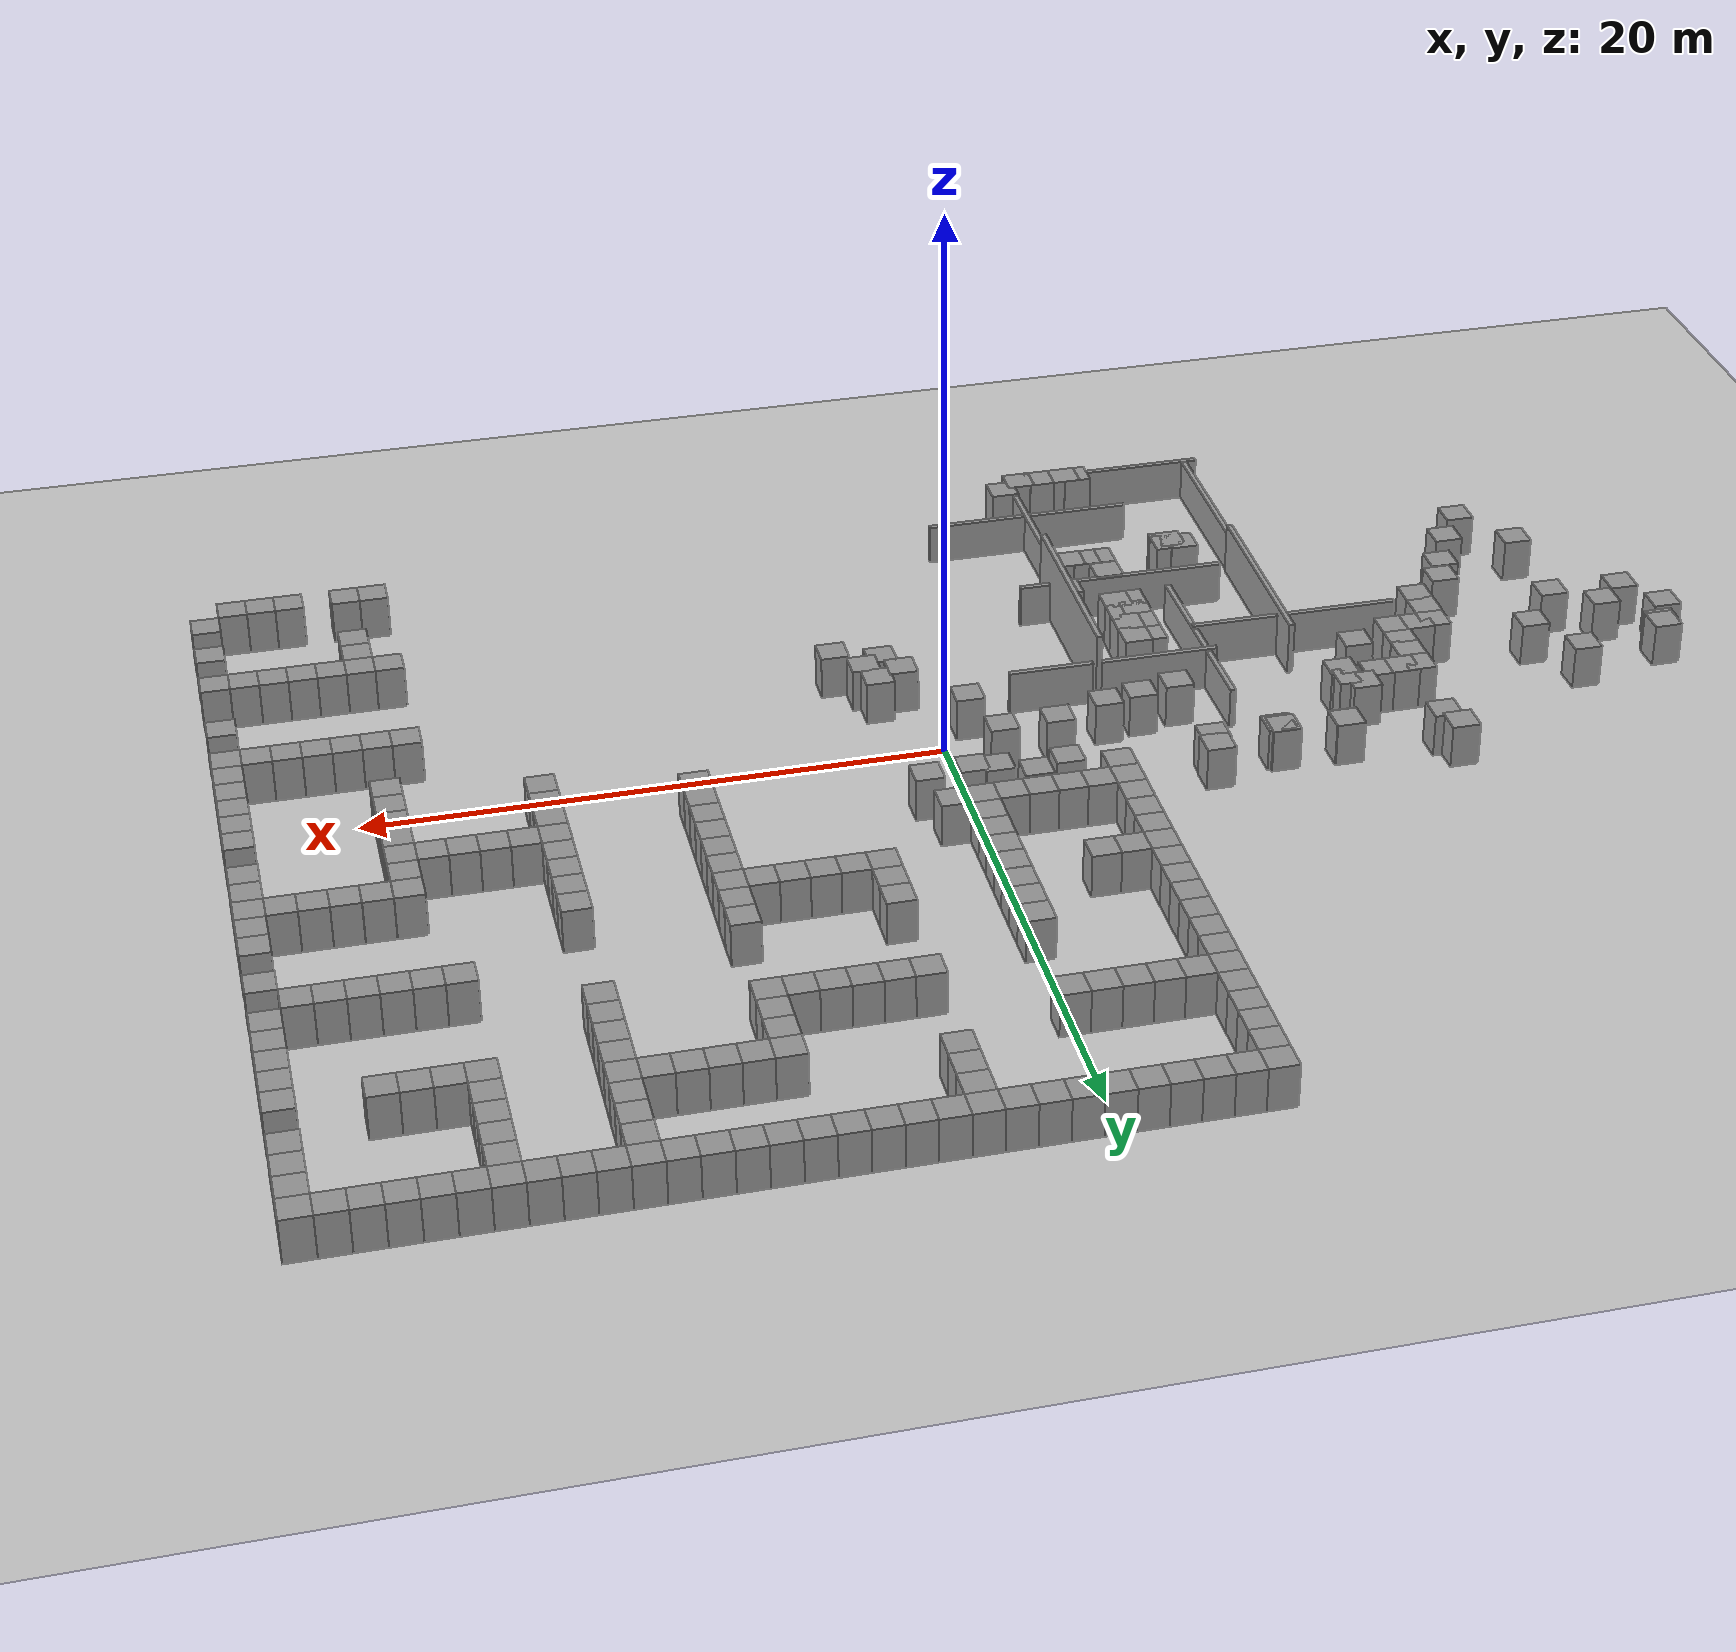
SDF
<sdf version="1.4">
 <world name="default">
  <light name="sun" type="directional">
   <pose>0 0 10 0 -0 0</pose>
   <diffuse>0.8 0.8 0.8 1</diffuse>
   <specular>0.2 0.2 0.2 1</specular>
   <attenuation>
    <range>1000</range>
    <constant>0.9</constant>
    <linear>0.01</linear>
    <quadratic>0.001</quadratic>
   </attenuation>
   <direction>-0.5 0.1 -0.9</direction>
  </light>
  <model name="ground_plane">
   <static>1</static>
   <link name="link">
    <collision name="collision">
     <geometry><plane><normal>0 0 1</normal><size>100 100</size></plane></geometry>
     <surface><friction><ode><mu>100</mu><mu2>50</mu2></ode></friction></surface>
    </collision>
    <visual name="visual">
     <cast_shadows>0</cast_shadows>
     <geometry><plane><normal>0 0 1</normal><size>100 100</size></plane></geometry>
     <material>
      <script><uri>file://media/materials/scripts/gazebo.material</uri><name>Gazebo/Grey</name></script>
     </material>
    </visual>
    <velocity_decay><linear>0</linear><angular>0</angular></velocity_decay>
   </link>
  </model>
  <physics type="ode">
   <max_step_size>0.001</max_step_size>
   <real_time_factor>1</real_time_factor>
   <real_time_update_rate>1000</real_time_update_rate>
   <gravity>0 0 -9.8</gravity>
  </physics>
  <scene><ambient>0.4 0.4 0.4 1</ambient><background>0.7 0.7 0.7 1</background><shadows>1</shadows></scene>
  <spherical_coordinates>
   <surface_model>EARTH_WGS84</surface_model>
   <latitude_deg>0</latitude_deg>
   <longitude_deg>0</longitude_deg>
   <elevation>0</elevation>
   <heading_deg>0</heading_deg>
  </spherical_coordinates>
  <model name="unit_box_1">
   <pose>-5.01661 4.99523 0.5 0 -0 0.000223</pose>
   <static>1</static>
   <link name="link">
    <inertial>
     <mass>1</mass>
     <inertia><ixx>1</ixx><ixy>0</ixy><ixz>0</ixz><iyy>1</iyy><iyz>0</iyz><izz>1</izz></inertia>
    </inertial>
    <collision name="collision"><geometry><box><size>1 1 2</size></box></geometry></collision>
    <visual name="visual">
     <geometry><box><size>1 1 2</size></box></geometry>
     <material>
      <script><uri>file://media/materials/scripts/gazebo.material</uri><name>Gazebo/Grey</name></script>
     </material>
    </visual>
    <velocity_decay><linear>0</linear><angular>0</angular></velocity_decay>
   </link>
   <static>0</static>
  </model>
  <model name="unit_box_2">
   <pose>-4.01641 4.99001 0.5 0 -0 3e-05</pose>
   <static>1</static>
   <link name="link">
    <inertial>
     <mass>1</mass>
     <inertia><ixx>1</ixx><ixy>0</ixy><ixz>0</ixz><iyy>1</iyy><iyz>0</iyz><izz>1</izz></inertia>
    </inertial>
    <collision name="collision"><geometry><box><size>1 1 2</size></box></geometry></collision>
    <visual name="visual">
     <geometry><box><size>1 1 2</size></box></geometry>
     <material>
      <script><uri>file://media/materials/scripts/gazebo.material</uri><name>Gazebo/Grey</name></script>
     </material>
    </visual>
    <velocity_decay><linear>0</linear><angular>0</angular></velocity_decay>
   </link>
   <static>0</static>
  </model>
  <model name="unit_box_3">
   <pose>-3.0164 4.98791 0.5 0 -0 2.1e-05</pose>
   <static>1</static>
   <link name="link">
    <inertial>
     <mass>1</mass>
     <inertia><ixx>1</ixx><ixy>0</ixy><ixz>0</ixz><iyy>1</iyy><iyz>0</iyz><izz>1</izz></inertia>
    </inertial>
    <collision name="collision"><geometry><box><size>1 1 2</size></box></geometry></collision>
    <visual name="visual">
     <geometry><box><size>1 1 2</size></box></geometry>
     <material>
      <script><uri>file://media/materials/scripts/gazebo.material</uri><name>Gazebo/Grey</name></script>
     </material>
    </visual>
    <velocity_decay><linear>0</linear><angular>0</angular></velocity_decay>
   </link>
   <static>0</static>
  </model>
  <model name="unit_box_4">
   <pose>-2.01625 4.98914 0.5 0 0 -0.000278</pose>
   <static>1</static>
   <link name="link">
    <inertial>
     <mass>1</mass>
     <inertia><ixx>1</ixx><ixy>0</ixy><ixz>0</ixz><iyy>1</iyy><iyz>0</iyz><izz>1</izz></inertia>
    </inertial>
    <collision name="collision"><geometry><box><size>1 1 2</size></box></geometry></collision>
    <visual name="visual">
     <geometry><box><size>1 1 2</size></box></geometry>
     <material>
      <script><uri>file://media/materials/scripts/gazebo.material</uri><name>Gazebo/Grey</name></script>
     </material>
    </visual>
    <velocity_decay><linear>0</linear><angular>0</angular></velocity_decay>
   </link>
   <static>0</static>
  </model>
  <model name="unit_box_5">
   <pose>-1.01623 4.98884 0.5 0 0 -0.000319</pose>
   <static>1</static>
   <link name="link">
    <inertial>
     <mass>1</mass>
     <inertia><ixx>1</ixx><ixy>0</ixy><ixz>0</ixz><iyy>1</iyy><iyz>0</iyz><izz>1</izz></inertia>
    </inertial>
    <collision name="collision"><geometry><box><size>1 1 2</size></box></geometry></collision>
    <visual name="visual">
     <geometry><box><size>1 1 2</size></box></geometry>
     <material>
      <script><uri>file://media/materials/scripts/gazebo.material</uri><name>Gazebo/Grey</name></script>
     </material>
    </visual>
    <velocity_decay><linear>0</linear><angular>0</angular></velocity_decay>
   </link>
   <static>0</static>
  </model>
  <model name="unit_box_6">
   <pose>-0.01622 4.99333 0.5 0 0 -0.000328</pose>
   <static>1</static>
   <link name="link">
    <inertial>
     <mass>1</mass>
     <inertia><ixx>1</ixx><ixy>0</ixy><ixz>0</ixz><iyy>1</iyy><iyz>0</iyz><izz>1</izz></inertia>
    </inertial>
    <collision name="collision"><geometry><box><size>1 1 2</size></box></geometry></collision>
    <visual name="visual">
     <geometry><box><size>1 1 2</size></box></geometry>
     <material>
      <script><uri>file://media/materials/scripts/gazebo.material</uri><name>Gazebo/Grey</name></script>
     </material>
    </visual>
    <velocity_decay><linear>0</linear><angular>0</angular></velocity_decay>
   </link>
   <static>0</static>
  </model>
  <model name="unit_box_7">
   <pose>0.984482 4.99573 0.5 0 0 -0.000753</pose>
   <static>1</static>
   <link name="link">
    <inertial>
     <mass>1</mass>
     <inertia><ixx>1</ixx><ixy>0</ixy><ixz>0</ixz><iyy>1</iyy><iyz>0</iyz><izz>1</izz></inertia>
    </inertial>
    <collision name="collision"><geometry><box><size>1 1 2</size></box></geometry></collision>
    <visual name="visual">
     <geometry><box><size>1 1 2</size></box></geometry>
     <material>
      <script><uri>file://media/materials/scripts/gazebo.material</uri><name>Gazebo/Grey</name></script>
     </material>
    </visual>
    <velocity_decay><linear>0</linear><angular>0</angular></velocity_decay>
   </link>
   <static>0</static>
  </model>
  <model name="unit_box_8">
   <pose>0.712903 -3.52038 0.5 0 0 -0.000671</pose>
   <static>1</static>
   <link name="link">
    <inertial>
     <mass>1</mass>
     <inertia><ixx>1</ixx><ixy>0</ixy><ixz>0</ixz><iyy>1</iyy><iyz>0</iyz><izz>1</izz></inertia>
    </inertial>
    <collision name="collision"><geometry><box><size>1 1 2</size></box></geometry></collision>
    <visual name="visual">
     <geometry><box><size>1 1 2</size></box></geometry>
     <material>
      <script><uri>file://media/materials/scripts/gazebo.material</uri><name>Gazebo/Grey</name></script>
     </material>
    </visual>
    <velocity_decay><linear>0</linear><angular>0</angular></velocity_decay>
   </link>
   <static>0</static>
  </model>
  <model name="unit_box_9">
   <pose>1.44258 3.31648 0.5 0 0 -0.000565</pose>
   <static>1</static>
   <link name="link">
    <inertial>
     <mass>1</mass>
     <inertia><ixx>1</ixx><ixy>0</ixy><ixz>0</ixz><iyy>1</iyy><iyz>0</iyz><izz>1</izz></inertia>
    </inertial>
    <collision name="collision"><geometry><box><size>1 1 2</size></box></geometry></collision>
    <visual name="visual">
     <geometry><box><size>1 1 2</size></box></geometry>
     <material>
      <script><uri>file://media/materials/scripts/gazebo.material</uri><name>Gazebo/Grey</name></script>
     </material>
    </visual>
    <velocity_decay><linear>0</linear><angular>0</angular></velocity_decay>
   </link>
   <static>0</static>
  </model>
  <model name="unit_box_10">
   <pose>-0.138709 3.17291 0.5 0 0 -0.000527</pose>
   <static>1</static>
   <link name="link">
    <inertial>
     <mass>1</mass>
     <inertia><ixx>1</ixx><ixy>0</ixy><ixz>0</ixz><iyy>1</iyy><iyz>0</iyz><izz>1</izz></inertia>
    </inertial>
    <collision name="collision"><geometry><box><size>1 1 2</size></box></geometry></collision>
    <visual name="visual">
     <geometry><box><size>1 1 2</size></box></geometry>
     <material>
      <script><uri>file://media/materials/scripts/gazebo.material</uri><name>Gazebo/Grey</name></script>
     </material>
    </visual>
    <velocity_decay><linear>0</linear><angular>0</angular></velocity_decay>
   </link>
   <static>0</static>
  </model>
  <model name="unit_box_11">
   <pose>-0.970669 3.30786 0.5 0 0 -0.000466</pose>
   <static>1</static>
   <link name="link">
    <inertial>
     <mass>1</mass>
     <inertia><ixx>1</ixx><ixy>0</ixy><ixz>0</ixz><iyy>1</iyy><iyz>0</iyz><izz>1</izz></inertia>
    </inertial>
    <collision name="collision"><geometry><box><size>1 1 2</size></box></geometry></collision>
    <visual name="visual">
     <geometry><box><size>1 1 2</size></box></geometry>
     <material>
      <script><uri>file://media/materials/scripts/gazebo.material</uri><name>Gazebo/Grey</name></script>
     </material>
    </visual>
    <velocity_decay><linear>0</linear><angular>0</angular></velocity_decay>
   </link>
   <static>0</static>
  </model>
  <model name="unit_box_12">
   <pose>-2.17996 3.88081 0.5 0 0 -0.000581</pose>
   <static>1</static>
   <link name="link">
    <inertial>
     <mass>1</mass>
     <inertia><ixx>1</ixx><ixy>0</ixy><ixz>0</ixz><iyy>1</iyy><iyz>0</iyz><izz>1</izz></inertia>
    </inertial>
    <collision name="collision"><geometry><box><size>1 1 2</size></box></geometry></collision>
    <visual name="visual">
     <geometry><box><size>1 1 2</size></box></geometry>
     <material>
      <script><uri>file://media/materials/scripts/gazebo.material</uri><name>Gazebo/Grey</name></script>
     </material>
    </visual>
    <velocity_decay><linear>0</linear><angular>0</angular></velocity_decay>
   </link>
   <static>0</static>
  </model>
  <model name="unit_box_13">
   <pose>-14.6079 1.19812 0.5 0 0 -0.000581</pose>
   <static>1</static>
   <link name="link">
    <inertial>
     <mass>1</mass>
     <inertia><ixx>1</ixx><ixy>0</ixy><ixz>0</ixz><iyy>1</iyy><iyz>0</iyz><izz>1</izz></inertia>
    </inertial>
    <collision name="collision"><geometry><box><size>1 1 2</size></box></geometry></collision>
    <visual name="visual">
     <geometry><box><size>1 1 2</size></box></geometry>
     <material>
      <script><uri>file://media/materials/scripts/gazebo.material</uri><name>Gazebo/Grey</name></script>
     </material>
    </visual>
    <velocity_decay><linear>0</linear><angular>0</angular></velocity_decay>
   </link>
   <static>0</static>
  </model>
  <model name="unit_box_14">
   <pose>-3.73384 0.836895 0.5 0 0 -0.000611</pose>
   <static>1</static>
   <link name="link">
    <inertial>
     <mass>1</mass>
     <inertia><ixx>1</ixx><ixy>0</ixy><ixz>0</ixz><iyy>1</iyy><iyz>0</iyz><izz>1</izz></inertia>
    </inertial>
    <collision name="collision"><geometry><box><size>1 1 2</size></box></geometry></collision>
    <visual name="visual">
     <geometry><box><size>1 1 2</size></box></geometry>
     <material>
      <script><uri>file://media/materials/scripts/gazebo.material</uri><name>Gazebo/Grey</name></script>
     </material>
    </visual>
    <velocity_decay><linear>0</linear><angular>0</angular></velocity_decay>
   </link>
   <static>0</static>
  </model>
  <model name="unit_box_15">
   <pose>-18.4176 -4.09266 0.5 0 0 -3.9e-05</pose>
   <static>1</static>
   <link name="link">
    <inertial>
     <mass>1</mass>
     <inertia><ixx>1</ixx><ixy>0</ixy><ixz>0</ixz><iyy>1</iyy><iyz>0</iyz><izz>1</izz></inertia>
    </inertial>
    <collision name="collision"><geometry><box><size>1 1 2</size></box></geometry></collision>
    <visual name="visual">
     <geometry><box><size>1 1 2</size></box></geometry>
     <material>
      <script><uri>file://media/materials/scripts/gazebo.material</uri><name>Gazebo/Grey</name></script>
     </material>
    </visual>
    <velocity_decay><linear>0</linear><angular>0</angular></velocity_decay>
   </link>
   <static>0</static>
  </model>
  <model name="unit_box_17">
   <pose>-11.3499 -9.74987 0.5 0 0 -1.9e-05</pose>
   <static>1</static>
   <link name="link">
    <inertial>
     <mass>1</mass>
     <inertia><ixx>1</ixx><ixy>0</ixy><ixz>0</ixz><iyy>1</iyy><iyz>0</iyz><izz>1</izz></inertia>
    </inertial>
    <collision name="collision"><geometry><box><size>1 1 2</size></box></geometry></collision>
    <visual name="visual">
     <geometry><box><size>1 1 2</size></box></geometry>
     <material>
      <script><uri>file://media/materials/scripts/gazebo.material</uri><name>Gazebo/Grey</name></script>
     </material>
    </visual>
    <velocity_decay><linear>0</linear><angular>0</angular></velocity_decay>
   </link>
   <static>0</static>
  </model>
  <model name="unit_box_18">
   <pose>-10.8857 3.14072 0.5 0 0 -1.5e-05</pose>
   <static>1</static>
   <link name="link">
    <inertial>
     <mass>1</mass>
     <inertia><ixx>1</ixx><ixy>0</ixy><ixz>0</ixz><iyy>1</iyy><iyz>0</iyz><izz>1</izz></inertia>
    </inertial>
    <collision name="collision"><geometry><box><size>1 1 2</size></box></geometry></collision>
    <visual name="visual">
     <geometry><box><size>1 1 2</size></box></geometry>
     <material>
      <script><uri>file://media/materials/scripts/gazebo.material</uri><name>Gazebo/Grey</name></script>
     </material>
    </visual>
    <velocity_decay><linear>0</linear><angular>0</angular></velocity_decay>
   </link>
   <static>0</static>
  </model>
  <model name="unit_box_19">
   <pose>-13.2215 3.36273 0.5 0 0 -1e-05</pose>
   <static>1</static>
   <link name="link">
    <inertial>
     <mass>1</mass>
     <inertia><ixx>1</ixx><ixy>0</ixy><ixz>0</ixz><iyy>1</iyy><iyz>0</iyz><izz>1</izz></inertia>
    </inertial>
    <collision name="collision"><geometry><box><size>1 1 2</size></box></geometry></collision>
    <visual name="visual">
     <geometry><box><size>1 1 2</size></box></geometry>
     <material>
      <script><uri>file://media/materials/scripts/gazebo.material</uri><name>Gazebo/Grey</name></script>
     </material>
    </visual>
    <velocity_decay><linear>0</linear><angular>0</angular></velocity_decay>
   </link>
   <static>0</static>
  </model>
  <model name="unit_box_20">
   <pose>-6.91683 -0.051818 0.5 0 0 -1e-05</pose>
   <static>1</static>
   <link name="link">
    <inertial>
     <mass>1</mass>
     <inertia><ixx>1</ixx><ixy>0</ixy><ixz>0</ixz><iyy>1</iyy><iyz>0</iyz><izz>1</izz></inertia>
    </inertial>
    <collision name="collision"><geometry><box><size>1 1 2</size></box></geometry></collision>
    <visual name="visual">
     <geometry><box><size>1 1 2</size></box></geometry>
     <material>
      <script><uri>file://media/materials/scripts/gazebo.material</uri><name>Gazebo/Grey</name></script>
     </material>
    </visual>
    <velocity_decay><linear>0</linear><angular>0</angular></velocity_decay>
   </link>
   <static>0</static>
  </model>
  <model name="unit_box_21">
   <pose>-1.09257 -1.23498 0.5 0 0 -1.2e-05</pose>
   <static>1</static>
   <link name="link">
    <inertial>
     <mass>1</mass>
     <inertia><ixx>1</ixx><ixy>0</ixy><ixz>0</ixz><iyy>1</iyy><iyz>0</iyz><izz>1</izz></inertia>
    </inertial>
    <collision name="collision"><geometry><box><size>1 1 2</size></box></geometry></collision>
    <visual name="visual">
     <geometry><box><size>1 1 2</size></box></geometry>
     <material>
      <script><uri>file://media/materials/scripts/gazebo.material</uri><name>Gazebo/Grey</name></script>
     </material>
    </visual>
    <velocity_decay><linear>0</linear><angular>0</angular></velocity_decay>
   </link>
   <static>0</static>
  </model>
  <model name="unit_box_22">
   <pose>-3.38353 3.38811 0.5 0 0 -1.2e-05</pose>
   <static>1</static>
   <link name="link">
    <inertial>
     <mass>1</mass>
     <inertia><ixx>1</ixx><ixy>0</ixy><ixz>0</ixz><iyy>1</iyy><iyz>0</iyz><izz>1</izz></inertia>
    </inertial>
    <collision name="collision"><geometry><box><size>1 1 2</size></box></geometry></collision>
    <visual name="visual">
     <geometry><box><size>1 1 2</size></box></geometry>
     <material>
      <script><uri>file://media/materials/scripts/gazebo.material</uri><name>Gazebo/Grey</name></script>
     </material>
    </visual>
    <velocity_decay><linear>0</linear><angular>0</angular></velocity_decay>
   </link>
   <static>0</static>
  </model>
  <model name="unit_box_24">
   <pose>1.94664 -3.96372 0.5 0 0 -1.4e-05</pose>
   <static>1</static>
   <link name="link">
    <inertial>
     <mass>1</mass>
     <inertia><ixx>1</ixx><ixy>0</ixy><ixz>0</ixz><iyy>1</iyy><iyz>0</iyz><izz>1</izz></inertia>
    </inertial>
    <collision name="collision"><geometry><box><size>1 1 2</size></box></geometry></collision>
    <visual name="visual">
     <geometry><box><size>1 1 2</size></box></geometry>
     <material>
      <script><uri>file://media/materials/scripts/gazebo.material</uri><name>Gazebo/Grey</name></script>
     </material>
    </visual>
    <velocity_decay><linear>0</linear><angular>0</angular></velocity_decay>
   </link>
   <static>0</static>
  </model>
  <model name="unit_box_25">
   <pose>-6.35101 -7.46076 0.5 0 0 -1.5e-05</pose>
   <static>1</static>
   <link name="link">
    <inertial>
     <mass>1</mass>
     <inertia><ixx>1</ixx><ixy>0</ixy><ixz>0</ixz><iyy>1</iyy><iyz>0</iyz><izz>1</izz></inertia>
    </inertial>
    <collision name="collision"><geometry><box><size>1 1 2</size></box></geometry></collision>
    <visual name="visual">
     <geometry><box><size>1 1 2</size></box></geometry>
     <material>
      <script><uri>file://media/materials/scripts/gazebo.material</uri><name>Gazebo/Grey</name></script>
     </material>
    </visual>
    <velocity_decay><linear>0</linear><angular>0</angular></velocity_decay>
   </link>
   <static>0</static>
  </model>
  <model name="unit_box_26">
   <pose>2.82516 -5.06373 0.5 0 0 -1.1e-05</pose>
   <static>1</static>
   <link name="link">
    <inertial>
     <mass>1</mass>
     <inertia><ixx>1</ixx><ixy>0</ixy><ixz>0</ixz><iyy>1</iyy><iyz>0</iyz><izz>1</izz></inertia>
    </inertial>
    <collision name="collision"><geometry><box><size>1 1 2</size></box></geometry></collision>
    <visual name="visual">
     <geometry><box><size>1 1 2</size></box></geometry>
     <material>
      <script><uri>file://media/materials/scripts/gazebo.material</uri><name>Gazebo/Grey</name></script>
     </material>
    </visual>
    <velocity_decay><linear>0</linear><angular>0</angular></velocity_decay>
   </link>
   <static>0</static>
  </model>
  <model name="unit_box_27">
   <pose>-8.35413 -5.39726 0.5 0 0 -1e-05</pose>
   <static>1</static>
   <link name="link">
    <inertial>
     <mass>1</mass>
     <inertia><ixx>1</ixx><ixy>0</ixy><ixz>0</ixz><iyy>1</iyy><iyz>0</iyz><izz>1</izz></inertia>
    </inertial>
    <collision name="collision"><geometry><box><size>1 1 2</size></box></geometry></collision>
    <visual name="visual">
     <geometry><box><size>1 1 2</size></box></geometry>
     <material>
      <script><uri>file://media/materials/scripts/gazebo.material</uri><name>Gazebo/Grey</name></script>
     </material>
    </visual>
    <velocity_decay><linear>0</linear><angular>0</angular></velocity_decay>
   </link>
   <static>0</static>
  </model>
  <model name="unit_box_28">
   <pose>1.24112 -4.4264 0.5 0 0 -1.1e-05</pose>
   <static>1</static>
   <link name="link">
    <inertial>
     <mass>1</mass>
     <inertia><ixx>1</ixx><ixy>0</ixy><ixz>0</ixz><iyy>1</iyy><iyz>0</iyz><izz>1</izz></inertia>
    </inertial>
    <collision name="collision"><geometry><box><size>1 1 2</size></box></geometry></collision>
    <visual name="visual">
     <geometry><box><size>1 1 2</size></box></geometry>
     <material>
      <script><uri>file://media/materials/scripts/gazebo.material</uri><name>Gazebo/Grey</name></script>
     </material>
    </visual>
    <velocity_decay><linear>0</linear><angular>0</angular></velocity_decay>
   </link>
   <static>0</static>
  </model>
  <model name="unit_box_30">
   <pose>8.99995 1.99999 0.5 0 0 -7e-06</pose>
   <static>1</static>
   <link name="link">
    <inertial>
     <mass>1</mass>
     <inertia><ixx>1</ixx><ixy>0</ixy><ixz>0</ixz><iyy>1</iyy><iyz>0</iyz><izz>1</izz></inertia>
    </inertial>
    <collision name="collision"><geometry><box><size>1 1 2</size></box></geometry></collision>
    <visual name="visual">
     <geometry><box><size>1 1 2</size></box></geometry>
     <material>
      <script><uri>file://media/materials/scripts/gazebo.material</uri><name>Gazebo/Grey</name></script>
     </material>
    </visual>
    <velocity_decay><linear>0</linear><angular>0</angular></velocity_decay>
   </link>
   <static>0</static>
  </model>
  <model name="unit_box_31">
   <pose>8.99997 3 0.5 0 0 -6e-06</pose>
   <static>1</static>
   <link name="link">
    <inertial>
     <mass>1</mass>
     <inertia><ixx>1</ixx><ixy>0</ixy><ixz>0</ixz><iyy>1</iyy><iyz>0</iyz><izz>1</izz></inertia>
    </inertial>
    <collision name="collision"><geometry><box><size>1 1 2</size></box></geometry></collision>
    <visual name="visual">
     <geometry><box><size>1 1 2</size></box></geometry>
     <material>
      <script><uri>file://media/materials/scripts/gazebo.material</uri><name>Gazebo/Grey</name></script>
     </material>
    </visual>
    <velocity_decay><linear>0</linear><angular>0</angular></velocity_decay>
   </link>
   <static>0</static>
  </model>
  <model name="unit_box_32">
   <pose>8.99997 4 0.5 0 0 -8e-06</pose>
   <static>1</static>
   <link name="link">
    <inertial>
     <mass>1</mass>
     <inertia><ixx>1</ixx><ixy>0</ixy><ixz>0</ixz><iyy>1</iyy><iyz>0</iyz><izz>1</izz></inertia>
    </inertial>
    <collision name="collision"><geometry><box><size>1 1 2</size></box></geometry></collision>
    <visual name="visual">
     <geometry><box><size>1 1 2</size></box></geometry>
     <material>
      <script><uri>file://media/materials/scripts/gazebo.material</uri><name>Gazebo/Grey</name></script>
     </material>
    </visual>
    <velocity_decay><linear>0</linear><angular>0</angular></velocity_decay>
   </link>
   <static>0</static>
  </model>
  <model name="unit_box_33">
   <pose>9 5 0.5 0 0 -7e-06</pose>
   <static>1</static>
   <link name="link">
    <inertial>
     <mass>1</mass>
     <inertia><ixx>1</ixx><ixy>0</ixy><ixz>0</ixz><iyy>1</iyy><iyz>0</iyz><izz>1</izz></inertia>
    </inertial>
    <collision name="collision"><geometry><box><size>1 1 2</size></box></geometry></collision>
    <visual name="visual">
     <geometry><box><size>1 1 2</size></box></geometry>
     <material>
      <script><uri>file://media/materials/scripts/gazebo.material</uri><name>Gazebo/Grey</name></script>
     </material>
    </visual>
    <velocity_decay><linear>0</linear><angular>0</angular></velocity_decay>
   </link>
   <static>0</static>
  </model>
  <model name="unit_box_34">
   <pose>9 6 0.5 0 0 -6e-06</pose>
   <static>1</static>
   <link name="link">
    <inertial>
     <mass>1</mass>
     <inertia><ixx>1</ixx><ixy>0</ixy><ixz>0</ixz><iyy>1</iyy><iyz>0</iyz><izz>1</izz></inertia>
    </inertial>
    <collision name="collision"><geometry><box><size>1 1 2</size></box></geometry></collision>
    <visual name="visual">
     <geometry><box><size>1 1 2</size></box></geometry>
     <material>
      <script><uri>file://media/materials/scripts/gazebo.material</uri><name>Gazebo/Grey</name></script>
     </material>
    </visual>
    <velocity_decay><linear>0</linear><angular>0</angular></velocity_decay>
   </link>
   <static>0</static>
  </model>
  <model name="unit_box_35">
   <pose>-7.82124 -6.15776 0.5 0 0 -1.5e-05</pose>
   <static>1</static>
   <link name="link">
    <inertial>
     <mass>1</mass>
     <inertia><ixx>1</ixx><ixy>0</ixy><ixz>0</ixz><iyy>1</iyy><iyz>0</iyz><izz>1</izz></inertia>
    </inertial>
    <collision name="collision"><geometry><box><size>1 1 2</size></box></geometry></collision>
    <visual name="visual">
     <geometry><box><size>1 1 2</size></box></geometry>
     <material>
      <script><uri>file://media/materials/scripts/gazebo.material</uri><name>Gazebo/Grey</name></script>
     </material>
    </visual>
    <velocity_decay><linear>0</linear><angular>0</angular></velocity_decay>
   </link>
   <static>0</static>
  </model>
  <model name="unit_box_36">
   <pose>-8.35812 -6.16943 0.5 0 0 -1.5e-05</pose>
   <static>1</static>
   <link name="link">
    <inertial>
     <mass>1</mass>
     <inertia><ixx>1</ixx><ixy>0</ixy><ixz>0</ixz><iyy>1</iyy><iyz>0</iyz><izz>1</izz></inertia>
    </inertial>
    <collision name="collision"><geometry><box><size>1 1 2</size></box></geometry></collision>
    <visual name="visual">
     <geometry><box><size>1 1 2</size></box></geometry>
     <material>
      <script><uri>file://media/materials/scripts/gazebo.material</uri><name>Gazebo/Grey</name></script>
     </material>
    </visual>
    <velocity_decay><linear>0</linear><angular>0</angular></velocity_decay>
   </link>
   <static>0</static>
  </model>
  <model name="unit_box_37">
   <pose>-7.80224 -4.57019 0.5 0 0 -1.4e-05</pose>
   <static>1</static>
   <link name="link">
    <inertial>
     <mass>1</mass>
     <inertia><ixx>1</ixx><ixy>0</ixy><ixz>0</ixz><iyy>1</iyy><iyz>0</iyz><izz>1</izz></inertia>
    </inertial>
    <collision name="collision"><geometry><box><size>1 1 2</size></box></geometry></collision>
    <visual name="visual">
     <geometry><box><size>1 1 2</size></box></geometry>
     <material>
      <script><uri>file://media/materials/scripts/gazebo.material</uri><name>Gazebo/Grey</name></script>
     </material>
    </visual>
    <velocity_decay><linear>0</linear><angular>0</angular></velocity_decay>
   </link>
   <static>0</static>
  </model>
  <model name="unit_box_38">
   <pose>9.00001 7 0.5 0 0 -3e-06</pose>
   <static>1</static>
   <link name="link">
    <inertial>
     <mass>1</mass>
     <inertia><ixx>1</ixx><ixy>0</ixy><ixz>0</ixz><iyy>1</iyy><iyz>0</iyz><izz>1</izz></inertia>
    </inertial>
    <collision name="collision"><geometry><box><size>1 1 2</size></box></geometry></collision>
    <visual name="visual">
     <geometry><box><size>1 1 2</size></box></geometry>
     <material>
      <script><uri>file://media/materials/scripts/gazebo.material</uri><name>Gazebo/Grey</name></script>
     </material>
    </visual>
    <velocity_decay><linear>0</linear><angular>0</angular></velocity_decay>
   </link>
   <static>0</static>
  </model>
  <model name="unit_box_39">
   <pose>9 8.00001 0.5 0 0 -1e-06</pose>
   <static>1</static>
   <link name="link">
    <inertial>
     <mass>1</mass>
     <inertia><ixx>1</ixx><ixy>0</ixy><ixz>0</ixz><iyy>1</iyy><iyz>0</iyz><izz>1</izz></inertia>
    </inertial>
    <collision name="collision"><geometry><box><size>1 1 2</size></box></geometry></collision>
    <visual name="visual">
     <geometry><box><size>1 1 2</size></box></geometry>
     <material>
      <script><uri>file://media/materials/scripts/gazebo.material</uri><name>Gazebo/Grey</name></script>
     </material>
    </visual>
    <velocity_decay><linear>0</linear><angular>0</angular></velocity_decay>
   </link>
   <static>0</static>
  </model>
  <model name="unit_box_40">
   <pose>-5.01481 3.99235 0.5 0 -0 0.003225</pose>
   <static>1</static>
   <link name="link">
    <inertial>
     <mass>1</mass>
     <inertia><ixx>1</ixx><ixy>0</ixy><ixz>0</ixz><iyy>1</iyy><iyz>0</iyz><izz>1</izz></inertia>
    </inertial>
    <collision name="collision"><geometry><box><size>1 1 2</size></box></geometry></collision>
    <visual name="visual">
     <geometry><box><size>1 1 2</size></box></geometry>
     <material>
      <script><uri>file://media/materials/scripts/gazebo.material</uri><name>Gazebo/Grey</name></script>
     </material>
    </visual>
    <velocity_decay><linear>0</linear><angular>0</angular></velocity_decay>
   </link>
   <static>0</static>
  </model>
  <model name="unit_box_42">
   <pose>-18.4169 -3.16567 0.5 0 -0 0.001796</pose>
   <static>1</static>
   <link name="link">
    <inertial>
     <mass>1</mass>
     <inertia><ixx>1</ixx><ixy>0</ixy><ixz>0</ixz><iyy>1</iyy><iyz>0</iyz><izz>1</izz></inertia>
    </inertial>
    <collision name="collision"><geometry><box><size>1 1 2</size></box></geometry></collision>
    <visual name="visual">
     <geometry><box><size>1 1 2</size></box></geometry>
     <material>
      <script><uri>file://media/materials/scripts/gazebo.material</uri><name>Gazebo/Grey</name></script>
     </material>
    </visual>
    <velocity_decay><linear>0</linear><angular>0</angular></velocity_decay>
   </link>
   <static>0</static>
  </model>
  <model name="unit_box_43">
   <pose>-18.3967 -2.18667 0.5 0 -0 0.001375</pose>
   <static>1</static>
   <link name="link">
    <inertial>
     <mass>1</mass>
     <inertia><ixx>1</ixx><ixy>0</ixy><ixz>0</ixz><iyy>1</iyy><iyz>0</iyz><izz>1</izz></inertia>
    </inertial>
    <collision name="collision"><geometry><box><size>1 1 2</size></box></geometry></collision>
    <visual name="visual">
     <geometry><box><size>1 1 2</size></box></geometry>
     <material>
      <script><uri>file://media/materials/scripts/gazebo.material</uri><name>Gazebo/Grey</name></script>
     </material>
    </visual>
    <velocity_decay><linear>0</linear><angular>0</angular></velocity_decay>
   </link>
   <static>0</static>
  </model>
  <model name="unit_box_44">
   <pose>-17.7736 -2.1615 0.5 0 -0 0.000932</pose>
   <static>1</static>
   <link name="link">
    <inertial>
     <mass>1</mass>
     <inertia><ixx>1</ixx><ixy>0</ixy><ixz>0</ixz><iyy>1</iyy><iyz>0</iyz><izz>1</izz></inertia>
    </inertial>
    <collision name="collision"><geometry><box><size>1 1 2</size></box></geometry></collision>
    <visual name="visual">
     <geometry><box><size>1 1 2</size></box></geometry>
     <material>
      <script><uri>file://media/materials/scripts/gazebo.material</uri><name>Gazebo/Grey</name></script>
     </material>
    </visual>
    <velocity_decay><linear>0</linear><angular>0</angular></velocity_decay>
   </link>
   <static>0</static>
  </model>
  <model name="unit_box_45">
   <pose>-16.8401 -2.16548 0.5 0 -0 0.000893</pose>
   <static>1</static>
   <link name="link">
    <inertial>
     <mass>1</mass>
     <inertia><ixx>1</ixx><ixy>0</ixy><ixz>0</ixz><iyy>1</iyy><iyz>0</iyz><izz>1</izz></inertia>
    </inertial>
    <collision name="collision"><geometry><box><size>1 1 2</size></box></geometry></collision>
    <visual name="visual">
     <geometry><box><size>1 1 2</size></box></geometry>
     <material>
      <script><uri>file://media/materials/scripts/gazebo.material</uri><name>Gazebo/Grey</name></script>
     </material>
    </visual>
    <velocity_decay><linear>0</linear><angular>0</angular></velocity_decay>
   </link>
   <static>0</static>
  </model>
  <model name="unit_box_46">
   <pose>-16.8434 -1.38674 0.5 0 -0 0.000802</pose>
   <static>1</static>
   <link name="link">
    <inertial>
     <mass>1</mass>
     <inertia><ixx>1</ixx><ixy>0</ixy><ixz>0</ixz><iyy>1</iyy><iyz>0</iyz><izz>1</izz></inertia>
    </inertial>
    <collision name="collision"><geometry><box><size>1 1 2</size></box></geometry></collision>
    <visual name="visual">
     <geometry><box><size>1 1 2</size></box></geometry>
     <material>
      <script><uri>file://media/materials/scripts/gazebo.material</uri><name>Gazebo/Grey</name></script>
     </material>
    </visual>
    <velocity_decay><linear>0</linear><angular>0</angular></velocity_decay>
   </link>
   <static>0</static>
  </model>
  <model name="unit_box_47">
   <pose>-15.3131 0.534187 0.5 0 -0 0.000729</pose>
   <static>1</static>
   <link name="link">
    <inertial>
     <mass>1</mass>
     <inertia><ixx>1</ixx><ixy>0</ixy><ixz>0</ixz><iyy>1</iyy><iyz>0</iyz><izz>1</izz></inertia>
    </inertial>
    <collision name="collision"><geometry><box><size>1 1 2</size></box></geometry></collision>
    <visual name="visual">
     <geometry><box><size>1 1 2</size></box></geometry>
     <material>
      <script><uri>file://media/materials/scripts/gazebo.material</uri><name>Gazebo/Grey</name></script>
     </material>
    </visual>
    <velocity_decay><linear>0</linear><angular>0</angular></velocity_decay>
   </link>
   <static>0</static>
  </model>
  <model name="unit_box_48">
   <pose>-16.2487 0.525396 0.5 0 0 -0.000119</pose>
   <static>1</static>
   <link name="link">
    <inertial>
     <mass>1</mass>
     <inertia><ixx>1</ixx><ixy>0</ixy><ixz>0</ixz><iyy>1</iyy><iyz>0</iyz><izz>1</izz></inertia>
    </inertial>
    <collision name="collision"><geometry><box><size>1 1 2</size></box></geometry></collision>
    <visual name="visual">
     <geometry><box><size>1 1 2</size></box></geometry>
     <material>
      <script><uri>file://media/materials/scripts/gazebo.material</uri><name>Gazebo/Grey</name></script>
     </material>
    </visual>
    <velocity_decay><linear>0</linear><angular>0</angular></velocity_decay>
   </link>
   <static>0</static>
  </model>
  <model name="unit_box_49">
   <pose>-16.8494 -0.460464 0.5 0 0 -7.3e-05</pose>
   <static>1</static>
   <link name="link">
    <inertial>
     <mass>1</mass>
     <inertia><ixx>1</ixx><ixy>0</ixy><ixz>0</ixz><iyy>1</iyy><iyz>0</iyz><izz>1</izz></inertia>
    </inertial>
    <collision name="collision"><geometry><box><size>1 1 2</size></box></geometry></collision>
    <visual name="visual">
     <geometry><box><size>1 1 2</size></box></geometry>
     <material>
      <script><uri>file://media/materials/scripts/gazebo.material</uri><name>Gazebo/Grey</name></script>
     </material>
    </visual>
    <velocity_decay><linear>0</linear><angular>0</angular></velocity_decay>
   </link>
   <static>0</static>
  </model>
  <model name="unit_box_50">
   <pose>-16.8613 0.50095 0.5 0 0 -7.1e-05</pose>
   <static>1</static>
   <link name="link">
    <inertial>
     <mass>1</mass>
     <inertia><ixx>1</ixx><ixy>0</ixy><ixz>0</ixz><iyy>1</iyy><iyz>0</iyz><izz>1</izz></inertia>
    </inertial>
    <collision name="collision"><geometry><box><size>1 1 2</size></box></geometry></collision>
    <visual name="visual">
     <geometry><box><size>1 1 2</size></box></geometry>
     <material>
      <script><uri>file://media/materials/scripts/gazebo.material</uri><name>Gazebo/Grey</name></script>
     </material>
    </visual>
    <velocity_decay><linear>0</linear><angular>0</angular></velocity_decay>
   </link>
   <static>0</static>
  </model>
  <model name="unit_box_51">
   <pose>8 7.99999 0.5 0 -0 2e-06</pose>
   <static>1</static>
   <link name="link">
    <inertial>
     <mass>1</mass>
     <inertia><ixx>1</ixx><ixy>0</ixy><ixz>0</ixz><iyy>1</iyy><iyz>0</iyz><izz>1</izz></inertia>
    </inertial>
    <collision name="collision"><geometry><box><size>1 1 2</size></box></geometry></collision>
    <visual name="visual">
     <geometry><box><size>1 1 2</size></box></geometry>
     <material>
      <script><uri>file://media/materials/scripts/gazebo.material</uri><name>Gazebo/Grey</name></script>
     </material>
    </visual>
    <velocity_decay><linear>0</linear><angular>0</angular></velocity_decay>
   </link>
   <static>0</static>
  </model>
  <model name="unit_box_52">
   <pose>7 8.00001 0.5 0 -0 1e-06</pose>
   <static>1</static>
   <link name="link">
    <inertial>
     <mass>1</mass>
     <inertia><ixx>1</ixx><ixy>0</ixy><ixz>0</ixz><iyy>1</iyy><iyz>0</iyz><izz>1</izz></inertia>
    </inertial>
    <collision name="collision"><geometry><box><size>1 1 2</size></box></geometry></collision>
    <visual name="visual">
     <geometry><box><size>1 1 2</size></box></geometry>
     <material>
      <script><uri>file://media/materials/scripts/gazebo.material</uri><name>Gazebo/Grey</name></script>
     </material>
    </visual>
    <velocity_decay><linear>0</linear><angular>0</angular></velocity_decay>
   </link>
   <static>0</static>
  </model>
  <model name="unit_box_53">
   <pose>6 8 0.5 0 0 -3e-06</pose>
   <static>1</static>
   <link name="link">
    <inertial>
     <mass>1</mass>
     <inertia><ixx>1</ixx><ixy>0</ixy><ixz>0</ixz><iyy>1</iyy><iyz>0</iyz><izz>1</izz></inertia>
    </inertial>
    <collision name="collision"><geometry><box><size>1 1 2</size></box></geometry></collision>
    <visual name="visual">
     <geometry><box><size>1 1 2</size></box></geometry>
     <material>
      <script><uri>file://media/materials/scripts/gazebo.material</uri><name>Gazebo/Grey</name></script>
     </material>
    </visual>
    <velocity_decay><linear>0</linear><angular>0</angular></velocity_decay>
   </link>
   <static>0</static>
  </model>
  <model name="unit_box_54">
   <pose>5 8 0.5 0 0 -1e-06</pose>
   <static>1</static>
   <link name="link">
    <inertial>
     <mass>1</mass>
     <inertia><ixx>1</ixx><ixy>0</ixy><ixz>0</ixz><iyy>1</iyy><iyz>0</iyz><izz>1</izz></inertia>
    </inertial>
    <collision name="collision"><geometry><box><size>1 1 2</size></box></geometry></collision>
    <visual name="visual">
     <geometry><box><size>1 1 2</size></box></geometry>
     <material>
      <script><uri>file://media/materials/scripts/gazebo.material</uri><name>Gazebo/Grey</name></script>
     </material>
    </visual>
    <velocity_decay><linear>0</linear><angular>0</angular></velocity_decay>
   </link>
   <static>0</static>
  </model>
  <model name="unit_box_55">
   <pose>9 9.00001 0.5 0 0 -1e-06</pose>
   <static>1</static>
   <link name="link">
    <inertial>
     <mass>1</mass>
     <inertia><ixx>1</ixx><ixy>0</ixy><ixz>0</ixz><iyy>1</iyy><iyz>0</iyz><izz>1</izz></inertia>
    </inertial>
    <collision name="collision"><geometry><box><size>1 1 2</size></box></geometry></collision>
    <visual name="visual">
     <geometry><box><size>1 1 2</size></box></geometry>
     <material>
      <script><uri>file://media/materials/scripts/gazebo.material</uri><name>Gazebo/Grey</name></script>
     </material>
    </visual>
    <velocity_decay><linear>0</linear><angular>0</angular></velocity_decay>
   </link>
   <static>0</static>
  </model>
  <model name="unit_box_56">
   <pose>9 10 0.5 0 0 -2e-06</pose>
   <static>1</static>
   <link name="link">
    <inertial>
     <mass>1</mass>
     <inertia><ixx>1</ixx><ixy>0</ixy><ixz>0</ixz><iyy>1</iyy><iyz>0</iyz><izz>1</izz></inertia>
    </inertial>
    <collision name="collision"><geometry><box><size>1 1 2</size></box></geometry></collision>
    <visual name="visual">
     <geometry><box><size>1 1 2</size></box></geometry>
     <material>
      <script><uri>file://media/materials/scripts/gazebo.material</uri><name>Gazebo/Grey</name></script>
     </material>
    </visual>
    <velocity_decay><linear>0</linear><angular>0</angular></velocity_decay>
   </link>
   <static>0</static>
  </model>
  <model name="unit_box_57">
   <pose>-0.014979 5.99334 0.5 0 0 -0.00033</pose>
   <static>1</static>
   <link name="link">
    <inertial>
     <mass>1</mass>
     <inertia><ixx>1</ixx><ixy>0</ixy><ixz>0</ixz><iyy>1</iyy><iyz>0</iyz><izz>1</izz></inertia>
    </inertial>
    <collision name="collision"><geometry><box><size>1 1 2</size></box></geometry></collision>
    <visual name="visual">
     <geometry><box><size>1 1 2</size></box></geometry>
     <material>
      <script><uri>file://media/materials/scripts/gazebo.material</uri><name>Gazebo/Grey</name></script>
     </material>
    </visual>
    <velocity_decay><linear>0</linear><angular>0</angular></velocity_decay>
   </link>
   <static>0</static>
  </model>
  <model name="unit_box_58">
   <pose>-0.010958 6.99335 0.5 0 0 -0.00031</pose>
   <static>1</static>
   <link name="link">
    <inertial>
     <mass>1</mass>
     <inertia><ixx>1</ixx><ixy>0</ixy><ixz>0</ixz><iyy>1</iyy><iyz>0</iyz><izz>1</izz></inertia>
    </inertial>
    <collision name="collision"><geometry><box><size>1 1 2</size></box></geometry></collision>
    <visual name="visual">
     <geometry><box><size>1 1 2</size></box></geometry>
     <material>
      <script><uri>file://media/materials/scripts/gazebo.material</uri><name>Gazebo/Grey</name></script>
     </material>
    </visual>
    <velocity_decay><linear>0</linear><angular>0</angular></velocity_decay>
   </link>
   <static>0</static>
  </model>
  <model name="unit_box_59">
   <pose>-0.007655 7.99337 0.5 0 0 -0.000262</pose>
   <static>1</static>
   <link name="link">
    <inertial>
     <mass>1</mass>
     <inertia><ixx>1</ixx><ixy>0</ixy><ixz>0</ixz><iyy>1</iyy><iyz>0</iyz><izz>1</izz></inertia>
    </inertial>
    <collision name="collision"><geometry><box><size>1 1 2</size></box></geometry></collision>
    <visual name="visual">
     <geometry><box><size>1 1 2</size></box></geometry>
     <material>
      <script><uri>file://media/materials/scripts/gazebo.material</uri><name>Gazebo/Grey</name></script>
     </material>
    </visual>
    <velocity_decay><linear>0</linear><angular>0</angular></velocity_decay>
   </link>
   <static>0</static>
  </model>
  <model name="unit_box_60">
   <pose>-0.004062 8.99709 0.5 0 0 -8.2e-05</pose>
   <static>1</static>
   <link name="link">
    <inertial>
     <mass>1</mass>
     <inertia><ixx>1</ixx><ixy>0</ixy><ixz>0</ixz><iyy>1</iyy><iyz>0</iyz><izz>1</izz></inertia>
    </inertial>
    <collision name="collision"><geometry><box><size>1 1 2</size></box></geometry></collision>
    <visual name="visual">
     <geometry><box><size>1 1 2</size></box></geometry>
     <material>
      <script><uri>file://media/materials/scripts/gazebo.material</uri><name>Gazebo/Grey</name></script>
     </material>
    </visual>
    <velocity_decay><linear>0</linear><angular>0</angular></velocity_decay>
   </link>
   <static>0</static>
  </model>
  <model name="unit_box_61">
   <pose>-5.0071 5.99581 0.5 0 0 -0.000452</pose>
   <static>1</static>
   <link name="link">
    <inertial>
     <mass>1</mass>
     <inertia><ixx>1</ixx><ixy>0</ixy><ixz>0</ixz><iyy>1</iyy><iyz>0</iyz><izz>1</izz></inertia>
    </inertial>
    <collision name="collision"><geometry><box><size>1 1 2</size></box></geometry></collision>
    <visual name="visual">
     <geometry><box><size>1 1 2</size></box></geometry>
     <material>
      <script><uri>file://media/materials/scripts/gazebo.material</uri><name>Gazebo/Grey</name></script>
     </material>
    </visual>
    <velocity_decay><linear>0</linear><angular>0</angular></velocity_decay>
   </link>
   <static>0</static>
  </model>
  <model name="unit_box_62">
   <pose>0 10 0.5 0 -0 0</pose>
   <static>1</static>
   <link name="link">
    <inertial>
     <mass>1</mass>
     <inertia><ixx>1</ixx><ixy>0</ixy><ixz>0</ixz><iyy>1</iyy><iyz>0</iyz><izz>1</izz></inertia>
    </inertial>
    <collision name="collision"><geometry><box><size>1 1 2</size></box></geometry></collision>
    <visual name="visual">
     <geometry><box><size>1 1 2</size></box></geometry>
     <material>
      <script><uri>file://media/materials/scripts/gazebo.material</uri><name>Gazebo/Grey</name></script>
     </material>
    </visual>
    <velocity_decay><linear>0</linear><angular>0</angular></velocity_decay>
   </link>
   <static>0</static>
  </model>
  <model name="unit_box_63">
   <pose>0 11 0.5 0 -0 0</pose>
   <static>1</static>
   <link name="link">
    <inertial>
     <mass>1</mass>
     <inertia><ixx>1</ixx><ixy>0</ixy><ixz>0</ixz><iyy>1</iyy><iyz>0</iyz><izz>1</izz></inertia>
    </inertial>
    <collision name="collision"><geometry><box><size>1 1 2</size></box></geometry></collision>
    <visual name="visual">
     <geometry><box><size>1 1 2</size></box></geometry>
     <material>
      <script><uri>file://media/materials/scripts/gazebo.material</uri><name>Gazebo/Grey</name></script>
     </material>
    </visual>
    <velocity_decay><linear>0</linear><angular>0</angular></velocity_decay>
   </link>
   <static>0</static>
  </model>
  <model name="unit_box_64">
   <pose>0 12 0.5 0 -0 0</pose>
   <static>1</static>
   <link name="link">
    <inertial>
     <mass>1</mass>
     <inertia><ixx>1</ixx><ixy>0</ixy><ixz>0</ixz><iyy>1</iyy><iyz>0</iyz><izz>1</izz></inertia>
    </inertial>
    <collision name="collision"><geometry><box><size>1 1 2</size></box></geometry></collision>
    <visual name="visual">
     <geometry><box><size>1 1 2</size></box></geometry>
     <material>
      <script><uri>file://media/materials/scripts/gazebo.material</uri><name>Gazebo/Grey</name></script>
     </material>
    </visual>
    <velocity_decay><linear>0</linear><angular>0</angular></velocity_decay>
   </link>
   <static>0</static>
  </model>
  <model name="unit_box_65">
   <pose>4 14 0.5 0 -0 0</pose>
   <static>1</static>
   <link name="link">
    <inertial>
     <mass>1</mass>
     <inertia><ixx>1</ixx><ixy>0</ixy><ixz>0</ixz><iyy>1</iyy><iyz>0</iyz><izz>1</izz></inertia>
    </inertial>
    <collision name="collision"><geometry><box><size>1 1 2</size></box></geometry></collision>
    <visual name="visual">
     <geometry><box><size>1 1 2</size></box></geometry>
     <material>
      <script><uri>file://media/materials/scripts/gazebo.material</uri><name>Gazebo/Grey</name></script>
     </material>
    </visual>
    <velocity_decay><linear>0</linear><angular>0</angular></velocity_decay>
   </link>
   <static>0</static>
  </model>
  <model name="unit_box_66">
   <pose>5 14 0.5 0 -0 0</pose>
   <static>1</static>
   <link name="link">
    <inertial>
     <mass>1</mass>
     <inertia><ixx>1</ixx><ixy>0</ixy><ixz>0</ixz><iyy>1</iyy><iyz>0</iyz><izz>1</izz></inertia>
    </inertial>
    <collision name="collision"><geometry><box><size>1 1 2</size></box></geometry></collision>
    <visual name="visual">
     <geometry><box><size>1 1 2</size></box></geometry>
     <material>
      <script><uri>file://media/materials/scripts/gazebo.material</uri><name>Gazebo/Grey</name></script>
     </material>
    </visual>
    <velocity_decay><linear>0</linear><angular>0</angular></velocity_decay>
   </link>
   <static>0</static>
  </model>
  <model name="unit_box_67">
   <pose>-5.00001 6.99999 0.5 0 -0 9e-06</pose>
   <static>1</static>
   <link name="link">
    <inertial>
     <mass>1</mass>
     <inertia><ixx>1</ixx><ixy>0</ixy><ixz>0</ixz><iyy>1</iyy><iyz>0</iyz><izz>1</izz></inertia>
    </inertial>
    <collision name="collision"><geometry><box><size>1 1 2</size></box></geometry></collision>
    <visual name="visual">
     <geometry><box><size>1 1 2</size></box></geometry>
     <material>
      <script><uri>file://media/materials/scripts/gazebo.material</uri><name>Gazebo/Grey</name></script>
     </material>
    </visual>
    <velocity_decay><linear>0</linear><angular>0</angular></velocity_decay>
   </link>
   <static>0</static>
  </model>
  <model name="unit_box_68">
   <pose>-5.00001 7.99999 0.5 0 -0 8e-06</pose>
   <static>1</static>
   <link name="link">
    <inertial>
     <mass>1</mass>
     <inertia><ixx>1</ixx><ixy>0</ixy><ixz>0</ixz><iyy>1</iyy><iyz>0</iyz><izz>1</izz></inertia>
    </inertial>
    <collision name="collision"><geometry><box><size>1 1 2</size></box></geometry></collision>
    <visual name="visual">
     <geometry><box><size>1 1 2</size></box></geometry>
     <material>
      <script><uri>file://media/materials/scripts/gazebo.material</uri><name>Gazebo/Grey</name></script>
     </material>
    </visual>
    <velocity_decay><linear>0</linear><angular>0</angular></velocity_decay>
   </link>
   <static>0</static>
  </model>
  <model name="unit_box_69">
   <pose>-5 8.99999 0.5 0 -0 7e-06</pose>
   <static>1</static>
   <link name="link">
    <inertial>
     <mass>1</mass>
     <inertia><ixx>1</ixx><ixy>0</ixy><ixz>0</ixz><iyy>1</iyy><iyz>0</iyz><izz>1</izz></inertia>
    </inertial>
    <collision name="collision"><geometry><box><size>1 1 2</size></box></geometry></collision>
    <visual name="visual">
     <geometry><box><size>1 1 2</size></box></geometry>
     <material>
      <script><uri>file://media/materials/scripts/gazebo.material</uri><name>Gazebo/Grey</name></script>
     </material>
    </visual>
    <velocity_decay><linear>0</linear><angular>0</angular></velocity_decay>
   </link>
   <static>0</static>
  </model>
  <model name="unit_box_70">
   <pose>-4 9 0.5 0 -0 7e-06</pose>
   <static>1</static>
   <link name="link">
    <inertial>
     <mass>1</mass>
     <inertia><ixx>1</ixx><ixy>0</ixy><ixz>0</ixz><iyy>1</iyy><iyz>0</iyz><izz>1</izz></inertia>
    </inertial>
    <collision name="collision"><geometry><box><size>1 1 2</size></box></geometry></collision>
    <visual name="visual">
     <geometry><box><size>1 1 2</size></box></geometry>
     <material>
      <script><uri>file://media/materials/scripts/gazebo.material</uri><name>Gazebo/Grey</name></script>
     </material>
    </visual>
    <velocity_decay><linear>0</linear><angular>0</angular></velocity_decay>
   </link>
   <static>0</static>
  </model>
  <model name="unit_box_71">
   <pose>-2.99999 9 0.5 0 -0 2e-06</pose>
   <static>1</static>
   <link name="link">
    <inertial>
     <mass>1</mass>
     <inertia><ixx>1</ixx><ixy>0</ixy><ixz>0</ixz><iyy>1</iyy><iyz>0</iyz><izz>1</izz></inertia>
    </inertial>
    <collision name="collision"><geometry><box><size>1 1 2</size></box></geometry></collision>
    <visual name="visual">
     <geometry><box><size>1 1 2</size></box></geometry>
     <material>
      <script><uri>file://media/materials/scripts/gazebo.material</uri><name>Gazebo/Grey</name></script>
     </material>
    </visual>
    <velocity_decay><linear>0</linear><angular>0</angular></velocity_decay>
   </link>
   <static>0</static>
  </model>
  <model name="unit_box_72">
   <pose>-4.99999 9.99999 0.5 0 -0 7e-06</pose>
   <static>1</static>
   <link name="link">
    <inertial>
     <mass>1</mass>
     <inertia><ixx>1</ixx><ixy>0</ixy><ixz>0</ixz><iyy>1</iyy><iyz>0</iyz><izz>1</izz></inertia>
    </inertial>
    <collision name="collision"><geometry><box><size>1 1 2</size></box></geometry></collision>
    <visual name="visual">
     <geometry><box><size>1 1 2</size></box></geometry>
     <material>
      <script><uri>file://media/materials/scripts/gazebo.material</uri><name>Gazebo/Grey</name></script>
     </material>
    </visual>
    <velocity_decay><linear>0</linear><angular>0</angular></velocity_decay>
   </link>
   <static>0</static>
  </model>
  <model name="unit_box_73">
   <pose>-5.00001 11 0.5 0 -0 8e-06</pose>
   <static>1</static>
   <link name="link">
    <inertial>
     <mass>1</mass>
     <inertia><ixx>1</ixx><ixy>0</ixy><ixz>0</ixz><iyy>1</iyy><iyz>0</iyz><izz>1</izz></inertia>
    </inertial>
    <collision name="collision"><geometry><box><size>1 1 2</size></box></geometry></collision>
    <visual name="visual">
     <geometry><box><size>1 1 2</size></box></geometry>
     <material>
      <script><uri>file://media/materials/scripts/gazebo.material</uri><name>Gazebo/Grey</name></script>
     </material>
    </visual>
    <velocity_decay><linear>0</linear><angular>0</angular></velocity_decay>
   </link>
   <static>0</static>
  </model>
  <model name="unit_box_74">
   <pose>-5.00001 12 0.5 0 -0 8e-06</pose>
   <static>1</static>
   <link name="link">
    <inertial>
     <mass>1</mass>
     <inertia><ixx>1</ixx><ixy>0</ixy><ixz>0</ixz><iyy>1</iyy><iyz>0</iyz><izz>1</izz></inertia>
    </inertial>
    <collision name="collision"><geometry><box><size>1 1 2</size></box></geometry></collision>
    <visual name="visual">
     <geometry><box><size>1 1 2</size></box></geometry>
     <material>
      <script><uri>file://media/materials/scripts/gazebo.material</uri><name>Gazebo/Grey</name></script>
     </material>
    </visual>
    <velocity_decay><linear>0</linear><angular>0</angular></velocity_decay>
   </link>
   <static>0</static>
  </model>
  <model name="unit_box_75">
   <pose>-5 13 0.5 0 -0 5e-06</pose>
   <static>1</static>
   <link name="link">
    <inertial>
     <mass>1</mass>
     <inertia><ixx>1</ixx><ixy>0</ixy><ixz>0</ixz><iyy>1</iyy><iyz>0</iyz><izz>1</izz></inertia>
    </inertial>
    <collision name="collision"><geometry><box><size>1 1 2</size></box></geometry></collision>
    <visual name="visual">
     <geometry><box><size>1 1 2</size></box></geometry>
     <material>
      <script><uri>file://media/materials/scripts/gazebo.material</uri><name>Gazebo/Grey</name></script>
     </material>
    </visual>
    <velocity_decay><linear>0</linear><angular>0</angular></velocity_decay>
   </link>
   <static>0</static>
  </model>
  <model name="unit_box_76">
   <pose>-5 14 0.5 0 -0 6e-06</pose>
   <static>1</static>
   <link name="link">
    <inertial>
     <mass>1</mass>
     <inertia><ixx>1</ixx><ixy>0</ixy><ixz>0</ixz><iyy>1</iyy><iyz>0</iyz><izz>1</izz></inertia>
    </inertial>
    <collision name="collision"><geometry><box><size>1 1 2</size></box></geometry></collision>
    <visual name="visual">
     <geometry><box><size>1 1 2</size></box></geometry>
     <material>
      <script><uri>file://media/materials/scripts/gazebo.material</uri><name>Gazebo/Grey</name></script>
     </material>
    </visual>
    <velocity_decay><linear>0</linear><angular>0</angular></velocity_decay>
   </link>
   <static>0</static>
  </model>
  <model name="unit_box_77">
   <pose>-4.99999 15 0.5 0 -0 7e-06</pose>
   <static>1</static>
   <link name="link">
    <inertial>
     <mass>1</mass>
     <inertia><ixx>1</ixx><ixy>0</ixy><ixz>0</ixz><iyy>1</iyy><iyz>0</iyz><izz>1</izz></inertia>
    </inertial>
    <collision name="collision"><geometry><box><size>1 1 2</size></box></geometry></collision>
    <visual name="visual">
     <geometry><box><size>1 1 2</size></box></geometry>
     <material>
      <script><uri>file://media/materials/scripts/gazebo.material</uri><name>Gazebo/Grey</name></script>
     </material>
    </visual>
    <velocity_decay><linear>0</linear><angular>0</angular></velocity_decay>
   </link>
   <static>0</static>
  </model>
  <model name="unit_box_78">
   <pose>-5 16 0.5 0 -0 7e-06</pose>
   <static>1</static>
   <link name="link">
    <inertial>
     <mass>1</mass>
     <inertia><ixx>1</ixx><ixy>0</ixy><ixz>0</ixz><iyy>1</iyy><iyz>0</iyz><izz>1</izz></inertia>
    </inertial>
    <collision name="collision"><geometry><box><size>1 1 2</size></box></geometry></collision>
    <visual name="visual">
     <geometry><box><size>1 1 2</size></box></geometry>
     <material>
      <script><uri>file://media/materials/scripts/gazebo.material</uri><name>Gazebo/Grey</name></script>
     </material>
    </visual>
    <velocity_decay><linear>0</linear><angular>0</angular></velocity_decay>
   </link>
   <static>0</static>
  </model>
  <model name="unit_box_79">
   <pose>-4.99997 17 0.5 0 -0 6e-06</pose>
   <static>1</static>
   <link name="link">
    <inertial>
     <mass>1</mass>
     <inertia><ixx>1</ixx><ixy>0</ixy><ixz>0</ixz><iyy>1</iyy><iyz>0</iyz><izz>1</izz></inertia>
    </inertial>
    <collision name="collision"><geometry><box><size>1 1 2</size></box></geometry></collision>
    <visual name="visual">
     <geometry><box><size>1 1 2</size></box></geometry>
     <material>
      <script><uri>file://media/materials/scripts/gazebo.material</uri><name>Gazebo/Grey</name></script>
     </material>
    </visual>
    <velocity_decay><linear>0</linear><angular>0</angular></velocity_decay>
   </link>
   <static>0</static>
  </model>
  <model name="unit_box_80">
   <pose>-4.99997 18 0.5 0 -0 3e-06</pose>
   <static>1</static>
   <link name="link">
    <inertial>
     <mass>1</mass>
     <inertia><ixx>1</ixx><ixy>0</ixy><ixz>0</ixz><iyy>1</iyy><iyz>0</iyz><izz>1</izz></inertia>
    </inertial>
    <collision name="collision"><geometry><box><size>1 1 2</size></box></geometry></collision>
    <visual name="visual">
     <geometry><box><size>1 1 2</size></box></geometry>
     <material>
      <script><uri>file://media/materials/scripts/gazebo.material</uri><name>Gazebo/Grey</name></script>
     </material>
    </visual>
    <velocity_decay><linear>0</linear><angular>0</angular></velocity_decay>
   </link>
   <static>0</static>
  </model>
  <model name="unit_box_81">
   <pose>-4 16 0.5 0 -0 7e-06</pose>
   <static>1</static>
   <link name="link">
    <inertial>
     <mass>1</mass>
     <inertia><ixx>1</ixx><ixy>0</ixy><ixz>0</ixz><iyy>1</iyy><iyz>0</iyz><izz>1</izz></inertia>
    </inertial>
    <collision name="collision"><geometry><box><size>1 1 2</size></box></geometry></collision>
    <visual name="visual">
     <geometry><box><size>1 1 2</size></box></geometry>
     <material>
      <script><uri>file://media/materials/scripts/gazebo.material</uri><name>Gazebo/Grey</name></script>
     </material>
    </visual>
    <velocity_decay><linear>0</linear><angular>0</angular></velocity_decay>
   </link>
   <static>0</static>
  </model>
  <model name="unit_box_82">
   <pose>-2.99999 16 0.5 0 -0 1.1e-05</pose>
   <static>1</static>
   <link name="link">
    <inertial>
     <mass>1</mass>
     <inertia><ixx>1</ixx><ixy>0</ixy><ixz>0</ixz><iyy>1</iyy><iyz>0</iyz><izz>1</izz></inertia>
    </inertial>
    <collision name="collision"><geometry><box><size>1 1 2</size></box></geometry></collision>
    <visual name="visual">
     <geometry><box><size>1 1 2</size></box></geometry>
     <material>
      <script><uri>file://media/materials/scripts/gazebo.material</uri><name>Gazebo/Grey</name></script>
     </material>
    </visual>
    <velocity_decay><linear>0</linear><angular>0</angular></velocity_decay>
   </link>
   <static>0</static>
  </model>
  <model name="unit_box_83">
   <pose>-1.99999 16 0.5 0 -0 1.1e-05</pose>
   <static>1</static>
   <link name="link">
    <inertial>
     <mass>1</mass>
     <inertia><ixx>1</ixx><ixy>0</ixy><ixz>0</ixz><iyy>1</iyy><iyz>0</iyz><izz>1</izz></inertia>
    </inertial>
    <collision name="collision"><geometry><box><size>1 1 2</size></box></geometry></collision>
    <visual name="visual">
     <geometry><box><size>1 1 2</size></box></geometry>
     <material>
      <script><uri>file://media/materials/scripts/gazebo.material</uri><name>Gazebo/Grey</name></script>
     </material>
    </visual>
    <velocity_decay><linear>0</linear><angular>0</angular></velocity_decay>
   </link>
   <static>0</static>
  </model>
  <model name="unit_box_84">
   <pose>-0.999991 16 0.5 0 -0 1.1e-05</pose>
   <static>1</static>
   <link name="link">
    <inertial>
     <mass>1</mass>
     <inertia><ixx>1</ixx><ixy>0</ixy><ixz>0</ixz><iyy>1</iyy><iyz>0</iyz><izz>1</izz></inertia>
    </inertial>
    <collision name="collision"><geometry><box><size>1 1 2</size></box></geometry></collision>
    <visual name="visual">
     <geometry><box><size>1 1 2</size></box></geometry>
     <material>
      <script><uri>file://media/materials/scripts/gazebo.material</uri><name>Gazebo/Grey</name></script>
     </material>
    </visual>
    <velocity_decay><linear>0</linear><angular>0</angular></velocity_decay>
   </link>
   <static>0</static>
  </model>
  <model name="unit_box_85">
   <pose>1.2e-05 16 0.5 0 -0 1e-05</pose>
   <static>1</static>
   <link name="link">
    <inertial>
     <mass>1</mass>
     <inertia><ixx>1</ixx><ixy>0</ixy><ixz>0</ixz><iyy>1</iyy><iyz>0</iyz><izz>1</izz></inertia>
    </inertial>
    <collision name="collision"><geometry><box><size>1 1 2</size></box></geometry></collision>
    <visual name="visual">
     <geometry><box><size>1 1 2</size></box></geometry>
     <material>
      <script><uri>file://media/materials/scripts/gazebo.material</uri><name>Gazebo/Grey</name></script>
     </material>
    </visual>
    <velocity_decay><linear>0</linear><angular>0</angular></velocity_decay>
   </link>
   <static>0</static>
  </model>
  <model name="unit_box_86">
   <pose>6 14 0.5 0 -0 1e-06</pose>
   <static>1</static>
   <link name="link">
    <inertial>
     <mass>1</mass>
     <inertia><ixx>1</ixx><ixy>0</ixy><ixz>0</ixz><iyy>1</iyy><iyz>0</iyz><izz>1</izz></inertia>
    </inertial>
    <collision name="collision"><geometry><box><size>1 1 2</size></box></geometry></collision>
    <visual name="visual">
     <geometry><box><size>1 1 2</size></box></geometry>
     <material>
      <script><uri>file://media/materials/scripts/gazebo.material</uri><name>Gazebo/Grey</name></script>
     </material>
    </visual>
    <velocity_decay><linear>0</linear><angular>0</angular></velocity_decay>
   </link>
   <static>0</static>
  </model>
  <model name="unit_box_87">
   <pose>7 14 0.5 0 -0 1e-06</pose>
   <static>1</static>
   <link name="link">
    <inertial>
     <mass>1</mass>
     <inertia><ixx>1</ixx><ixy>0</ixy><ixz>0</ixz><iyy>1</iyy><iyz>0</iyz><izz>1</izz></inertia>
    </inertial>
    <collision name="collision"><geometry><box><size>1 1 2</size></box></geometry></collision>
    <visual name="visual">
     <geometry><box><size>1 1 2</size></box></geometry>
     <material>
      <script><uri>file://media/materials/scripts/gazebo.material</uri><name>Gazebo/Grey</name></script>
     </material>
    </visual>
    <velocity_decay><linear>0</linear><angular>0</angular></velocity_decay>
   </link>
   <static>0</static>
  </model>
  <model name="unit_box_88">
   <pose>8 14 0.5 0 -0 0</pose>
   <static>1</static>
   <link name="link">
    <inertial>
     <mass>1</mass>
     <inertia><ixx>1</ixx><ixy>0</ixy><ixz>0</ixz><iyy>1</iyy><iyz>0</iyz><izz>1</izz></inertia>
    </inertial>
    <collision name="collision"><geometry><box><size>1 1 2</size></box></geometry></collision>
    <visual name="visual">
     <geometry><box><size>1 1 2</size></box></geometry>
     <material>
      <script><uri>file://media/materials/scripts/gazebo.material</uri><name>Gazebo/Grey</name></script>
     </material>
    </visual>
    <velocity_decay><linear>0</linear><angular>0</angular></velocity_decay>
   </link>
   <static>0</static>
  </model>
  <model name="unit_box_89">
   <pose>9 14 0.5 0 -0 0</pose>
   <static>1</static>
   <link name="link">
    <inertial>
     <mass>1</mass>
     <inertia><ixx>1</ixx><ixy>0</ixy><ixz>0</ixz><iyy>1</iyy><iyz>0</iyz><izz>1</izz></inertia>
    </inertial>
    <collision name="collision"><geometry><box><size>1 1 2</size></box></geometry></collision>
    <visual name="visual">
     <geometry><box><size>1 1 2</size></box></geometry>
     <material>
      <script><uri>file://media/materials/scripts/gazebo.material</uri><name>Gazebo/Grey</name></script>
     </material>
    </visual>
    <velocity_decay><linear>0</linear><angular>0</angular></velocity_decay>
   </link>
   <static>0</static>
  </model>
  <model name="unit_box_90">
   <pose>3.99999 8 0.5 0 -0 0</pose>
   <static>1</static>
   <link name="link">
    <inertial>
     <mass>1</mass>
     <inertia><ixx>1</ixx><ixy>0</ixy><ixz>0</ixz><iyy>1</iyy><iyz>0</iyz><izz>1</izz></inertia>
    </inertial>
    <collision name="collision"><geometry><box><size>1 1 2</size></box></geometry></collision>
    <visual name="visual">
     <geometry><box><size>1 1 2</size></box></geometry>
     <material>
      <script><uri>file://media/materials/scripts/gazebo.material</uri><name>Gazebo/Grey</name></script>
     </material>
    </visual>
    <velocity_decay><linear>0</linear><angular>0</angular></velocity_decay>
   </link>
   <static>0</static>
  </model>
  <model name="unit_box_91">
   <pose>3.99999 9 0.5 0 -0 1e-06</pose>
   <static>1</static>
   <link name="link">
    <inertial>
     <mass>1</mass>
     <inertia><ixx>1</ixx><ixy>0</ixy><ixz>0</ixz><iyy>1</iyy><iyz>0</iyz><izz>1</izz></inertia>
    </inertial>
    <collision name="collision"><geometry><box><size>1 1 2</size></box></geometry></collision>
    <visual name="visual">
     <geometry><box><size>1 1 2</size></box></geometry>
     <material>
      <script><uri>file://media/materials/scripts/gazebo.material</uri><name>Gazebo/Grey</name></script>
     </material>
    </visual>
    <velocity_decay><linear>0</linear><angular>0</angular></velocity_decay>
   </link>
   <static>0</static>
  </model>
  <model name="unit_box_92">
   <pose>4 10 0.5 0 -0 1e-06</pose>
   <static>1</static>
   <link name="link">
    <inertial>
     <mass>1</mass>
     <inertia><ixx>1</ixx><ixy>0</ixy><ixz>0</ixz><iyy>1</iyy><iyz>0</iyz><izz>1</izz></inertia>
    </inertial>
    <collision name="collision"><geometry><box><size>1 1 2</size></box></geometry></collision>
    <visual name="visual">
     <geometry><box><size>1 1 2</size></box></geometry>
     <material>
      <script><uri>file://media/materials/scripts/gazebo.material</uri><name>Gazebo/Grey</name></script>
     </material>
    </visual>
    <velocity_decay><linear>0</linear><angular>0</angular></velocity_decay>
   </link>
   <static>0</static>
  </model>
  <model name="unit_box_93">
   <pose>9.00001 15 0.5 0 0 -4e-06</pose>
   <static>1</static>
   <link name="link">
    <inertial>
     <mass>1</mass>
     <inertia><ixx>1</ixx><ixy>0</ixy><ixz>0</ixz><iyy>1</iyy><iyz>0</iyz><izz>1</izz></inertia>
    </inertial>
    <collision name="collision"><geometry><box><size>1 1 2</size></box></geometry></collision>
    <visual name="visual">
     <geometry><box><size>1 1 2</size></box></geometry>
     <material>
      <script><uri>file://media/materials/scripts/gazebo.material</uri><name>Gazebo/Grey</name></script>
     </material>
    </visual>
    <velocity_decay><linear>0</linear><angular>0</angular></velocity_decay>
   </link>
   <static>0</static>
  </model>
  <model name="unit_box_94">
   <pose>9 16 0.5 0 0 -4e-06</pose>
   <static>1</static>
   <link name="link">
    <inertial>
     <mass>1</mass>
     <inertia><ixx>1</ixx><ixy>0</ixy><ixz>0</ixz><iyy>1</iyy><iyz>0</iyz><izz>1</izz></inertia>
    </inertial>
    <collision name="collision"><geometry><box><size>1 1 2</size></box></geometry></collision>
    <visual name="visual">
     <geometry><box><size>1 1 2</size></box></geometry>
     <material>
      <script><uri>file://media/materials/scripts/gazebo.material</uri><name>Gazebo/Grey</name></script>
     </material>
    </visual>
    <velocity_decay><linear>0</linear><angular>0</angular></velocity_decay>
   </link>
   <static>0</static>
  </model>
  <model name="unit_box_95">
   <pose>9 17 0.5 0 0 -3e-06</pose>
   <static>1</static>
   <link name="link">
    <inertial>
     <mass>1</mass>
     <inertia><ixx>1</ixx><ixy>0</ixy><ixz>0</ixz><iyy>1</iyy><iyz>0</iyz><izz>1</izz></inertia>
    </inertial>
    <collision name="collision"><geometry><box><size>1 1 2</size></box></geometry></collision>
    <visual name="visual">
     <geometry><box><size>1 1 2</size></box></geometry>
     <material>
      <script><uri>file://media/materials/scripts/gazebo.material</uri><name>Gazebo/Grey</name></script>
     </material>
    </visual>
    <velocity_decay><linear>0</linear><angular>0</angular></velocity_decay>
   </link>
   <static>0</static>
  </model>
  <model name="unit_box_96">
   <pose>-4.99997 19 0.5 0 -0 1e-06</pose>
   <static>1</static>
   <link name="link">
    <inertial>
     <mass>1</mass>
     <inertia><ixx>1</ixx><ixy>0</ixy><ixz>0</ixz><iyy>1</iyy><iyz>0</iyz><izz>1</izz></inertia>
    </inertial>
    <collision name="collision"><geometry><box><size>1 1 2</size></box></geometry></collision>
    <visual name="visual">
     <geometry><box><size>1 1 2</size></box></geometry>
     <material>
      <script><uri>file://media/materials/scripts/gazebo.material</uri><name>Gazebo/Grey</name></script>
     </material>
    </visual>
    <velocity_decay><linear>0</linear><angular>0</angular></velocity_decay>
   </link>
   <static>0</static>
  </model>
  <model name="unit_box_97">
   <pose>-4.99997 20 0.5 0 -0 1e-06</pose>
   <static>1</static>
   <link name="link">
    <inertial>
     <mass>1</mass>
     <inertia><ixx>1</ixx><ixy>0</ixy><ixz>0</ixz><iyy>1</iyy><iyz>0</iyz><izz>1</izz></inertia>
    </inertial>
    <collision name="collision"><geometry><box><size>1 1 2</size></box></geometry></collision>
    <visual name="visual">
     <geometry><box><size>1 1 2</size></box></geometry>
     <material>
      <script><uri>file://media/materials/scripts/gazebo.material</uri><name>Gazebo/Grey</name></script>
     </material>
    </visual>
    <velocity_decay><linear>0</linear><angular>0</angular></velocity_decay>
   </link>
   <static>0</static>
  </model>
  <model name="unit_box_98">
   <pose>-5.00001 21 0.5 0 -0 0</pose>
   <static>1</static>
   <link name="link">
    <inertial>
     <mass>1</mass>
     <inertia><ixx>1</ixx><ixy>0</ixy><ixz>0</ixz><iyy>1</iyy><iyz>0</iyz><izz>1</izz></inertia>
    </inertial>
    <collision name="collision"><geometry><box><size>1 1 2</size></box></geometry></collision>
    <visual name="visual">
     <geometry><box><size>1 1 2</size></box></geometry>
     <material>
      <script><uri>file://media/materials/scripts/gazebo.material</uri><name>Gazebo/Grey</name></script>
     </material>
    </visual>
    <velocity_decay><linear>0</linear><angular>0</angular></velocity_decay>
   </link>
   <static>0</static>
  </model>
  <model name="unit_box_99">
   <pose>-4.00001 21 0.5 0 0 -1e-06</pose>
   <static>1</static>
   <link name="link">
    <inertial>
     <mass>1</mass>
     <inertia><ixx>1</ixx><ixy>0</ixy><ixz>0</ixz><iyy>1</iyy><iyz>0</iyz><izz>1</izz></inertia>
    </inertial>
    <collision name="collision"><geometry><box><size>1 1 2</size></box></geometry></collision>
    <visual name="visual">
     <geometry><box><size>1 1 2</size></box></geometry>
     <material>
      <script><uri>file://media/materials/scripts/gazebo.material</uri><name>Gazebo/Grey</name></script>
     </material>
    </visual>
    <velocity_decay><linear>0</linear><angular>0</angular></velocity_decay>
   </link>
   <static>0</static>
  </model>
  <model name="unit_box_100">
   <pose>-3.00001 21 0.5 0 0 -1e-06</pose>
   <static>1</static>
   <link name="link">
    <inertial>
     <mass>1</mass>
     <inertia><ixx>1</ixx><ixy>0</ixy><ixz>0</ixz><iyy>1</iyy><iyz>0</iyz><izz>1</izz></inertia>
    </inertial>
    <collision name="collision"><geometry><box><size>1 1 2</size></box></geometry></collision>
    <visual name="visual">
     <geometry><box><size>1 1 2</size></box></geometry>
     <material>
      <script><uri>file://media/materials/scripts/gazebo.material</uri><name>Gazebo/Grey</name></script>
     </material>
    </visual>
    <velocity_decay><linear>0</linear><angular>0</angular></velocity_decay>
   </link>
   <static>0</static>
  </model>
  <model name="unit_box_101">
   <pose>-2.00001 21 0.5 0 0 -1e-06</pose>
   <static>1</static>
   <link name="link">
    <inertial>
     <mass>1</mass>
     <inertia><ixx>1</ixx><ixy>0</ixy><ixz>0</ixz><iyy>1</iyy><iyz>0</iyz><izz>1</izz></inertia>
    </inertial>
    <collision name="collision"><geometry><box><size>1 1 2</size></box></geometry></collision>
    <visual name="visual">
     <geometry><box><size>1 1 2</size></box></geometry>
     <material>
      <script><uri>file://media/materials/scripts/gazebo.material</uri><name>Gazebo/Grey</name></script>
     </material>
    </visual>
    <velocity_decay><linear>0</linear><angular>0</angular></velocity_decay>
   </link>
   <static>0</static>
  </model>
  <model name="unit_box_102">
   <pose>-1.00001 21 0.5 0 -0 0</pose>
   <static>1</static>
   <link name="link">
    <inertial>
     <mass>1</mass>
     <inertia><ixx>1</ixx><ixy>0</ixy><ixz>0</ixz><iyy>1</iyy><iyz>0</iyz><izz>1</izz></inertia>
    </inertial>
    <collision name="collision"><geometry><box><size>1 1 2</size></box></geometry></collision>
    <visual name="visual">
     <geometry><box><size>1 1 2</size></box></geometry>
     <material>
      <script><uri>file://media/materials/scripts/gazebo.material</uri><name>Gazebo/Grey</name></script>
     </material>
    </visual>
    <velocity_decay><linear>0</linear><angular>0</angular></velocity_decay>
   </link>
   <static>0</static>
  </model>
  <model name="unit_box_103">
   <pose>-1e-05 21 0.5 0 -0 0</pose>
   <static>1</static>
   <link name="link">
    <inertial>
     <mass>1</mass>
     <inertia><ixx>1</ixx><ixy>0</ixy><ixz>0</ixz><iyy>1</iyy><iyz>0</iyz><izz>1</izz></inertia>
    </inertial>
    <collision name="collision"><geometry><box><size>1 1 2</size></box></geometry></collision>
    <visual name="visual">
     <geometry><box><size>1 1 2</size></box></geometry>
     <material>
      <script><uri>file://media/materials/scripts/gazebo.material</uri><name>Gazebo/Grey</name></script>
     </material>
    </visual>
    <velocity_decay><linear>0</linear><angular>0</angular></velocity_decay>
   </link>
   <static>0</static>
  </model>
  <model name="unit_box_104">
   <pose>0.999991 21 0.5 0 -0 0</pose>
   <static>1</static>
   <link name="link">
    <inertial>
     <mass>1</mass>
     <inertia><ixx>1</ixx><ixy>0</ixy><ixz>0</ixz><iyy>1</iyy><iyz>0</iyz><izz>1</izz></inertia>
    </inertial>
    <collision name="collision"><geometry><box><size>1 1 2</size></box></geometry></collision>
    <visual name="visual">
     <geometry><box><size>1 1 2</size></box></geometry>
     <material>
      <script><uri>file://media/materials/scripts/gazebo.material</uri><name>Gazebo/Grey</name></script>
     </material>
    </visual>
    <velocity_decay><linear>0</linear><angular>0</angular></velocity_decay>
   </link>
   <static>0</static>
  </model>
  <model name="unit_box_105">
   <pose>1.99999 21 0.5 0 -0 0</pose>
   <static>1</static>
   <link name="link">
    <inertial>
     <mass>1</mass>
     <inertia><ixx>1</ixx><ixy>0</ixy><ixz>0</ixz><iyy>1</iyy><iyz>0</iyz><izz>1</izz></inertia>
    </inertial>
    <collision name="collision"><geometry><box><size>1 1 2</size></box></geometry></collision>
    <visual name="visual">
     <geometry><box><size>1 1 2</size></box></geometry>
     <material>
      <script><uri>file://media/materials/scripts/gazebo.material</uri><name>Gazebo/Grey</name></script>
     </material>
    </visual>
    <velocity_decay><linear>0</linear><angular>0</angular></velocity_decay>
   </link>
   <static>0</static>
  </model>
  <model name="unit_box_106">
   <pose>2.99999 21 0.5 0 -0 1e-06</pose>
   <static>1</static>
   <link name="link">
    <inertial>
     <mass>1</mass>
     <inertia><ixx>1</ixx><ixy>0</ixy><ixz>0</ixz><iyy>1</iyy><iyz>0</iyz><izz>1</izz></inertia>
    </inertial>
    <collision name="collision"><geometry><box><size>1 1 2</size></box></geometry></collision>
    <visual name="visual">
     <geometry><box><size>1 1 2</size></box></geometry>
     <material>
      <script><uri>file://media/materials/scripts/gazebo.material</uri><name>Gazebo/Grey</name></script>
     </material>
    </visual>
    <velocity_decay><linear>0</linear><angular>0</angular></velocity_decay>
   </link>
   <static>0</static>
  </model>
  <model name="unit_box_107">
   <pose>3.99999 21 0.5 0 -0 2e-06</pose>
   <static>1</static>
   <link name="link">
    <inertial>
     <mass>1</mass>
     <inertia><ixx>1</ixx><ixy>0</ixy><ixz>0</ixz><iyy>1</iyy><iyz>0</iyz><izz>1</izz></inertia>
    </inertial>
    <collision name="collision"><geometry><box><size>1 1 2</size></box></geometry></collision>
    <visual name="visual">
     <geometry><box><size>1 1 2</size></box></geometry>
     <material>
      <script><uri>file://media/materials/scripts/gazebo.material</uri><name>Gazebo/Grey</name></script>
     </material>
    </visual>
    <velocity_decay><linear>0</linear><angular>0</angular></velocity_decay>
   </link>
   <static>0</static>
  </model>
  <model name="unit_box_108">
   <pose>5 21 0.5 0 -0 3e-06</pose>
   <static>1</static>
   <link name="link">
    <inertial>
     <mass>1</mass>
     <inertia><ixx>1</ixx><ixy>0</ixy><ixz>0</ixz><iyy>1</iyy><iyz>0</iyz><izz>1</izz></inertia>
    </inertial>
    <collision name="collision"><geometry><box><size>1 1 2</size></box></geometry></collision>
    <visual name="visual">
     <geometry><box><size>1 1 2</size></box></geometry>
     <material>
      <script><uri>file://media/materials/scripts/gazebo.material</uri><name>Gazebo/Grey</name></script>
     </material>
    </visual>
    <velocity_decay><linear>0</linear><angular>0</angular></velocity_decay>
   </link>
   <static>0</static>
  </model>
  <model name="unit_box_109">
   <pose>6 20.9999 0.5 0 -0 3e-06</pose>
   <static>1</static>
   <link name="link">
    <inertial>
     <mass>1</mass>
     <inertia><ixx>1</ixx><ixy>0</ixy><ixz>0</ixz><iyy>1</iyy><iyz>0</iyz><izz>1</izz></inertia>
    </inertial>
    <collision name="collision"><geometry><box><size>1 1 2</size></box></geometry></collision>
    <visual name="visual">
     <geometry><box><size>1 1 2</size></box></geometry>
     <material>
      <script><uri>file://media/materials/scripts/gazebo.material</uri><name>Gazebo/Grey</name></script>
     </material>
    </visual>
    <velocity_decay><linear>0</linear><angular>0</angular></velocity_decay>
   </link>
   <static>0</static>
  </model>
  <model name="unit_box_110">
   <pose>7 21 0.5 0 -0 4e-06</pose>
   <static>1</static>
   <link name="link">
    <inertial>
     <mass>1</mass>
     <inertia><ixx>1</ixx><ixy>0</ixy><ixz>0</ixz><iyy>1</iyy><iyz>0</iyz><izz>1</izz></inertia>
    </inertial>
    <collision name="collision"><geometry><box><size>1 1 2</size></box></geometry></collision>
    <visual name="visual">
     <geometry><box><size>1 1 2</size></box></geometry>
     <material>
      <script><uri>file://media/materials/scripts/gazebo.material</uri><name>Gazebo/Grey</name></script>
     </material>
    </visual>
    <velocity_decay><linear>0</linear><angular>0</angular></velocity_decay>
   </link>
   <static>0</static>
  </model>
  <model name="unit_box_111">
   <pose>8 21 0.5 0 -0 3e-06</pose>
   <static>1</static>
   <link name="link">
    <inertial>
     <mass>1</mass>
     <inertia><ixx>1</ixx><ixy>0</ixy><ixz>0</ixz><iyy>1</iyy><iyz>0</iyz><izz>1</izz></inertia>
    </inertial>
    <collision name="collision"><geometry><box><size>1 1 2</size></box></geometry></collision>
    <visual name="visual">
     <geometry><box><size>1 1 2</size></box></geometry>
     <material>
      <script><uri>file://media/materials/scripts/gazebo.material</uri><name>Gazebo/Grey</name></script>
     </material>
    </visual>
    <velocity_decay><linear>0</linear><angular>0</angular></velocity_decay>
   </link>
   <static>0</static>
  </model>
  <model name="unit_box_112">
   <pose>9 21 0.5 0 -0 3e-06</pose>
   <static>1</static>
   <link name="link">
    <inertial>
     <mass>1</mass>
     <inertia><ixx>1</ixx><ixy>0</ixy><ixz>0</ixz><iyy>1</iyy><iyz>0</iyz><izz>1</izz></inertia>
    </inertial>
    <collision name="collision"><geometry><box><size>1 1 2</size></box></geometry></collision>
    <visual name="visual">
     <geometry><box><size>1 1 2</size></box></geometry>
     <material>
      <script><uri>file://media/materials/scripts/gazebo.material</uri><name>Gazebo/Grey</name></script>
     </material>
    </visual>
    <velocity_decay><linear>0</linear><angular>0</angular></velocity_decay>
   </link>
   <static>0</static>
  </model>
  <model name="unit_box_113">
   <pose>10 21 0.5 0 -0 1e-06</pose>
   <static>1</static>
   <link name="link">
    <inertial>
     <mass>1</mass>
     <inertia><ixx>1</ixx><ixy>0</ixy><ixz>0</ixz><iyy>1</iyy><iyz>0</iyz><izz>1</izz></inertia>
    </inertial>
    <collision name="collision"><geometry><box><size>1 1 2</size></box></geometry></collision>
    <visual name="visual">
     <geometry><box><size>1 1 2</size></box></geometry>
     <material>
      <script><uri>file://media/materials/scripts/gazebo.material</uri><name>Gazebo/Grey</name></script>
     </material>
    </visual>
    <velocity_decay><linear>0</linear><angular>0</angular></velocity_decay>
   </link>
   <static>0</static>
  </model>
  <model name="unit_box_114">
   <pose>11 21 0.5 0 -0 1e-06</pose>
   <static>1</static>
   <link name="link">
    <inertial>
     <mass>1</mass>
     <inertia><ixx>1</ixx><ixy>0</ixy><ixz>0</ixz><iyy>1</iyy><iyz>0</iyz><izz>1</izz></inertia>
    </inertial>
    <collision name="collision"><geometry><box><size>1 1 2</size></box></geometry></collision>
    <visual name="visual">
     <geometry><box><size>1 1 2</size></box></geometry>
     <material>
      <script><uri>file://media/materials/scripts/gazebo.material</uri><name>Gazebo/Grey</name></script>
     </material>
    </visual>
    <velocity_decay><linear>0</linear><angular>0</angular></velocity_decay>
   </link>
   <static>0</static>
  </model>
  <model name="unit_box_115">
   <pose>12 21 0.5 0 0 -2e-06</pose>
   <static>1</static>
   <link name="link">
    <inertial>
     <mass>1</mass>
     <inertia><ixx>1</ixx><ixy>0</ixy><ixz>0</ixz><iyy>1</iyy><iyz>0</iyz><izz>1</izz></inertia>
    </inertial>
    <collision name="collision"><geometry><box><size>1 1 2</size></box></geometry></collision>
    <visual name="visual">
     <geometry><box><size>1 1 2</size></box></geometry>
     <material>
      <script><uri>file://media/materials/scripts/gazebo.material</uri><name>Gazebo/Grey</name></script>
     </material>
    </visual>
    <velocity_decay><linear>0</linear><angular>0</angular></velocity_decay>
   </link>
   <static>0</static>
  </model>
  <model name="unit_box_116">
   <pose>13 21 0.5 0 0 -2e-06</pose>
   <static>1</static>
   <link name="link">
    <inertial>
     <mass>1</mass>
     <inertia><ixx>1</ixx><ixy>0</ixy><ixz>0</ixz><iyy>1</iyy><iyz>0</iyz><izz>1</izz></inertia>
    </inertial>
    <collision name="collision"><geometry><box><size>1 1 2</size></box></geometry></collision>
    <visual name="visual">
     <geometry><box><size>1 1 2</size></box></geometry>
     <material>
      <script><uri>file://media/materials/scripts/gazebo.material</uri><name>Gazebo/Grey</name></script>
     </material>
    </visual>
    <velocity_decay><linear>0</linear><angular>0</angular></velocity_decay>
   </link>
   <static>0</static>
  </model>
  <model name="unit_box_117">
   <pose>10 17 0.5 0 0 -2e-06</pose>
   <static>1</static>
   <link name="link">
    <inertial>
     <mass>1</mass>
     <inertia><ixx>1</ixx><ixy>0</ixy><ixz>0</ixz><iyy>1</iyy><iyz>0</iyz><izz>1</izz></inertia>
    </inertial>
    <collision name="collision"><geometry><box><size>1 1 2</size></box></geometry></collision>
    <visual name="visual">
     <geometry><box><size>1 1 2</size></box></geometry>
     <material>
      <script><uri>file://media/materials/scripts/gazebo.material</uri><name>Gazebo/Grey</name></script>
     </material>
    </visual>
    <velocity_decay><linear>0</linear><angular>0</angular></velocity_decay>
   </link>
   <static>0</static>
  </model>
  <model name="unit_box_118">
   <pose>11 17 0.5 0 0 -1e-06</pose>
   <static>1</static>
   <link name="link">
    <inertial>
     <mass>1</mass>
     <inertia><ixx>1</ixx><ixy>0</ixy><ixz>0</ixz><iyy>1</iyy><iyz>0</iyz><izz>1</izz></inertia>
    </inertial>
    <collision name="collision"><geometry><box><size>1 1 2</size></box></geometry></collision>
    <visual name="visual">
     <geometry><box><size>1 1 2</size></box></geometry>
     <material>
      <script><uri>file://media/materials/scripts/gazebo.material</uri><name>Gazebo/Grey</name></script>
     </material>
    </visual>
    <velocity_decay><linear>0</linear><angular>0</angular></velocity_decay>
   </link>
   <static>0</static>
  </model>
  <model name="unit_box_119">
   <pose>12 17 0.5 0 0 -2e-06</pose>
   <static>1</static>
   <link name="link">
    <inertial>
     <mass>1</mass>
     <inertia><ixx>1</ixx><ixy>0</ixy><ixz>0</ixz><iyy>1</iyy><iyz>0</iyz><izz>1</izz></inertia>
    </inertial>
    <collision name="collision"><geometry><box><size>1 1 2</size></box></geometry></collision>
    <visual name="visual">
     <geometry><box><size>1 1 2</size></box></geometry>
     <material>
      <script><uri>file://media/materials/scripts/gazebo.material</uri><name>Gazebo/Grey</name></script>
     </material>
    </visual>
    <velocity_decay><linear>0</linear><angular>0</angular></velocity_decay>
   </link>
   <static>0</static>
  </model>
  <model name="unit_box_120">
   <pose>13 17 0.5 0 0 -2e-06</pose>
   <static>1</static>
   <link name="link">
    <inertial>
     <mass>1</mass>
     <inertia><ixx>1</ixx><ixy>0</ixy><ixz>0</ixz><iyy>1</iyy><iyz>0</iyz><izz>1</izz></inertia>
    </inertial>
    <collision name="collision"><geometry><box><size>1 1 2</size></box></geometry></collision>
    <visual name="visual">
     <geometry><box><size>1 1 2</size></box></geometry>
     <material>
      <script><uri>file://media/materials/scripts/gazebo.material</uri><name>Gazebo/Grey</name></script>
     </material>
    </visual>
    <velocity_decay><linear>0</linear><angular>0</angular></velocity_decay>
   </link>
   <static>0</static>
  </model>
  <model name="unit_box_121">
   <pose>14 21 0.5 0 0 -2e-06</pose>
   <static>1</static>
   <link name="link">
    <inertial>
     <mass>1</mass>
     <inertia><ixx>1</ixx><ixy>0</ixy><ixz>0</ixz><iyy>1</iyy><iyz>0</iyz><izz>1</izz></inertia>
    </inertial>
    <collision name="collision"><geometry><box><size>1 1 2</size></box></geometry></collision>
    <visual name="visual">
     <geometry><box><size>1 1 2</size></box></geometry>
     <material>
      <script><uri>file://media/materials/scripts/gazebo.material</uri><name>Gazebo/Grey</name></script>
     </material>
    </visual>
    <velocity_decay><linear>0</linear><angular>0</angular></velocity_decay>
   </link>
   <static>0</static>
  </model>
  <model name="unit_box_122">
   <pose>14 20 0.5 0 0 -4e-06</pose>
   <static>1</static>
   <link name="link">
    <inertial>
     <mass>1</mass>
     <inertia><ixx>1</ixx><ixy>0</ixy><ixz>0</ixz><iyy>1</iyy><iyz>0</iyz><izz>1</izz></inertia>
    </inertial>
    <collision name="collision"><geometry><box><size>1 1 2</size></box></geometry></collision>
    <visual name="visual">
     <geometry><box><size>1 1 2</size></box></geometry>
     <material>
      <script><uri>file://media/materials/scripts/gazebo.material</uri><name>Gazebo/Grey</name></script>
     </material>
    </visual>
    <velocity_decay><linear>0</linear><angular>0</angular></velocity_decay>
   </link>
   <static>0</static>
  </model>
  <model name="unit_box_123">
   <pose>14 19 0.5 0 0 -4e-06</pose>
   <static>1</static>
   <link name="link">
    <inertial>
     <mass>1</mass>
     <inertia><ixx>1</ixx><ixy>0</ixy><ixz>0</ixz><iyy>1</iyy><iyz>0</iyz><izz>1</izz></inertia>
    </inertial>
    <collision name="collision"><geometry><box><size>1 1 2</size></box></geometry></collision>
    <visual name="visual">
     <geometry><box><size>1 1 2</size></box></geometry>
     <material>
      <script><uri>file://media/materials/scripts/gazebo.material</uri><name>Gazebo/Grey</name></script>
     </material>
    </visual>
    <velocity_decay><linear>0</linear><angular>0</angular></velocity_decay>
   </link>
   <static>0</static>
  </model>
  <model name="unit_box_124">
   <pose>14 18 0.5 0 0 -4e-06</pose>
   <static>1</static>
   <link name="link">
    <inertial>
     <mass>1</mass>
     <inertia><ixx>1</ixx><ixy>0</ixy><ixz>0</ixz><iyy>1</iyy><iyz>0</iyz><izz>1</izz></inertia>
    </inertial>
    <collision name="collision"><geometry><box><size>1 1 2</size></box></geometry></collision>
    <visual name="visual">
     <geometry><box><size>1 1 2</size></box></geometry>
     <material>
      <script><uri>file://media/materials/scripts/gazebo.material</uri><name>Gazebo/Grey</name></script>
     </material>
    </visual>
    <velocity_decay><linear>0</linear><angular>0</angular></velocity_decay>
   </link>
   <static>0</static>
  </model>
  <model name="unit_box_125">
   <pose>14 17 0.5 0 -0 1e-06</pose>
   <static>1</static>
   <link name="link">
    <inertial>
     <mass>1</mass>
     <inertia><ixx>1</ixx><ixy>0</ixy><ixz>0</ixz><iyy>1</iyy><iyz>0</iyz><izz>1</izz></inertia>
    </inertial>
    <collision name="collision"><geometry><box><size>1 1 2</size></box></geometry></collision>
    <visual name="visual">
     <geometry><box><size>1 1 2</size></box></geometry>
     <material>
      <script><uri>file://media/materials/scripts/gazebo.material</uri><name>Gazebo/Grey</name></script>
     </material>
    </visual>
    <velocity_decay><linear>0</linear><angular>0</angular></velocity_decay>
   </link>
   <static>0</static>
  </model>
  <model name="unit_box_126">
   <pose>4 20 0.5 0 -0 3e-06</pose>
   <static>1</static>
   <link name="link">
    <inertial>
     <mass>1</mass>
     <inertia><ixx>1</ixx><ixy>0</ixy><ixz>0</ixz><iyy>1</iyy><iyz>0</iyz><izz>1</izz></inertia>
    </inertial>
    <collision name="collision"><geometry><box><size>1 1 2</size></box></geometry></collision>
    <visual name="visual">
     <geometry><box><size>1 1 2</size></box></geometry>
     <material>
      <script><uri>file://media/materials/scripts/gazebo.material</uri><name>Gazebo/Grey</name></script>
     </material>
    </visual>
    <velocity_decay><linear>0</linear><angular>0</angular></velocity_decay>
   </link>
   <static>0</static>
  </model>
  <model name="unit_box_127">
   <pose>4 19 0.5 0 -0 3e-06</pose>
   <static>1</static>
   <link name="link">
    <inertial>
     <mass>1</mass>
     <inertia><ixx>1</ixx><ixy>0</ixy><ixz>0</ixz><iyy>1</iyy><iyz>0</iyz><izz>1</izz></inertia>
    </inertial>
    <collision name="collision"><geometry><box><size>1 1 2</size></box></geometry></collision>
    <visual name="visual">
     <geometry><box><size>1 1 2</size></box></geometry>
     <material>
      <script><uri>file://media/materials/scripts/gazebo.material</uri><name>Gazebo/Grey</name></script>
     </material>
    </visual>
    <velocity_decay><linear>0</linear><angular>0</angular></velocity_decay>
   </link>
   <static>0</static>
  </model>
  <model name="unit_box_128">
   <pose>4 18 0.5 0 -0 1e-06</pose>
   <static>1</static>
   <link name="link">
    <inertial>
     <mass>1</mass>
     <inertia><ixx>1</ixx><ixy>0</ixy><ixz>0</ixz><iyy>1</iyy><iyz>0</iyz><izz>1</izz></inertia>
    </inertial>
    <collision name="collision"><geometry><box><size>1 1 2</size></box></geometry></collision>
    <visual name="visual">
     <geometry><box><size>1 1 2</size></box></geometry>
     <material>
      <script><uri>file://media/materials/scripts/gazebo.material</uri><name>Gazebo/Grey</name></script>
     </material>
    </visual>
    <velocity_decay><linear>0</linear><angular>0</angular></velocity_decay>
   </link>
   <static>0</static>
  </model>
  <model name="unit_box_130">
   <pose>14 16 0.5 0 -0 2e-06</pose>
   <static>1</static>
   <link name="link">
    <inertial>
     <mass>1</mass>
     <inertia><ixx>1</ixx><ixy>0</ixy><ixz>0</ixz><iyy>1</iyy><iyz>0</iyz><izz>1</izz></inertia>
    </inertial>
    <collision name="collision"><geometry><box><size>1 1 2</size></box></geometry></collision>
    <visual name="visual">
     <geometry><box><size>1 1 2</size></box></geometry>
     <material>
      <script><uri>file://media/materials/scripts/gazebo.material</uri><name>Gazebo/Grey</name></script>
     </material>
    </visual>
    <velocity_decay><linear>0</linear><angular>0</angular></velocity_decay>
   </link>
   <static>0</static>
  </model>
  <model name="unit_box_131">
   <pose>14 15 0.5 0 -0 1e-06</pose>
   <static>1</static>
   <link name="link">
    <inertial>
     <mass>1</mass>
     <inertia><ixx>1</ixx><ixy>0</ixy><ixz>0</ixz><iyy>1</iyy><iyz>0</iyz><izz>1</izz></inertia>
    </inertial>
    <collision name="collision"><geometry><box><size>1 1 2</size></box></geometry></collision>
    <visual name="visual">
     <geometry><box><size>1 1 2</size></box></geometry>
     <material>
      <script><uri>file://media/materials/scripts/gazebo.material</uri><name>Gazebo/Grey</name></script>
     </material>
    </visual>
    <velocity_decay><linear>0</linear><angular>0</angular></velocity_decay>
   </link>
   <static>0</static>
  </model>
  <model name="unit_box_132">
   <pose>14 14 0.5 0 -0 1e-06</pose>
   <static>1</static>
   <link name="link">
    <inertial>
     <mass>1</mass>
     <inertia><ixx>1</ixx><ixy>0</ixy><ixz>0</ixz><iyy>1</iyy><iyz>0</iyz><izz>1</izz></inertia>
    </inertial>
    <collision name="collision"><geometry><box><size>1 1 2</size></box></geometry></collision>
    <visual name="visual">
     <geometry><box><size>1 1 2</size></box></geometry>
     <material>
      <script><uri>file://media/materials/scripts/gazebo.material</uri><name>Gazebo/Grey</name></script>
     </material>
    </visual>
    <velocity_decay><linear>0</linear><angular>0</angular></velocity_decay>
   </link>
   <static>0</static>
  </model>
  <model name="unit_box_133">
   <pose>14 13 0.5 0 -0 1e-06</pose>
   <static>1</static>
   <link name="link">
    <inertial>
     <mass>1</mass>
     <inertia><ixx>1</ixx><ixy>0</ixy><ixz>0</ixz><iyy>1</iyy><iyz>0</iyz><izz>1</izz></inertia>
    </inertial>
    <collision name="collision"><geometry><box><size>1 1 2</size></box></geometry></collision>
    <visual name="visual">
     <geometry><box><size>1 1 2</size></box></geometry>
     <material>
      <script><uri>file://media/materials/scripts/gazebo.material</uri><name>Gazebo/Grey</name></script>
     </material>
    </visual>
    <velocity_decay><linear>0</linear><angular>0</angular></velocity_decay>
   </link>
   <static>0</static>
  </model>
  <model name="unit_box_134">
   <pose>15 21 0.5 0 -0 1e-06</pose>
   <static>1</static>
   <link name="link">
    <inertial>
     <mass>1</mass>
     <inertia><ixx>1</ixx><ixy>0</ixy><ixz>0</ixz><iyy>1</iyy><iyz>0</iyz><izz>1</izz></inertia>
    </inertial>
    <collision name="collision"><geometry><box><size>1 1 2</size></box></geometry></collision>
    <visual name="visual">
     <geometry><box><size>1 1 2</size></box></geometry>
     <material>
      <script><uri>file://media/materials/scripts/gazebo.material</uri><name>Gazebo/Grey</name></script>
     </material>
    </visual>
    <velocity_decay><linear>0</linear><angular>0</angular></velocity_decay>
   </link>
   <static>0</static>
  </model>
  <model name="unit_box_135">
   <pose>16 21 0.5 0 -0 1e-06</pose>
   <static>1</static>
   <link name="link">
    <inertial>
     <mass>1</mass>
     <inertia><ixx>1</ixx><ixy>0</ixy><ixz>0</ixz><iyy>1</iyy><iyz>0</iyz><izz>1</izz></inertia>
    </inertial>
    <collision name="collision"><geometry><box><size>1 1 2</size></box></geometry></collision>
    <visual name="visual">
     <geometry><box><size>1 1 2</size></box></geometry>
     <material>
      <script><uri>file://media/materials/scripts/gazebo.material</uri><name>Gazebo/Grey</name></script>
     </material>
    </visual>
    <velocity_decay><linear>0</linear><angular>0</angular></velocity_decay>
   </link>
   <static>0</static>
  </model>
  <model name="unit_box_136">
   <pose>17 21 0.5 0 -0 3e-06</pose>
   <static>1</static>
   <link name="link">
    <inertial>
     <mass>1</mass>
     <inertia><ixx>1</ixx><ixy>0</ixy><ixz>0</ixz><iyy>1</iyy><iyz>0</iyz><izz>1</izz></inertia>
    </inertial>
    <collision name="collision"><geometry><box><size>1 1 2</size></box></geometry></collision>
    <visual name="visual">
     <geometry><box><size>1 1 2</size></box></geometry>
     <material>
      <script><uri>file://media/materials/scripts/gazebo.material</uri><name>Gazebo/Grey</name></script>
     </material>
    </visual>
    <velocity_decay><linear>0</linear><angular>0</angular></velocity_decay>
   </link>
   <static>0</static>
  </model>
  <model name="unit_box_137">
   <pose>18 21 0.5 0 -0 3e-06</pose>
   <static>1</static>
   <link name="link">
    <inertial>
     <mass>1</mass>
     <inertia><ixx>1</ixx><ixy>0</ixy><ixz>0</ixz><iyy>1</iyy><iyz>0</iyz><izz>1</izz></inertia>
    </inertial>
    <collision name="collision"><geometry><box><size>1 1 2</size></box></geometry></collision>
    <visual name="visual">
     <geometry><box><size>1 1 2</size></box></geometry>
     <material>
      <script><uri>file://media/materials/scripts/gazebo.material</uri><name>Gazebo/Grey</name></script>
     </material>
    </visual>
    <velocity_decay><linear>0</linear><angular>0</angular></velocity_decay>
   </link>
   <static>0</static>
  </model>
  <model name="unit_box_138">
   <pose>18 20 0.5 0 -0 5e-06</pose>
   <static>1</static>
   <link name="link">
    <inertial>
     <mass>1</mass>
     <inertia><ixx>1</ixx><ixy>0</ixy><ixz>0</ixz><iyy>1</iyy><iyz>0</iyz><izz>1</izz></inertia>
    </inertial>
    <collision name="collision"><geometry><box><size>1 1 2</size></box></geometry></collision>
    <visual name="visual">
     <geometry><box><size>1 1 2</size></box></geometry>
     <material>
      <script><uri>file://media/materials/scripts/gazebo.material</uri><name>Gazebo/Grey</name></script>
     </material>
    </visual>
    <velocity_decay><linear>0</linear><angular>0</angular></velocity_decay>
   </link>
   <static>0</static>
  </model>
  <model name="unit_box_139">
   <pose>18 19 0.5 0 -0 3e-06</pose>
   <static>1</static>
   <link name="link">
    <inertial>
     <mass>1</mass>
     <inertia><ixx>1</ixx><ixy>0</ixy><ixz>0</ixz><iyy>1</iyy><iyz>0</iyz><izz>1</izz></inertia>
    </inertial>
    <collision name="collision"><geometry><box><size>1 1 2</size></box></geometry></collision>
    <visual name="visual">
     <geometry><box><size>1 1 2</size></box></geometry>
     <material>
      <script><uri>file://media/materials/scripts/gazebo.material</uri><name>Gazebo/Grey</name></script>
     </material>
    </visual>
    <velocity_decay><linear>0</linear><angular>0</angular></velocity_decay>
   </link>
   <static>0</static>
  </model>
  <model name="unit_box_140">
   <pose>18 18 0.5 0 -0 2e-06</pose>
   <static>1</static>
   <link name="link">
    <inertial>
     <mass>1</mass>
     <inertia><ixx>1</ixx><ixy>0</ixy><ixz>0</ixz><iyy>1</iyy><iyz>0</iyz><izz>1</izz></inertia>
    </inertial>
    <collision name="collision"><geometry><box><size>1 1 2</size></box></geometry></collision>
    <visual name="visual">
     <geometry><box><size>1 1 2</size></box></geometry>
     <material>
      <script><uri>file://media/materials/scripts/gazebo.material</uri><name>Gazebo/Grey</name></script>
     </material>
    </visual>
    <velocity_decay><linear>0</linear><angular>0</angular></velocity_decay>
   </link>
   <static>0</static>
  </model>
  <model name="unit_box_141">
   <pose>18 17 0.5 0 -0 1e-06</pose>
   <static>1</static>
   <link name="link">
    <inertial>
     <mass>1</mass>
     <inertia><ixx>1</ixx><ixy>0</ixy><ixz>0</ixz><iyy>1</iyy><iyz>0</iyz><izz>1</izz></inertia>
    </inertial>
    <collision name="collision"><geometry><box><size>1 1 2</size></box></geometry></collision>
    <visual name="visual">
     <geometry><box><size>1 1 2</size></box></geometry>
     <material>
      <script><uri>file://media/materials/scripts/gazebo.material</uri><name>Gazebo/Grey</name></script>
     </material>
    </visual>
    <velocity_decay><linear>0</linear><angular>0</angular></velocity_decay>
   </link>
   <static>0</static>
  </model>
  <model name="unit_box_142">
   <pose>18 16 0.5 0 -0 1e-06</pose>
   <static>1</static>
   <link name="link">
    <inertial>
     <mass>1</mass>
     <inertia><ixx>1</ixx><ixy>0</ixy><ixz>0</ixz><iyy>1</iyy><iyz>0</iyz><izz>1</izz></inertia>
    </inertial>
    <collision name="collision"><geometry><box><size>1 1 2</size></box></geometry></collision>
    <visual name="visual">
     <geometry><box><size>1 1 2</size></box></geometry>
     <material>
      <script><uri>file://media/materials/scripts/gazebo.material</uri><name>Gazebo/Grey</name></script>
     </material>
    </visual>
    <velocity_decay><linear>0</linear><angular>0</angular></velocity_decay>
   </link>
   <static>0</static>
  </model>
  <model name="unit_box_143">
   <pose>19 16 0.5 0 -0 1e-06</pose>
   <static>1</static>
   <link name="link">
    <inertial>
     <mass>1</mass>
     <inertia><ixx>1</ixx><ixy>0</ixy><ixz>0</ixz><iyy>1</iyy><iyz>0</iyz><izz>1</izz></inertia>
    </inertial>
    <collision name="collision"><geometry><box><size>1 1 2</size></box></geometry></collision>
    <visual name="visual">
     <geometry><box><size>1 1 2</size></box></geometry>
     <material>
      <script><uri>file://media/materials/scripts/gazebo.material</uri><name>Gazebo/Grey</name></script>
     </material>
    </visual>
    <velocity_decay><linear>0</linear><angular>0</angular></velocity_decay>
   </link>
   <static>0</static>
  </model>
  <model name="unit_box_144">
   <pose>20 16 0.5 0 0 -1e-06</pose>
   <static>1</static>
   <link name="link">
    <inertial>
     <mass>1</mass>
     <inertia><ixx>1</ixx><ixy>0</ixy><ixz>0</ixz><iyy>1</iyy><iyz>0</iyz><izz>1</izz></inertia>
    </inertial>
    <collision name="collision"><geometry><box><size>1 1 2</size></box></geometry></collision>
    <visual name="visual">
     <geometry><box><size>1 1 2</size></box></geometry>
     <material>
      <script><uri>file://media/materials/scripts/gazebo.material</uri><name>Gazebo/Grey</name></script>
     </material>
    </visual>
    <velocity_decay><linear>0</linear><angular>0</angular></velocity_decay>
   </link>
   <static>0</static>
  </model>
  <model name="unit_box_145">
   <pose>21 16 0.5 0 0 -1e-06</pose>
   <static>1</static>
   <link name="link">
    <inertial>
     <mass>1</mass>
     <inertia><ixx>1</ixx><ixy>0</ixy><ixz>0</ixz><iyy>1</iyy><iyz>0</iyz><izz>1</izz></inertia>
    </inertial>
    <collision name="collision"><geometry><box><size>1 1 2</size></box></geometry></collision>
    <visual name="visual">
     <geometry><box><size>1 1 2</size></box></geometry>
     <material>
      <script><uri>file://media/materials/scripts/gazebo.material</uri><name>Gazebo/Grey</name></script>
     </material>
    </visual>
    <velocity_decay><linear>0</linear><angular>0</angular></velocity_decay>
   </link>
   <static>0</static>
  </model>
  <model name="unit_box_146">
   <pose>19 21 0.5 0 -0 3e-06</pose>
   <static>1</static>
   <link name="link">
    <inertial>
     <mass>1</mass>
     <inertia><ixx>1</ixx><ixy>0</ixy><ixz>0</ixz><iyy>1</iyy><iyz>0</iyz><izz>1</izz></inertia>
    </inertial>
    <collision name="collision"><geometry><box><size>1 1 2</size></box></geometry></collision>
    <visual name="visual">
     <geometry><box><size>1 1 2</size></box></geometry>
     <material>
      <script><uri>file://media/materials/scripts/gazebo.material</uri><name>Gazebo/Grey</name></script>
     </material>
    </visual>
    <velocity_decay><linear>0</linear><angular>0</angular></velocity_decay>
   </link>
   <static>0</static>
  </model>
  <model name="unit_box_147">
   <pose>20.0003 21 0.5 0 -0 1.4e-05</pose>
   <static>1</static>
   <link name="link">
    <inertial>
     <mass>1</mass>
     <inertia><ixx>1</ixx><ixy>0</ixy><ixz>0</ixz><iyy>1</iyy><iyz>0</iyz><izz>1</izz></inertia>
    </inertial>
    <collision name="collision"><geometry><box><size>1 1 2</size></box></geometry></collision>
    <visual name="visual">
     <geometry><box><size>1 1 2</size></box></geometry>
     <material>
      <script><uri>file://media/materials/scripts/gazebo.material</uri><name>Gazebo/Grey</name></script>
     </material>
    </visual>
    <velocity_decay><linear>0</linear><angular>0</angular></velocity_decay>
   </link>
   <static>0</static>
  </model>
  <model name="unit_box_148">
   <pose>21.0003 21 0.5 0 -0 3.3e-05</pose>
   <static>1</static>
   <link name="link">
    <inertial>
     <mass>1</mass>
     <inertia><ixx>1</ixx><ixy>0</ixy><ixz>0</ixz><iyy>1</iyy><iyz>0</iyz><izz>1</izz></inertia>
    </inertial>
    <collision name="collision"><geometry><box><size>1 1 2</size></box></geometry></collision>
    <visual name="visual">
     <geometry><box><size>1 1 2</size></box></geometry>
     <material>
      <script><uri>file://media/materials/scripts/gazebo.material</uri><name>Gazebo/Grey</name></script>
     </material>
    </visual>
    <velocity_decay><linear>0</linear><angular>0</angular></velocity_decay>
   </link>
   <static>0</static>
  </model>
  <model name="unit_box_150">
   <pose>22.0003 21.0001 0.5 0 -0 7.3e-05</pose>
   <static>1</static>
   <link name="link">
    <inertial>
     <mass>1</mass>
     <inertia><ixx>1</ixx><ixy>0</ixy><ixz>0</ixz><iyy>1</iyy><iyz>0</iyz><izz>1</izz></inertia>
    </inertial>
    <collision name="collision"><geometry><box><size>1 1 2</size></box></geometry></collision>
    <visual name="visual">
     <geometry><box><size>1 1 2</size></box></geometry>
     <material>
      <script><uri>file://media/materials/scripts/gazebo.material</uri><name>Gazebo/Grey</name></script>
     </material>
    </visual>
    <velocity_decay><linear>0</linear><angular>0</angular></velocity_decay>
   </link>
   <static>0</static>
  </model>
  <model name="unit_box_151">
   <pose>23.0004 21.0004 0.5 0 -0 0.000111</pose>
   <static>1</static>
   <link name="link">
    <inertial>
     <mass>1</mass>
     <inertia><ixx>1</ixx><ixy>0</ixy><ixz>0</ixz><iyy>1</iyy><iyz>0</iyz><izz>1</izz></inertia>
    </inertial>
    <collision name="collision"><geometry><box><size>1 1 2</size></box></geometry></collision>
    <visual name="visual">
     <geometry><box><size>1 1 2</size></box></geometry>
     <material>
      <script><uri>file://media/materials/scripts/gazebo.material</uri><name>Gazebo/Grey</name></script>
     </material>
    </visual>
    <velocity_decay><linear>0</linear><angular>0</angular></velocity_decay>
   </link>
   <static>0</static>
  </model>
  <model name="unit_box_152">
   <pose>24.0004 21.0005 0.5 0 -0 4.7e-05</pose>
   <static>1</static>
   <link name="link">
    <inertial>
     <mass>1</mass>
     <inertia><ixx>1</ixx><ixy>0</ixy><ixz>0</ixz><iyy>1</iyy><iyz>0</iyz><izz>1</izz></inertia>
    </inertial>
    <collision name="collision"><geometry><box><size>1 1 2</size></box></geometry></collision>
    <visual name="visual">
     <geometry><box><size>1 1 2</size></box></geometry>
     <material>
      <script><uri>file://media/materials/scripts/gazebo.material</uri><name>Gazebo/Grey</name></script>
     </material>
    </visual>
    <velocity_decay><linear>0</linear><angular>0</angular></velocity_decay>
   </link>
   <static>0</static>
  </model>
  <model name="unit_box_153">
   <pose>24.0001 20.0005 0.5 0 -0 2.5e-05</pose>
   <static>1</static>
   <link name="link">
    <inertial>
     <mass>1</mass>
     <inertia><ixx>1</ixx><ixy>0</ixy><ixz>0</ixz><iyy>1</iyy><iyz>0</iyz><izz>1</izz></inertia>
    </inertial>
    <collision name="collision"><geometry><box><size>1 1 2</size></box></geometry></collision>
    <visual name="visual">
     <geometry><box><size>1 1 2</size></box></geometry>
     <material>
      <script><uri>file://media/materials/scripts/gazebo.material</uri><name>Gazebo/Grey</name></script>
     </material>
    </visual>
    <velocity_decay><linear>0</linear><angular>0</angular></velocity_decay>
   </link>
   <static>0</static>
  </model>
  <model name="unit_box_154">
   <pose>24.0001 19.0005 0.5 0 -0 1.7e-05</pose>
   <static>1</static>
   <link name="link">
    <inertial>
     <mass>1</mass>
     <inertia><ixx>1</ixx><ixy>0</ixy><ixz>0</ixz><iyy>1</iyy><iyz>0</iyz><izz>1</izz></inertia>
    </inertial>
    <collision name="collision"><geometry><box><size>1 1 2</size></box></geometry></collision>
    <visual name="visual">
     <geometry><box><size>1 1 2</size></box></geometry>
     <material>
      <script><uri>file://media/materials/scripts/gazebo.material</uri><name>Gazebo/Grey</name></script>
     </material>
    </visual>
    <velocity_decay><linear>0</linear><angular>0</angular></velocity_decay>
   </link>
   <static>0</static>
  </model>
  <model name="unit_box_155">
   <pose>24.0001 18.0005 0.5 0 -0 1.3e-05</pose>
   <static>1</static>
   <link name="link">
    <inertial>
     <mass>1</mass>
     <inertia><ixx>1</ixx><ixy>0</ixy><ixz>0</ixz><iyy>1</iyy><iyz>0</iyz><izz>1</izz></inertia>
    </inertial>
    <collision name="collision"><geometry><box><size>1 1 2</size></box></geometry></collision>
    <visual name="visual">
     <geometry><box><size>1 1 2</size></box></geometry>
     <material>
      <script><uri>file://media/materials/scripts/gazebo.material</uri><name>Gazebo/Grey</name></script>
     </material>
    </visual>
    <velocity_decay><linear>0</linear><angular>0</angular></velocity_decay>
   </link>
   <static>0</static>
  </model>
  <model name="unit_box_157">
   <pose>24.0002 16.0005 0.5 0 -0 1.5e-05</pose>
   <static>1</static>
   <link name="link">
    <inertial>
     <mass>1</mass>
     <inertia><ixx>1</ixx><ixy>0</ixy><ixz>0</ixz><iyy>1</iyy><iyz>0</iyz><izz>1</izz></inertia>
    </inertial>
    <collision name="collision"><geometry><box><size>1 1 2</size></box></geometry></collision>
    <visual name="visual">
     <geometry><box><size>1 1 2</size></box></geometry>
     <material>
      <script><uri>file://media/materials/scripts/gazebo.material</uri><name>Gazebo/Grey</name></script>
     </material>
    </visual>
    <velocity_decay><linear>0</linear><angular>0</angular></velocity_decay>
   </link>
   <static>0</static>
  </model>
  <model name="unit_box_158">
   <pose>24.0001 15.0005 0.5 0 -0 1.7e-05</pose>
   <static>1</static>
   <link name="link">
    <inertial>
     <mass>1</mass>
     <inertia><ixx>1</ixx><ixy>0</ixy><ixz>0</ixz><iyy>1</iyy><iyz>0</iyz><izz>1</izz></inertia>
    </inertial>
    <collision name="collision"><geometry><box><size>1 1 2</size></box></geometry></collision>
    <visual name="visual">
     <geometry><box><size>1 1 2</size></box></geometry>
     <material>
      <script><uri>file://media/materials/scripts/gazebo.material</uri><name>Gazebo/Grey</name></script>
     </material>
    </visual>
    <velocity_decay><linear>0</linear><angular>0</angular></velocity_decay>
   </link>
   <static>0</static>
  </model>
  <model name="unit_box_159">
   <pose>24 14.0005 0.5 0 -0 2e-05</pose>
   <static>1</static>
   <link name="link">
    <inertial>
     <mass>1</mass>
     <inertia><ixx>1</ixx><ixy>0</ixy><ixz>0</ixz><iyy>1</iyy><iyz>0</iyz><izz>1</izz></inertia>
    </inertial>
    <collision name="collision"><geometry><box><size>1 1 2</size></box></geometry></collision>
    <visual name="visual">
     <geometry><box><size>1 1 2</size></box></geometry>
     <material>
      <script><uri>file://media/materials/scripts/gazebo.material</uri><name>Gazebo/Grey</name></script>
     </material>
    </visual>
    <velocity_decay><linear>0</linear><angular>0</angular></velocity_decay>
   </link>
   <static>0</static>
  </model>
  <model name="unit_box_160">
   <pose>24 13.0005 0.5 0 -0 2.1e-05</pose>
   <static>1</static>
   <link name="link">
    <inertial>
     <mass>1</mass>
     <inertia><ixx>1</ixx><ixy>0</ixy><ixz>0</ixz><iyy>1</iyy><iyz>0</iyz><izz>1</izz></inertia>
    </inertial>
    <collision name="collision"><geometry><box><size>1 1 2</size></box></geometry></collision>
    <visual name="visual">
     <geometry><box><size>1 1 2</size></box></geometry>
     <material>
      <script><uri>file://media/materials/scripts/gazebo.material</uri><name>Gazebo/Grey</name></script>
     </material>
    </visual>
    <velocity_decay><linear>0</linear><angular>0</angular></velocity_decay>
   </link>
   <static>0</static>
  </model>
  <model name="unit_box_161">
   <pose>24.0001 12.0005 0.5 0 -0 2.2e-05</pose>
   <static>1</static>
   <link name="link">
    <inertial>
     <mass>1</mass>
     <inertia><ixx>1</ixx><ixy>0</ixy><ixz>0</ixz><iyy>1</iyy><iyz>0</iyz><izz>1</izz></inertia>
    </inertial>
    <collision name="collision"><geometry><box><size>1 1 2</size></box></geometry></collision>
    <visual name="visual">
     <geometry><box><size>1 1 2</size></box></geometry>
     <material>
      <script><uri>file://media/materials/scripts/gazebo.material</uri><name>Gazebo/Grey</name></script>
     </material>
    </visual>
    <velocity_decay><linear>0</linear><angular>0</angular></velocity_decay>
   </link>
   <static>0</static>
  </model>
  <model name="unit_box_163">
   <pose>23 11 0.5 0 -0 9e-06</pose>
   <static>1</static>
   <link name="link">
    <inertial>
     <mass>1</mass>
     <inertia><ixx>1</ixx><ixy>0</ixy><ixz>0</ixz><iyy>1</iyy><iyz>0</iyz><izz>1</izz></inertia>
    </inertial>
    <collision name="collision"><geometry><box><size>1 1 2</size></box></geometry></collision>
    <visual name="visual">
     <geometry><box><size>1 1 2</size></box></geometry>
     <material>
      <script><uri>file://media/materials/scripts/gazebo.material</uri><name>Gazebo/Grey</name></script>
     </material>
    </visual>
    <velocity_decay><linear>0</linear><angular>0</angular></velocity_decay>
   </link>
   <static>0</static>
  </model>
  <model name="unit_box_164">
   <pose>22 11 0.5 0 -0 1.6e-05</pose>
   <static>1</static>
   <link name="link">
    <inertial>
     <mass>1</mass>
     <inertia><ixx>1</ixx><ixy>0</ixy><ixz>0</ixz><iyy>1</iyy><iyz>0</iyz><izz>1</izz></inertia>
    </inertial>
    <collision name="collision"><geometry><box><size>1 1 2</size></box></geometry></collision>
    <visual name="visual">
     <geometry><box><size>1 1 2</size></box></geometry>
     <material>
      <script><uri>file://media/materials/scripts/gazebo.material</uri><name>Gazebo/Grey</name></script>
     </material>
    </visual>
    <velocity_decay><linear>0</linear><angular>0</angular></velocity_decay>
   </link>
   <static>0</static>
  </model>
  <model name="unit_box_165">
   <pose>21 11 0.5 0 -0 1.6e-05</pose>
   <static>1</static>
   <link name="link">
    <inertial>
     <mass>1</mass>
     <inertia><ixx>1</ixx><ixy>0</ixy><ixz>0</ixz><iyy>1</iyy><iyz>0</iyz><izz>1</izz></inertia>
    </inertial>
    <collision name="collision"><geometry><box><size>1 1 2</size></box></geometry></collision>
    <visual name="visual">
     <geometry><box><size>1 1 2</size></box></geometry>
     <material>
      <script><uri>file://media/materials/scripts/gazebo.material</uri><name>Gazebo/Grey</name></script>
     </material>
    </visual>
    <velocity_decay><linear>0</linear><angular>0</angular></velocity_decay>
   </link>
   <static>0</static>
  </model>
  <model name="unit_box_166">
   <pose>20 11 0.5 0 -0 5e-06</pose>
   <static>1</static>
   <link name="link">
    <inertial>
     <mass>1</mass>
     <inertia><ixx>1</ixx><ixy>0</ixy><ixz>0</ixz><iyy>1</iyy><iyz>0</iyz><izz>1</izz></inertia>
    </inertial>
    <collision name="collision"><geometry><box><size>1 1 2</size></box></geometry></collision>
    <visual name="visual">
     <geometry><box><size>1 1 2</size></box></geometry>
     <material>
      <script><uri>file://media/materials/scripts/gazebo.material</uri><name>Gazebo/Grey</name></script>
     </material>
    </visual>
    <velocity_decay><linear>0</linear><angular>0</angular></velocity_decay>
   </link>
   <static>0</static>
  </model>
  <model name="unit_box_167">
   <pose>19 11 0.5 0 -0 4e-06</pose>
   <static>1</static>
   <link name="link">
    <inertial>
     <mass>1</mass>
     <inertia><ixx>1</ixx><ixy>0</ixy><ixz>0</ixz><iyy>1</iyy><iyz>0</iyz><izz>1</izz></inertia>
    </inertial>
    <collision name="collision"><geometry><box><size>1 1 2</size></box></geometry></collision>
    <visual name="visual">
     <geometry><box><size>1 1 2</size></box></geometry>
     <material>
      <script><uri>file://media/materials/scripts/gazebo.material</uri><name>Gazebo/Grey</name></script>
     </material>
    </visual>
    <velocity_decay><linear>0</linear><angular>0</angular></velocity_decay>
   </link>
   <static>0</static>
  </model>
  <model name="unit_box_168">
   <pose>18 11 0.5 0 -0 3e-06</pose>
   <static>1</static>
   <link name="link">
    <inertial>
     <mass>1</mass>
     <inertia><ixx>1</ixx><ixy>0</ixy><ixz>0</ixz><iyy>1</iyy><iyz>0</iyz><izz>1</izz></inertia>
    </inertial>
    <collision name="collision"><geometry><box><size>1 1 2</size></box></geometry></collision>
    <visual name="visual">
     <geometry><box><size>1 1 2</size></box></geometry>
     <material>
      <script><uri>file://media/materials/scripts/gazebo.material</uri><name>Gazebo/Grey</name></script>
     </material>
    </visual>
    <velocity_decay><linear>0</linear><angular>0</angular></velocity_decay>
   </link>
   <static>0</static>
  </model>
  <model name="unit_box_169">
   <pose>14 8.00027 0.5 0 0 -7.2e-05</pose>
   <static>1</static>
   <link name="link">
    <inertial>
     <mass>1</mass>
     <inertia><ixx>1</ixx><ixy>0</ixy><ixz>0</ixz><iyy>1</iyy><iyz>0</iyz><izz>1</izz></inertia>
    </inertial>
    <collision name="collision"><geometry><box><size>1 1 2</size></box></geometry></collision>
    <visual name="visual">
     <geometry><box><size>1 1 2</size></box></geometry>
     <material>
      <script><uri>file://media/materials/scripts/gazebo.material</uri><name>Gazebo/Grey</name></script>
     </material>
    </visual>
    <velocity_decay><linear>0</linear><angular>0</angular></velocity_decay>
   </link>
   <static>0</static>
  </model>
  <model name="unit_box_170">
   <pose>14 7.00026 0.5 0 0 -7.2e-05</pose>
   <static>1</static>
   <link name="link">
    <inertial>
     <mass>1</mass>
     <inertia><ixx>1</ixx><ixy>0</ixy><ixz>0</ixz><iyy>1</iyy><iyz>0</iyz><izz>1</izz></inertia>
    </inertial>
    <collision name="collision"><geometry><box><size>1 1 2</size></box></geometry></collision>
    <visual name="visual">
     <geometry><box><size>1 1 2</size></box></geometry>
     <material>
      <script><uri>file://media/materials/scripts/gazebo.material</uri><name>Gazebo/Grey</name></script>
     </material>
    </visual>
    <velocity_decay><linear>0</linear><angular>0</angular></velocity_decay>
   </link>
   <static>0</static>
  </model>
  <model name="unit_box_171">
   <pose>13.9998 6.00025 0.5 0 0 -8.2e-05</pose>
   <static>1</static>
   <link name="link">
    <inertial>
     <mass>1</mass>
     <inertia><ixx>1</ixx><ixy>0</ixy><ixz>0</ixz><iyy>1</iyy><iyz>0</iyz><izz>1</izz></inertia>
    </inertial>
    <collision name="collision"><geometry><box><size>1 1 2</size></box></geometry></collision>
    <visual name="visual">
     <geometry><box><size>1 1 2</size></box></geometry>
     <material>
      <script><uri>file://media/materials/scripts/gazebo.material</uri><name>Gazebo/Grey</name></script>
     </material>
    </visual>
    <velocity_decay><linear>0</linear><angular>0</angular></velocity_decay>
   </link>
   <static>0</static>
  </model>
  <model name="unit_box_172">
   <pose>13.9996 5.00025 0.5 0 0 -8.2e-05</pose>
   <static>1</static>
   <link name="link">
    <inertial>
     <mass>1</mass>
     <inertia><ixx>1</ixx><ixy>0</ixy><ixz>0</ixz><iyy>1</iyy><iyz>0</iyz><izz>1</izz></inertia>
    </inertial>
    <collision name="collision"><geometry><box><size>1 1 2</size></box></geometry></collision>
    <visual name="visual">
     <geometry><box><size>1 1 2</size></box></geometry>
     <material>
      <script><uri>file://media/materials/scripts/gazebo.material</uri><name>Gazebo/Grey</name></script>
     </material>
    </visual>
    <velocity_decay><linear>0</linear><angular>0</angular></velocity_decay>
   </link>
   <static>0</static>
  </model>
  <model name="unit_box_173">
   <pose>13.9973 3.99985 0.5 0 -0 0.000731</pose>
   <static>1</static>
   <link name="link">
    <inertial>
     <mass>1</mass>
     <inertia><ixx>1</ixx><ixy>0</ixy><ixz>0</ixz><iyy>1</iyy><iyz>0</iyz><izz>1</izz></inertia>
    </inertial>
    <collision name="collision"><geometry><box><size>1 1 2</size></box></geometry></collision>
    <visual name="visual">
     <geometry><box><size>1 1 2</size></box></geometry>
     <material>
      <script><uri>file://media/materials/scripts/gazebo.material</uri><name>Gazebo/Grey</name></script>
     </material>
    </visual>
    <velocity_decay><linear>0</linear><angular>0</angular></velocity_decay>
   </link>
   <static>0</static>
  </model>
  <model name="unit_box_174">
   <pose>13.9996 2.99959 0.5 0 -0 0.000224</pose>
   <static>1</static>
   <link name="link">
    <inertial>
     <mass>1</mass>
     <inertia><ixx>1</ixx><ixy>0</ixy><ixz>0</ixz><iyy>1</iyy><iyz>0</iyz><izz>1</izz></inertia>
    </inertial>
    <collision name="collision"><geometry><box><size>1 1 2</size></box></geometry></collision>
    <visual name="visual">
     <geometry><box><size>1 1 2</size></box></geometry>
     <material>
      <script><uri>file://media/materials/scripts/gazebo.material</uri><name>Gazebo/Grey</name></script>
     </material>
    </visual>
    <velocity_decay><linear>0</linear><angular>0</angular></velocity_decay>
   </link>
   <static>0</static>
  </model>
  <model name="unit_box_175">
   <pose>13.9999 1.99957 0.5 0 -0 0.000199</pose>
   <static>1</static>
   <link name="link">
    <inertial>
     <mass>1</mass>
     <inertia><ixx>1</ixx><ixy>0</ixy><ixz>0</ixz><iyy>1</iyy><iyz>0</iyz><izz>1</izz></inertia>
    </inertial>
    <collision name="collision"><geometry><box><size>1 1 2</size></box></geometry></collision>
    <visual name="visual">
     <geometry><box><size>1 1 2</size></box></geometry>
     <material>
      <script><uri>file://media/materials/scripts/gazebo.material</uri><name>Gazebo/Grey</name></script>
     </material>
    </visual>
    <velocity_decay><linear>0</linear><angular>0</angular></velocity_decay>
   </link>
   <static>0</static>
  </model>
  <model name="unit_box_176">
   <pose>14 0.999522 0.5 0 -0 9.7e-05</pose>
   <static>1</static>
   <link name="link">
    <inertial>
     <mass>1</mass>
     <inertia><ixx>1</ixx><ixy>0</ixy><ixz>0</ixz><iyy>1</iyy><iyz>0</iyz><izz>1</izz></inertia>
    </inertial>
    <collision name="collision"><geometry><box><size>1 1 2</size></box></geometry></collision>
    <visual name="visual">
     <geometry><box><size>1 1 2</size></box></geometry>
     <material>
      <script><uri>file://media/materials/scripts/gazebo.material</uri><name>Gazebo/Grey</name></script>
     </material>
    </visual>
    <velocity_decay><linear>0</linear><angular>0</angular></velocity_decay>
   </link>
   <static>0</static>
  </model>
  <model name="unit_box_177">
   <pose>14.9974 4.00019 0.5 0 -0 0.000926</pose>
   <static>1</static>
   <link name="link">
    <inertial>
     <mass>1</mass>
     <inertia><ixx>1</ixx><ixy>0</ixy><ixz>0</ixz><iyy>1</iyy><iyz>0</iyz><izz>1</izz></inertia>
    </inertial>
    <collision name="collision"><geometry><box><size>1 1 2</size></box></geometry></collision>
    <visual name="visual">
     <geometry><box><size>1 1 2</size></box></geometry>
     <material>
      <script><uri>file://media/materials/scripts/gazebo.material</uri><name>Gazebo/Grey</name></script>
     </material>
    </visual>
    <velocity_decay><linear>0</linear><angular>0</angular></velocity_decay>
   </link>
   <static>0</static>
  </model>
  <model name="unit_box_178">
   <pose>15.9974 4.00015 0.5 0 -0 0.001009</pose>
   <static>1</static>
   <link name="link">
    <inertial>
     <mass>1</mass>
     <inertia><ixx>1</ixx><ixy>0</ixy><ixz>0</ixz><iyy>1</iyy><iyz>0</iyz><izz>1</izz></inertia>
    </inertial>
    <collision name="collision"><geometry><box><size>1 1 2</size></box></geometry></collision>
    <visual name="visual">
     <geometry><box><size>1 1 2</size></box></geometry>
     <material>
      <script><uri>file://media/materials/scripts/gazebo.material</uri><name>Gazebo/Grey</name></script>
     </material>
    </visual>
    <velocity_decay><linear>0</linear><angular>0</angular></velocity_decay>
   </link>
   <static>0</static>
  </model>
  <model name="unit_box_179">
   <pose>16.9975 3.99993 0.5 0 -0 0.001188</pose>
   <static>1</static>
   <link name="link">
    <inertial>
     <mass>1</mass>
     <inertia><ixx>1</ixx><ixy>0</ixy><ixz>0</ixz><iyy>1</iyy><iyz>0</iyz><izz>1</izz></inertia>
    </inertial>
    <collision name="collision"><geometry><box><size>1 1 2</size></box></geometry></collision>
    <visual name="visual">
     <geometry><box><size>1 1 2</size></box></geometry>
     <material>
      <script><uri>file://media/materials/scripts/gazebo.material</uri><name>Gazebo/Grey</name></script>
     </material>
    </visual>
    <velocity_decay><linear>0</linear><angular>0</angular></velocity_decay>
   </link>
   <static>0</static>
  </model>
  <model name="unit_box_180">
   <pose>17.9977 4.00059 0.5 0 -0 0.001689</pose>
   <static>1</static>
   <link name="link">
    <inertial>
     <mass>1</mass>
     <inertia><ixx>1</ixx><ixy>0</ixy><ixz>0</ixz><iyy>1</iyy><iyz>0</iyz><izz>1</izz></inertia>
    </inertial>
    <collision name="collision"><geometry><box><size>1 1 2</size></box></geometry></collision>
    <visual name="visual">
     <geometry><box><size>1 1 2</size></box></geometry>
     <material>
      <script><uri>file://media/materials/scripts/gazebo.material</uri><name>Gazebo/Grey</name></script>
     </material>
    </visual>
    <velocity_decay><linear>0</linear><angular>0</angular></velocity_decay>
   </link>
   <static>0</static>
  </model>
  <model name="unit_box_181">
   <pose>18.9984 4.00065 0.5 0 -0 0.002125</pose>
   <static>1</static>
   <link name="link">
    <inertial>
     <mass>1</mass>
     <inertia><ixx>1</ixx><ixy>0</ixy><ixz>0</ixz><iyy>1</iyy><iyz>0</iyz><izz>1</izz></inertia>
    </inertial>
    <collision name="collision"><geometry><box><size>1 1 2</size></box></geometry></collision>
    <visual name="visual">
     <geometry><box><size>1 1 2</size></box></geometry>
     <material>
      <script><uri>file://media/materials/scripts/gazebo.material</uri><name>Gazebo/Grey</name></script>
     </material>
    </visual>
    <velocity_decay><linear>0</linear><angular>0</angular></velocity_decay>
   </link>
   <static>0</static>
  </model>
  <model name="unit_box_182">
   <pose>24.0018 -0.999661 0.5 0 -0 7.7e-05</pose>
   <static>1</static>
   <link name="link">
    <inertial>
     <mass>1</mass>
     <inertia><ixx>1</ixx><ixy>0</ixy><ixz>0</ixz><iyy>1</iyy><iyz>0</iyz><izz>1</izz></inertia>
    </inertial>
    <collision name="collision"><geometry><box><size>1 1 2</size></box></geometry></collision>
    <visual name="visual">
     <geometry><box><size>1 1 2</size></box></geometry>
     <material>
      <script><uri>file://media/materials/scripts/gazebo.material</uri><name>Gazebo/Grey</name></script>
     </material>
    </visual>
    <velocity_decay><linear>0</linear><angular>0</angular></velocity_decay>
   </link>
   <static>0</static>
  </model>
  <model name="unit_box_183">
   <pose>18.996 5.00065 0.5 0 -0 0.002125</pose>
   <static>1</static>
   <link name="link">
    <inertial>
     <mass>1</mass>
     <inertia><ixx>1</ixx><ixy>0</ixy><ixz>0</ixz><iyy>1</iyy><iyz>0</iyz><izz>1</izz></inertia>
    </inertial>
    <collision name="collision"><geometry><box><size>1 1 2</size></box></geometry></collision>
    <visual name="visual">
     <geometry><box><size>1 1 2</size></box></geometry>
     <material>
      <script><uri>file://media/materials/scripts/gazebo.material</uri><name>Gazebo/Grey</name></script>
     </material>
    </visual>
    <velocity_decay><linear>0</linear><angular>0</angular></velocity_decay>
   </link>
   <static>0</static>
  </model>
  <model name="unit_box_184">
   <pose>18.9921 6.00258 0.5 0 -0 0.000734</pose>
   <static>1</static>
   <link name="link">
    <inertial>
     <mass>1</mass>
     <inertia><ixx>1</ixx><ixy>0</ixy><ixz>0</ixz><iyy>1</iyy><iyz>0</iyz><izz>1</izz></inertia>
    </inertial>
    <collision name="collision"><geometry><box><size>1 1 2</size></box></geometry></collision>
    <visual name="visual">
     <geometry><box><size>1 1 2</size></box></geometry>
     <material>
      <script><uri>file://media/materials/scripts/gazebo.material</uri><name>Gazebo/Grey</name></script>
     </material>
    </visual>
    <velocity_decay><linear>0</linear><angular>0</angular></velocity_decay>
   </link>
   <static>0</static>
  </model>
  <model name="unit_box_185">
   <pose>21.0007 5.99621 0.5 0 -0 0.00019</pose>
   <static>1</static>
   <link name="link">
    <inertial>
     <mass>1</mass>
     <inertia><ixx>1</ixx><ixy>0</ixy><ixz>0</ixz><iyy>1</iyy><iyz>0</iyz><izz>1</izz></inertia>
    </inertial>
    <collision name="collision"><geometry><box><size>1 1 2</size></box></geometry></collision>
    <visual name="visual">
     <geometry><box><size>1 1 2</size></box></geometry>
     <material>
      <script><uri>file://media/materials/scripts/gazebo.material</uri><name>Gazebo/Grey</name></script>
     </material>
    </visual>
    <velocity_decay><linear>0</linear><angular>0</angular></velocity_decay>
   </link>
   <static>0</static>
  </model>
  <model name="unit_box_186">
   <pose>22.0007 5.99697 0.5 0 -0 0.000178</pose>
   <static>1</static>
   <link name="link">
    <inertial>
     <mass>1</mass>
     <inertia><ixx>1</ixx><ixy>0</ixy><ixz>0</ixz><iyy>1</iyy><iyz>0</iyz><izz>1</izz></inertia>
    </inertial>
    <collision name="collision"><geometry><box><size>1 1 2</size></box></geometry></collision>
    <visual name="visual">
     <geometry><box><size>1 1 2</size></box></geometry>
     <material>
      <script><uri>file://media/materials/scripts/gazebo.material</uri><name>Gazebo/Grey</name></script>
     </material>
    </visual>
    <velocity_decay><linear>0</linear><angular>0</angular></velocity_decay>
   </link>
   <static>0</static>
  </model>
  <model name="unit_box_187">
   <pose>23.0007 5.99842 0.5 0 -0 0.000172</pose>
   <static>1</static>
   <link name="link">
    <inertial>
     <mass>1</mass>
     <inertia><ixx>1</ixx><ixy>0</ixy><ixz>0</ixz><iyy>1</iyy><iyz>0</iyz><izz>1</izz></inertia>
    </inertial>
    <collision name="collision"><geometry><box><size>1 1 2</size></box></geometry></collision>
    <visual name="visual">
     <geometry><box><size>1 1 2</size></box></geometry>
     <material>
      <script><uri>file://media/materials/scripts/gazebo.material</uri><name>Gazebo/Grey</name></script>
     </material>
    </visual>
    <velocity_decay><linear>0</linear><angular>0</angular></velocity_decay>
   </link>
   <static>0</static>
  </model>
  <model name="unit_box_188">
   <pose>24.0001 10.0004 0.5 0 -0 3.9e-05</pose>
   <static>1</static>
   <link name="link">
    <inertial>
     <mass>1</mass>
     <inertia><ixx>1</ixx><ixy>0</ixy><ixz>0</ixz><iyy>1</iyy><iyz>0</iyz><izz>1</izz></inertia>
    </inertial>
    <collision name="collision"><geometry><box><size>1 1 2</size></box></geometry></collision>
    <visual name="visual">
     <geometry><box><size>1 1 2</size></box></geometry>
     <material>
      <script><uri>file://media/materials/scripts/gazebo.material</uri><name>Gazebo/Grey</name></script>
     </material>
    </visual>
    <velocity_decay><linear>0</linear><angular>0</angular></velocity_decay>
   </link>
   <static>0</static>
  </model>
  <model name="unit_box_190">
   <pose>24.0001 8.00042 0.5 0 -0 3.9e-05</pose>
   <static>1</static>
   <link name="link">
    <inertial>
     <mass>1</mass>
     <inertia><ixx>1</ixx><ixy>0</ixy><ixz>0</ixz><iyy>1</iyy><iyz>0</iyz><izz>1</izz></inertia>
    </inertial>
    <collision name="collision"><geometry><box><size>1 1 2</size></box></geometry></collision>
    <visual name="visual">
     <geometry><box><size>1 1 2</size></box></geometry>
     <material>
      <script><uri>file://media/materials/scripts/gazebo.material</uri><name>Gazebo/Grey</name></script>
     </material>
    </visual>
    <velocity_decay><linear>0</linear><angular>0</angular></velocity_decay>
   </link>
   <static>0</static>
  </model>
  <model name="unit_box_191">
   <pose>24.0002 7.00042 0.5 0 -0 3.8e-05</pose>
   <static>1</static>
   <link name="link">
    <inertial>
     <mass>1</mass>
     <inertia><ixx>1</ixx><ixy>0</ixy><ixz>0</ixz><iyy>1</iyy><iyz>0</iyz><izz>1</izz></inertia>
    </inertial>
    <collision name="collision"><geometry><box><size>1 1 2</size></box></geometry></collision>
    <visual name="visual">
     <geometry><box><size>1 1 2</size></box></geometry>
     <material>
      <script><uri>file://media/materials/scripts/gazebo.material</uri><name>Gazebo/Grey</name></script>
     </material>
    </visual>
    <velocity_decay><linear>0</linear><angular>0</angular></velocity_decay>
   </link>
   <static>0</static>
  </model>
  <model name="unit_box_192">
   <pose>24.0014 6.00042 0.5 0 -0 3.8e-05</pose>
   <static>1</static>
   <link name="link">
    <inertial>
     <mass>1</mass>
     <inertia><ixx>1</ixx><ixy>0</ixy><ixz>0</ixz><iyy>1</iyy><iyz>0</iyz><izz>1</izz></inertia>
    </inertial>
    <collision name="collision"><geometry><box><size>1 1 2</size></box></geometry></collision>
    <visual name="visual">
     <geometry><box><size>1 1 2</size></box></geometry>
     <material>
      <script><uri>file://media/materials/scripts/gazebo.material</uri><name>Gazebo/Grey</name></script>
     </material>
    </visual>
    <velocity_decay><linear>0</linear><angular>0</angular></velocity_decay>
   </link>
   <static>0</static>
  </model>
  <model name="unit_box_193">
   <pose>19.996 5.99787 0.5 0 -0 0.000185</pose>
   <static>1</static>
   <link name="link">
    <inertial>
     <mass>1</mass>
     <inertia><ixx>1</ixx><ixy>0</ixy><ixz>0</ixz><iyy>1</iyy><iyz>0</iyz><izz>1</izz></inertia>
    </inertial>
    <collision name="collision"><geometry><box><size>1 1 2</size></box></geometry></collision>
    <visual name="visual">
     <geometry><box><size>1 1 2</size></box></geometry>
     <material>
      <script><uri>file://media/materials/scripts/gazebo.material</uri><name>Gazebo/Grey</name></script>
     </material>
    </visual>
    <velocity_decay><linear>0</linear><angular>0</angular></velocity_decay>
   </link>
   <static>0</static>
  </model>
  <model name="unit_box_194">
   <pose>24.0008 5.00042 0.5 0 -0 3.8e-05</pose>
   <static>1</static>
   <link name="link">
    <inertial>
     <mass>1</mass>
     <inertia><ixx>1</ixx><ixy>0</ixy><ixz>0</ixz><iyy>1</iyy><iyz>0</iyz><izz>1</izz></inertia>
    </inertial>
    <collision name="collision"><geometry><box><size>1 1 2</size></box></geometry></collision>
    <visual name="visual">
     <geometry><box><size>1 1 2</size></box></geometry>
     <material>
      <script><uri>file://media/materials/scripts/gazebo.material</uri><name>Gazebo/Grey</name></script>
     </material>
    </visual>
    <velocity_decay><linear>0</linear><angular>0</angular></velocity_decay>
   </link>
   <static>0</static>
  </model>
  <model name="unit_box_195">
   <pose>24.0001 4.00041 0.5 0 -0 5.9e-05</pose>
   <static>1</static>
   <link name="link">
    <inertial>
     <mass>1</mass>
     <inertia><ixx>1</ixx><ixy>0</ixy><ixz>0</ixz><iyy>1</iyy><iyz>0</iyz><izz>1</izz></inertia>
    </inertial>
    <collision name="collision"><geometry><box><size>1 1 2</size></box></geometry></collision>
    <visual name="visual">
     <geometry><box><size>1 1 2</size></box></geometry>
     <material>
      <script><uri>file://media/materials/scripts/gazebo.material</uri><name>Gazebo/Grey</name></script>
     </material>
    </visual>
    <velocity_decay><linear>0</linear><angular>0</angular></velocity_decay>
   </link>
   <static>0</static>
  </model>
  <model name="unit_box_197">
   <pose>23.9999 2.00038 0.5 0 -0 6.3e-05</pose>
   <static>1</static>
   <link name="link">
    <inertial>
     <mass>1</mass>
     <inertia><ixx>1</ixx><ixy>0</ixy><ixz>0</ixz><iyy>1</iyy><iyz>0</iyz><izz>1</izz></inertia>
    </inertial>
    <collision name="collision"><geometry><box><size>1 1 2</size></box></geometry></collision>
    <visual name="visual">
     <geometry><box><size>1 1 2</size></box></geometry>
     <material>
      <script><uri>file://media/materials/scripts/gazebo.material</uri><name>Gazebo/Grey</name></script>
     </material>
    </visual>
    <velocity_decay><linear>0</linear><angular>0</angular></velocity_decay>
   </link>
   <static>0</static>
  </model>
  <model name="unit_box_198">
   <pose>23.9999 1.00035 0.5 0 -0 7.1e-05</pose>
   <static>1</static>
   <link name="link">
    <inertial>
     <mass>1</mass>
     <inertia><ixx>1</ixx><ixy>0</ixy><ixz>0</ixz><iyy>1</iyy><iyz>0</iyz><izz>1</izz></inertia>
    </inertial>
    <collision name="collision"><geometry><box><size>1 1 2</size></box></geometry></collision>
    <visual name="visual">
     <geometry><box><size>1 1 2</size></box></geometry>
     <material>
      <script><uri>file://media/materials/scripts/gazebo.material</uri><name>Gazebo/Grey</name></script>
     </material>
    </visual>
    <velocity_decay><linear>0</linear><angular>0</angular></velocity_decay>
   </link>
   <static>0</static>
  </model>
  <model name="unit_box_199">
   <pose>23.9997 0.000344 0.5 0 -0 7.4e-05</pose>
   <static>1</static>
   <link name="link">
    <inertial>
     <mass>1</mass>
     <inertia><ixx>1</ixx><ixy>0</ixy><ixz>0</ixz><iyy>1</iyy><iyz>0</iyz><izz>1</izz></inertia>
    </inertial>
    <collision name="collision"><geometry><box><size>1 1 2</size></box></geometry></collision>
    <visual name="visual">
     <geometry><box><size>1 1 2</size></box></geometry>
     <material>
      <script><uri>file://media/materials/scripts/gazebo.material</uri><name>Gazebo/Grey</name></script>
     </material>
    </visual>
    <velocity_decay><linear>0</linear><angular>0</angular></velocity_decay>
   </link>
   <static>0</static>
  </model>
  <model name="unit_box_200">
   <pose>19 2.9997 0.5 0 -0 0.000228</pose>
   <static>1</static>
   <link name="link">
    <inertial>
     <mass>1</mass>
     <inertia><ixx>1</ixx><ixy>0</ixy><ixz>0</ixz><iyy>1</iyy><iyz>0</iyz><izz>1</izz></inertia>
    </inertial>
    <collision name="collision"><geometry><box><size>1 1 2</size></box></geometry></collision>
    <visual name="visual">
     <geometry><box><size>1 1 2</size></box></geometry>
     <material>
      <script><uri>file://media/materials/scripts/gazebo.material</uri><name>Gazebo/Grey</name></script>
     </material>
    </visual>
    <velocity_decay><linear>0</linear><angular>0</angular></velocity_decay>
   </link>
   <static>0</static>
  </model>
  <model name="unit_box_201">
   <pose>19 1.99966 0.5 0 -0 0.000143</pose>
   <static>1</static>
   <link name="link">
    <inertial>
     <mass>1</mass>
     <inertia><ixx>1</ixx><ixy>0</ixy><ixz>0</ixz><iyy>1</iyy><iyz>0</iyz><izz>1</izz></inertia>
    </inertial>
    <collision name="collision"><geometry><box><size>1 1 2</size></box></geometry></collision>
    <visual name="visual">
     <geometry><box><size>1 1 2</size></box></geometry>
     <material>
      <script><uri>file://media/materials/scripts/gazebo.material</uri><name>Gazebo/Grey</name></script>
     </material>
    </visual>
    <velocity_decay><linear>0</linear><angular>0</angular></velocity_decay>
   </link>
   <static>0</static>
  </model>
  <model name="unit_box_202">
   <pose>19 0.999639 0.5 0 -0 0.00011</pose>
   <static>1</static>
   <link name="link">
    <inertial>
     <mass>1</mass>
     <inertia><ixx>1</ixx><ixy>0</ixy><ixz>0</ixz><iyy>1</iyy><iyz>0</iyz><izz>1</izz></inertia>
    </inertial>
    <collision name="collision"><geometry><box><size>1 1 2</size></box></geometry></collision>
    <visual name="visual">
     <geometry><box><size>1 1 2</size></box></geometry>
     <material>
      <script><uri>file://media/materials/scripts/gazebo.material</uri><name>Gazebo/Grey</name></script>
     </material>
    </visual>
    <velocity_decay><linear>0</linear><angular>0</angular></velocity_decay>
   </link>
   <static>0</static>
  </model>
  <model name="unit_box_203">
   <pose>19 -0.000365 0.5 0 -0 0.000106</pose>
   <static>1</static>
   <link name="link">
    <inertial>
     <mass>1</mass>
     <inertia><ixx>1</ixx><ixy>0</ixy><ixz>0</ixz><iyy>1</iyy><iyz>0</iyz><izz>1</izz></inertia>
    </inertial>
    <collision name="collision"><geometry><box><size>1 1 2</size></box></geometry></collision>
    <visual name="visual">
     <geometry><box><size>1 1 2</size></box></geometry>
     <material>
      <script><uri>file://media/materials/scripts/gazebo.material</uri><name>Gazebo/Grey</name></script>
     </material>
    </visual>
    <velocity_decay><linear>0</linear><angular>0</angular></velocity_decay>
   </link>
   <static>0</static>
  </model>
  <model name="unit_box_204">
   <pose>24 -1.99999 0.5 0 -0 1e-06</pose>
   <static>1</static>
   <link name="link">
    <inertial>
     <mass>1</mass>
     <inertia><ixx>1</ixx><ixy>0</ixy><ixz>0</ixz><iyy>1</iyy><iyz>0</iyz><izz>1</izz></inertia>
    </inertial>
    <collision name="collision"><geometry><box><size>1 1 2</size></box></geometry></collision>
    <visual name="visual">
     <geometry><box><size>1 1 2</size></box></geometry>
     <material>
      <script><uri>file://media/materials/scripts/gazebo.material</uri><name>Gazebo/Grey</name></script>
     </material>
    </visual>
    <velocity_decay><linear>0</linear><angular>0</angular></velocity_decay>
   </link>
   <static>0</static>
  </model>
  <model name="unit_box_205">
   <pose>24 -2.99999 0.5 0 -0 1e-06</pose>
   <static>1</static>
   <link name="link">
    <inertial>
     <mass>1</mass>
     <inertia><ixx>1</ixx><ixy>0</ixy><ixz>0</ixz><iyy>1</iyy><iyz>0</iyz><izz>1</izz></inertia>
    </inertial>
    <collision name="collision"><geometry><box><size>1 1 2</size></box></geometry></collision>
    <visual name="visual">
     <geometry><box><size>1 1 2</size></box></geometry>
     <material>
      <script><uri>file://media/materials/scripts/gazebo.material</uri><name>Gazebo/Grey</name></script>
     </material>
    </visual>
    <velocity_decay><linear>0</linear><angular>0</angular></velocity_decay>
   </link>
   <static>0</static>
  </model>
  <model name="unit_box_207">
   <pose>24 -4.99999 0.5 0 0 -1e-06</pose>
   <static>1</static>
   <link name="link">
    <inertial>
     <mass>1</mass>
     <inertia><ixx>1</ixx><ixy>0</ixy><ixz>0</ixz><iyy>1</iyy><iyz>0</iyz><izz>1</izz></inertia>
    </inertial>
    <collision name="collision"><geometry><box><size>1 1 2</size></box></geometry></collision>
    <visual name="visual">
     <geometry><box><size>1 1 2</size></box></geometry>
     <material>
      <script><uri>file://media/materials/scripts/gazebo.material</uri><name>Gazebo/Grey</name></script>
     </material>
    </visual>
    <velocity_decay><linear>0</linear><angular>0</angular></velocity_decay>
   </link>
   <static>0</static>
  </model>
  <model name="unit_box_209">
   <pose>18 -3 0.5 0 0 -2e-06</pose>
   <static>1</static>
   <link name="link">
    <inertial>
     <mass>1</mass>
     <inertia><ixx>1</ixx><ixy>0</ixy><ixz>0</ixz><iyy>1</iyy><iyz>0</iyz><izz>1</izz></inertia>
    </inertial>
    <collision name="collision"><geometry><box><size>1 1 2</size></box></geometry></collision>
    <visual name="visual">
     <geometry><box><size>1 1 2</size></box></geometry>
     <material>
      <script><uri>file://media/materials/scripts/gazebo.material</uri><name>Gazebo/Grey</name></script>
     </material>
    </visual>
    <velocity_decay><linear>0</linear><angular>0</angular></velocity_decay>
   </link>
   <static>0</static>
  </model>
  <model name="unit_box_210">
   <pose>19 -3 0.5 0 0 -2e-06</pose>
   <static>1</static>
   <link name="link">
    <inertial>
     <mass>1</mass>
     <inertia><ixx>1</ixx><ixy>0</ixy><ixz>0</ixz><iyy>1</iyy><iyz>0</iyz><izz>1</izz></inertia>
    </inertial>
    <collision name="collision"><geometry><box><size>1 1 2</size></box></geometry></collision>
    <visual name="visual">
     <geometry><box><size>1 1 2</size></box></geometry>
     <material>
      <script><uri>file://media/materials/scripts/gazebo.material</uri><name>Gazebo/Grey</name></script>
     </material>
    </visual>
    <velocity_decay><linear>0</linear><angular>0</angular></velocity_decay>
   </link>
   <static>0</static>
  </model>
  <model name="unit_box_211">
   <pose>20 -3 0.5 0 0 -2e-06</pose>
   <static>1</static>
   <link name="link">
    <inertial>
     <mass>1</mass>
     <inertia><ixx>1</ixx><ixy>0</ixy><ixz>0</ixz><iyy>1</iyy><iyz>0</iyz><izz>1</izz></inertia>
    </inertial>
    <collision name="collision"><geometry><box><size>1 1 2</size></box></geometry></collision>
    <visual name="visual">
     <geometry><box><size>1 1 2</size></box></geometry>
     <material>
      <script><uri>file://media/materials/scripts/gazebo.material</uri><name>Gazebo/Grey</name></script>
     </material>
    </visual>
    <velocity_decay><linear>0</linear><angular>0</angular></velocity_decay>
   </link>
   <static>0</static>
  </model>
  <model name="unit_box_212">
   <pose>21 -3 0.5 0 0 -3e-06</pose>
   <static>1</static>
   <link name="link">
    <inertial>
     <mass>1</mass>
     <inertia><ixx>1</ixx><ixy>0</ixy><ixz>0</ixz><iyy>1</iyy><iyz>0</iyz><izz>1</izz></inertia>
    </inertial>
    <collision name="collision"><geometry><box><size>1 1 2</size></box></geometry></collision>
    <visual name="visual">
     <geometry><box><size>1 1 2</size></box></geometry>
     <material>
      <script><uri>file://media/materials/scripts/gazebo.material</uri><name>Gazebo/Grey</name></script>
     </material>
    </visual>
    <velocity_decay><linear>0</linear><angular>0</angular></velocity_decay>
   </link>
   <static>0</static>
  </model>
  <model name="unit_box_213">
   <pose>22 -3 0.5 0 0 -3e-06</pose>
   <static>1</static>
   <link name="link">
    <inertial>
     <mass>1</mass>
     <inertia><ixx>1</ixx><ixy>0</ixy><ixz>0</ixz><iyy>1</iyy><iyz>0</iyz><izz>1</izz></inertia>
    </inertial>
    <collision name="collision"><geometry><box><size>1 1 2</size></box></geometry></collision>
    <visual name="visual">
     <geometry><box><size>1 1 2</size></box></geometry>
     <material>
      <script><uri>file://media/materials/scripts/gazebo.material</uri><name>Gazebo/Grey</name></script>
     </material>
    </visual>
    <velocity_decay><linear>0</linear><angular>0</angular></velocity_decay>
   </link>
   <static>0</static>
  </model>
  <model name="unit_box_214">
   <pose>23 -3 0.5 0 0 -3e-06</pose>
   <static>1</static>
   <link name="link">
    <inertial>
     <mass>1</mass>
     <inertia><ixx>1</ixx><ixy>0</ixy><ixz>0</ixz><iyy>1</iyy><iyz>0</iyz><izz>1</izz></inertia>
    </inertial>
    <collision name="collision"><geometry><box><size>1 1 2</size></box></geometry></collision>
    <visual name="visual">
     <geometry><box><size>1 1 2</size></box></geometry>
     <material>
      <script><uri>file://media/materials/scripts/gazebo.material</uri><name>Gazebo/Grey</name></script>
     </material>
    </visual>
    <velocity_decay><linear>0</linear><angular>0</angular></velocity_decay>
   </link>
   <static>0</static>
  </model>
  <model name="unit_box_216">
   <pose>24 -8 0.5 0 0 -3e-06</pose>
   <static>1</static>
   <link name="link">
    <inertial>
     <mass>1</mass>
     <inertia><ixx>1</ixx><ixy>0</ixy><ixz>0</ixz><iyy>1</iyy><iyz>0</iyz><izz>1</izz></inertia>
    </inertial>
    <collision name="collision"><geometry><box><size>1 1 2</size></box></geometry></collision>
    <visual name="visual">
     <geometry><box><size>1 1 2</size></box></geometry>
     <material>
      <script><uri>file://media/materials/scripts/gazebo.material</uri><name>Gazebo/Grey</name></script>
     </material>
    </visual>
    <velocity_decay><linear>0</linear><angular>0</angular></velocity_decay>
   </link>
   <static>0</static>
  </model>
  <model name="unit_box_217">
   <pose>23 -8 0.5 0 -0 0</pose>
   <static>1</static>
   <link name="link">
    <inertial>
     <mass>1</mass>
     <inertia><ixx>1</ixx><ixy>0</ixy><ixz>0</ixz><iyy>1</iyy><iyz>0</iyz><izz>1</izz></inertia>
    </inertial>
    <collision name="collision"><geometry><box><size>1 1 2</size></box></geometry></collision>
    <visual name="visual">
     <geometry><box><size>1 1 2</size></box></geometry>
     <material>
      <script><uri>file://media/materials/scripts/gazebo.material</uri><name>Gazebo/Grey</name></script>
     </material>
    </visual>
    <velocity_decay><linear>0</linear><angular>0</angular></velocity_decay>
   </link>
   <static>0</static>
  </model>
  <model name="unit_box_218">
   <pose>22 -8.00001 0.5 0 0 -1e-06</pose>
   <static>1</static>
   <link name="link">
    <inertial>
     <mass>1</mass>
     <inertia><ixx>1</ixx><ixy>0</ixy><ixz>0</ixz><iyy>1</iyy><iyz>0</iyz><izz>1</izz></inertia>
    </inertial>
    <collision name="collision"><geometry><box><size>1 1 2</size></box></geometry></collision>
    <visual name="visual">
     <geometry><box><size>1 1 2</size></box></geometry>
     <material>
      <script><uri>file://media/materials/scripts/gazebo.material</uri><name>Gazebo/Grey</name></script>
     </material>
    </visual>
    <velocity_decay><linear>0</linear><angular>0</angular></velocity_decay>
   </link>
   <static>0</static>
  </model>
  <model name="unit_box_219">
   <pose>21 -8 0.5 0 0 -1e-06</pose>
   <static>1</static>
   <link name="link">
    <inertial>
     <mass>1</mass>
     <inertia><ixx>1</ixx><ixy>0</ixy><ixz>0</ixz><iyy>1</iyy><iyz>0</iyz><izz>1</izz></inertia>
    </inertial>
    <collision name="collision"><geometry><box><size>1 1 2</size></box></geometry></collision>
    <visual name="visual">
     <geometry><box><size>1 1 2</size></box></geometry>
     <material>
      <script><uri>file://media/materials/scripts/gazebo.material</uri><name>Gazebo/Grey</name></script>
     </material>
    </visual>
    <velocity_decay><linear>0</linear><angular>0</angular></velocity_decay>
   </link>
   <static>0</static>
  </model>
  <model name="unit_box_220">
   <pose>20 -8 0.500001 1e-06 -0 -1e-06</pose>
   <static>1</static>
   <link name="link">
    <inertial>
     <mass>1</mass>
     <inertia><ixx>1</ixx><ixy>0</ixy><ixz>0</ixz><iyy>1</iyy><iyz>0</iyz><izz>1</izz></inertia>
    </inertial>
    <collision name="collision"><geometry><box><size>1 1 2</size></box></geometry></collision>
    <visual name="visual">
     <geometry><box><size>1 1 2</size></box></geometry>
     <material>
      <script><uri>file://media/materials/scripts/gazebo.material</uri><name>Gazebo/Grey</name></script>
     </material>
    </visual>
    <velocity_decay><linear>0</linear><angular>0</angular></velocity_decay>
   </link>
   <static>0</static>
  </model>
  <model name="unit_box_221">
   <pose>19 -7.99999 0.5 0 -1e-06 -4e-06</pose>
   <static>1</static>
   <link name="link">
    <inertial>
     <mass>1</mass>
     <inertia><ixx>1</ixx><ixy>0</ixy><ixz>0</ixz><iyy>1</iyy><iyz>0</iyz><izz>1</izz></inertia>
    </inertial>
    <collision name="collision"><geometry><box><size>1 1 2</size></box></geometry></collision>
    <visual name="visual">
     <geometry><box><size>1 1 2</size></box></geometry>
     <material>
      <script><uri>file://media/materials/scripts/gazebo.material</uri><name>Gazebo/Grey</name></script>
     </material>
    </visual>
    <velocity_decay><linear>0</linear><angular>0</angular></velocity_decay>
   </link>
   <static>0</static>
  </model>
  <model name="unit_box_222">
   <pose>18 -8.00001 0.5 0 0 -2e-06</pose>
   <static>1</static>
   <link name="link">
    <inertial>
     <mass>1</mass>
     <inertia><ixx>1</ixx><ixy>0</ixy><ixz>0</ixz><iyy>1</iyy><iyz>0</iyz><izz>1</izz></inertia>
    </inertial>
    <collision name="collision"><geometry><box><size>1 1 2</size></box></geometry></collision>
    <visual name="visual">
     <geometry><box><size>1 1 2</size></box></geometry>
     <material>
      <script><uri>file://media/materials/scripts/gazebo.material</uri><name>Gazebo/Grey</name></script>
     </material>
    </visual>
    <velocity_decay><linear>0</linear><angular>0</angular></velocity_decay>
   </link>
   <static>0</static>
  </model>
  <model name="unit_box_223">
   <pose>-23.3762 -7.18482 0.5 0 -0 1e-06</pose>
   <static>1</static>
   <link name="link">
    <inertial>
     <mass>1</mass>
     <inertia><ixx>1</ixx><ixy>0</ixy><ixz>0</ixz><iyy>1</iyy><iyz>0</iyz><izz>1</izz></inertia>
    </inertial>
    <collision name="collision"><geometry><box><size>1 1 2</size></box></geometry></collision>
    <visual name="visual">
     <geometry><box><size>1 1 2</size></box></geometry>
     <material>
      <script><uri>file://media/materials/scripts/gazebo.material</uri><name>Gazebo/Grey</name></script>
     </material>
    </visual>
    <velocity_decay><linear>0</linear><angular>0</angular></velocity_decay>
   </link>
   <static>0</static>
  </model>
  <model name="unit_box_224">
   <pose>-13.2408 3.38957 0.5 0 0 -4e-06</pose>
   <static>1</static>
   <link name="link">
    <inertial>
     <mass>1</mass>
     <inertia><ixx>1</ixx><ixy>0</ixy><ixz>0</ixz><iyy>1</iyy><iyz>0</iyz><izz>1</izz></inertia>
    </inertial>
    <collision name="collision"><geometry><box><size>1 1 2</size></box></geometry></collision>
    <visual name="visual">
     <geometry><box><size>1 1 2</size></box></geometry>
     <material>
      <script><uri>file://media/materials/scripts/gazebo.material</uri><name>Gazebo/Grey</name></script>
     </material>
    </visual>
    <velocity_decay><linear>0</linear><angular>0</angular></velocity_decay>
   </link>
   <static>0</static>
  </model>
  <model name="unit_box_225">
   <pose>-16.9893 4.4251 0.5 0 0 -4e-06</pose>
   <static>1</static>
   <link name="link">
    <inertial>
     <mass>1</mass>
     <inertia><ixx>1</ixx><ixy>0</ixy><ixz>0</ixz><iyy>1</iyy><iyz>0</iyz><izz>1</izz></inertia>
    </inertial>
    <collision name="collision"><geometry><box><size>1 1 2</size></box></geometry></collision>
    <visual name="visual">
     <geometry><box><size>1 1 2</size></box></geometry>
     <material>
      <script><uri>file://media/materials/scripts/gazebo.material</uri><name>Gazebo/Grey</name></script>
     </material>
    </visual>
    <velocity_decay><linear>0</linear><angular>0</angular></velocity_decay>
   </link>
   <static>0</static>
  </model>
  <model name="unit_box_226">
   <pose>-1.75519 0.927405 0.5 0 0 -3e-06</pose>
   <static>1</static>
   <link name="link">
    <inertial>
     <mass>1</mass>
     <inertia><ixx>1</ixx><ixy>0</ixy><ixz>0</ixz><iyy>1</iyy><iyz>0</iyz><izz>1</izz></inertia>
    </inertial>
    <collision name="collision"><geometry><box><size>1 1 2</size></box></geometry></collision>
    <visual name="visual">
     <geometry><box><size>1 1 2</size></box></geometry>
     <material>
      <script><uri>file://media/materials/scripts/gazebo.material</uri><name>Gazebo/Grey</name></script>
     </material>
    </visual>
    <velocity_decay><linear>0</linear><angular>0</angular></velocity_decay>
   </link>
   <static>0</static>
  </model>
  <model name="unit_box_227">
   <pose>-7.54198 -9.37303 0.5 0 0 -4e-06</pose>
   <static>1</static>
   <link name="link">
    <inertial>
     <mass>1</mass>
     <inertia><ixx>1</ixx><ixy>0</ixy><ixz>0</ixz><iyy>1</iyy><iyz>0</iyz><izz>1</izz></inertia>
    </inertial>
    <collision name="collision"><geometry><box><size>1 1 2</size></box></geometry></collision>
    <visual name="visual">
     <geometry><box><size>1 1 2</size></box></geometry>
     <material>
      <script><uri>file://media/materials/scripts/gazebo.material</uri><name>Gazebo/Grey</name></script>
     </material>
    </visual>
    <velocity_decay><linear>0</linear><angular>0</angular></velocity_decay>
   </link>
   <static>0</static>
  </model>
  <model name="unit_box_228">
   <pose>-5.96503 -15.1483 0.5 0 0 -4e-06</pose>
   <static>1</static>
   <link name="link">
    <inertial>
     <mass>1</mass>
     <inertia><ixx>1</ixx><ixy>0</ixy><ixz>0</ixz><iyy>1</iyy><iyz>0</iyz><izz>1</izz></inertia>
    </inertial>
    <collision name="collision"><geometry><box><size>1 1 2</size></box></geometry></collision>
    <visual name="visual">
     <geometry><box><size>1 1 2</size></box></geometry>
     <material>
      <script><uri>file://media/materials/scripts/gazebo.material</uri><name>Gazebo/Grey</name></script>
     </material>
    </visual>
    <velocity_decay><linear>0</linear><angular>0</angular></velocity_decay>
   </link>
   <static>0</static>
  </model>
  <model name="unit_box_229">
   <pose>-8.50781 -15.6714 0.5 0 0 -3e-06</pose>
   <static>1</static>
   <link name="link">
    <inertial>
     <mass>1</mass>
     <inertia><ixx>1</ixx><ixy>0</ixy><ixz>0</ixz><iyy>1</iyy><iyz>0</iyz><izz>1</izz></inertia>
    </inertial>
    <collision name="collision"><geometry><box><size>1 1 2</size></box></geometry></collision>
    <visual name="visual">
     <geometry><box><size>1 1 2</size></box></geometry>
     <material>
      <script><uri>file://media/materials/scripts/gazebo.material</uri><name>Gazebo/Grey</name></script>
     </material>
    </visual>
    <velocity_decay><linear>0</linear><angular>0</angular></velocity_decay>
   </link>
   <static>0</static>
  </model>
  <model name="unit_box_230">
   <pose>-8.31895 -0.38234 0.5 0 0 -4e-06</pose>
   <static>1</static>
   <link name="link">
    <inertial>
     <mass>1</mass>
     <inertia><ixx>1</ixx><ixy>0</ixy><ixz>0</ixz><iyy>1</iyy><iyz>0</iyz><izz>1</izz></inertia>
    </inertial>
    <collision name="collision"><geometry><box><size>1 1 2</size></box></geometry></collision>
    <visual name="visual">
     <geometry><box><size>1 1 2</size></box></geometry>
     <material>
      <script><uri>file://media/materials/scripts/gazebo.material</uri><name>Gazebo/Grey</name></script>
     </material>
    </visual>
    <velocity_decay><linear>0</linear><angular>0</angular></velocity_decay>
   </link>
   <static>0</static>
  </model>
  <model name="unit_box_231">
   <pose>-5.63143 0.188984 0.5 0 0 -5e-06</pose>
   <static>1</static>
   <link name="link">
    <inertial>
     <mass>1</mass>
     <inertia><ixx>1</ixx><ixy>0</ixy><ixz>0</ixz><iyy>1</iyy><iyz>0</iyz><izz>1</izz></inertia>
    </inertial>
    <collision name="collision"><geometry><box><size>1 1 2</size></box></geometry></collision>
    <visual name="visual">
     <geometry><box><size>1 1 2</size></box></geometry>
     <material>
      <script><uri>file://media/materials/scripts/gazebo.material</uri><name>Gazebo/Grey</name></script>
     </material>
    </visual>
    <velocity_decay><linear>0</linear><angular>0</angular></velocity_decay>
   </link>
   <static>0</static>
  </model>
  <model name="unit_box_232">
   <pose>-8.35015 -4.54738 0.5 0 0 -5e-06</pose>
   <static>1</static>
   <link name="link">
    <inertial>
     <mass>1</mass>
     <inertia><ixx>1</ixx><ixy>0</ixy><ixz>0</ixz><iyy>1</iyy><iyz>0</iyz><izz>1</izz></inertia>
    </inertial>
    <collision name="collision"><geometry><box><size>1 1 2</size></box></geometry></collision>
    <visual name="visual">
     <geometry><box><size>1 1 2</size></box></geometry>
     <material>
      <script><uri>file://media/materials/scripts/gazebo.material</uri><name>Gazebo/Grey</name></script>
     </material>
    </visual>
    <velocity_decay><linear>0</linear><angular>0</angular></velocity_decay>
   </link>
   <static>0</static>
  </model>
  <model name="unit_box_235">
   <pose>-21.7803 -1.34686 0.5 0 -0 1e-06</pose>
   <static>1</static>
   <link name="link">
    <inertial>
     <mass>1</mass>
     <inertia><ixx>1</ixx><ixy>0</ixy><ixz>0</ixz><iyy>1</iyy><iyz>0</iyz><izz>1</izz></inertia>
    </inertial>
    <collision name="collision"><geometry><box><size>1 1 2</size></box></geometry></collision>
    <visual name="visual">
     <geometry><box><size>1 1 2</size></box></geometry>
     <material>
      <script><uri>file://media/materials/scripts/gazebo.material</uri><name>Gazebo/Grey</name></script>
     </material>
    </visual>
    <velocity_decay><linear>0</linear><angular>0</angular></velocity_decay>
   </link>
   <static>0</static>
  </model>
  <model name="unit_box_236">
   <pose>-14.2235 0.83553 0.5 0 -0 1e-06</pose>
   <static>1</static>
   <link name="link">
    <inertial>
     <mass>1</mass>
     <inertia><ixx>1</ixx><ixy>0</ixy><ixz>0</ixz><iyy>1</iyy><iyz>0</iyz><izz>1</izz></inertia>
    </inertial>
    <collision name="collision"><geometry><box><size>1 1 2</size></box></geometry></collision>
    <visual name="visual">
     <geometry><box><size>1 1 2</size></box></geometry>
     <material>
      <script><uri>file://media/materials/scripts/gazebo.material</uri><name>Gazebo/Grey</name></script>
     </material>
    </visual>
    <velocity_decay><linear>0</linear><angular>0</angular></velocity_decay>
   </link>
   <static>0</static>
  </model>
  <model name="unit_box_237">
   <pose>-15.2428 -1.53742 0.5 0 -0 1e-06</pose>
   <static>1</static>
   <link name="link">
    <inertial>
     <mass>1</mass>
     <inertia><ixx>1</ixx><ixy>0</ixy><ixz>0</ixz><iyy>1</iyy><iyz>0</iyz><izz>1</izz></inertia>
    </inertial>
    <collision name="collision"><geometry><box><size>1 1 2</size></box></geometry></collision>
    <visual name="visual">
     <geometry><box><size>1 1 2</size></box></geometry>
     <material>
      <script><uri>file://media/materials/scripts/gazebo.material</uri><name>Gazebo/Grey</name></script>
     </material>
    </visual>
    <velocity_decay><linear>0</linear><angular>0</angular></velocity_decay>
   </link>
   <static>0</static>
  </model>
  <model name="unit_box_238">
   <pose>-7.81466 -5.28863 0.5 0 -0 2e-06</pose>
   <static>1</static>
   <link name="link">
    <inertial>
     <mass>1</mass>
     <inertia><ixx>1</ixx><ixy>0</ixy><ixz>0</ixz><iyy>1</iyy><iyz>0</iyz><izz>1</izz></inertia>
    </inertial>
    <collision name="collision"><geometry><box><size>1 1 2</size></box></geometry></collision>
    <visual name="visual">
     <geometry><box><size>1 1 2</size></box></geometry>
     <material>
      <script><uri>file://media/materials/scripts/gazebo.material</uri><name>Gazebo/Grey</name></script>
     </material>
    </visual>
    <velocity_decay><linear>0</linear><angular>0</angular></velocity_decay>
   </link>
   <static>0</static>
  </model>
  <model name="unit_box_239">
   <pose>-8.34503 -3.64522 0.499999 3e-06 -0 2e-06</pose>
   <static>1</static>
   <link name="link">
    <inertial>
     <mass>1</mass>
     <inertia><ixx>1</ixx><ixy>0</ixy><ixz>0</ixz><iyy>1</iyy><iyz>0</iyz><izz>1</izz></inertia>
    </inertial>
    <collision name="collision"><geometry><box><size>1 1 2</size></box></geometry></collision>
    <visual name="visual">
     <geometry><box><size>1 1 2</size></box></geometry>
     <material>
      <script><uri>file://media/materials/scripts/gazebo.material</uri><name>Gazebo/Grey</name></script>
     </material>
    </visual>
    <velocity_decay><linear>0</linear><angular>0</angular></velocity_decay>
   </link>
   <static>0</static>
  </model>
  <model name="unit_box_240">
   <pose>-22.9834 0.575171 0.5 0 0 -3e-06</pose>
   <static>1</static>
   <link name="link">
    <inertial>
     <mass>1</mass>
     <inertia><ixx>1</ixx><ixy>0</ixy><ixz>0</ixz><iyy>1</iyy><iyz>0</iyz><izz>1</izz></inertia>
    </inertial>
    <collision name="collision"><geometry><box><size>1 1 2</size></box></geometry></collision>
    <visual name="visual">
     <geometry><box><size>1 1 2</size></box></geometry>
     <material>
      <script><uri>file://media/materials/scripts/gazebo.material</uri><name>Gazebo/Grey</name></script>
     </material>
    </visual>
    <velocity_decay><linear>0</linear><angular>0</angular></velocity_decay>
   </link>
   <static>0</static>
  </model>
  <model name="unit_box_241">
   <pose>-8.50772 3.82065 0.5 0 -0 0</pose>
   <static>1</static>
   <link name="link">
    <inertial>
     <mass>1</mass>
     <inertia><ixx>1</ixx><ixy>0</ixy><ixz>0</ixz><iyy>1</iyy><iyz>0</iyz><izz>1</izz></inertia>
    </inertial>
    <collision name="collision"><geometry><box><size>1 1 2</size></box></geometry></collision>
    <visual name="visual">
     <geometry><box><size>1 1 2</size></box></geometry>
     <material>
      <script><uri>file://media/materials/scripts/gazebo.material</uri><name>Gazebo/Grey</name></script>
     </material>
    </visual>
    <velocity_decay><linear>0</linear><angular>0</angular></velocity_decay>
   </link>
   <static>0</static>
  </model>
  <model name="unit_box_242">
   <pose>-8.54654 3.18906 0.5 0 -0 0</pose>
   <static>1</static>
   <link name="link">
    <inertial>
     <mass>1</mass>
     <inertia><ixx>1</ixx><ixy>0</ixy><ixz>0</ixz><iyy>1</iyy><iyz>0</iyz><izz>1</izz></inertia>
    </inertial>
    <collision name="collision"><geometry><box><size>1 1 2</size></box></geometry></collision>
    <visual name="visual">
     <geometry><box><size>1 1 2</size></box></geometry>
     <material>
      <script><uri>file://media/materials/scripts/gazebo.material</uri><name>Gazebo/Grey</name></script>
     </material>
    </visual>
    <velocity_decay><linear>0</linear><angular>0</angular></velocity_decay>
   </link>
   <static>0</static>
  </model>
  <model name="unit_box_243">
   <pose>-16.6642 3.60969 0.5 0 -0 0</pose>
   <static>1</static>
   <link name="link">
    <inertial>
     <mass>1</mass>
     <inertia><ixx>1</ixx><ixy>0</ixy><ixz>0</ixz><iyy>1</iyy><iyz>0</iyz><izz>1</izz></inertia>
    </inertial>
    <collision name="collision"><geometry><box><size>1 1 2</size></box></geometry></collision>
    <visual name="visual">
     <geometry><box><size>1 1 2</size></box></geometry>
     <material>
      <script><uri>file://media/materials/scripts/gazebo.material</uri><name>Gazebo/Grey</name></script>
     </material>
    </visual>
    <velocity_decay><linear>0</linear><angular>0</angular></velocity_decay>
   </link>
   <static>0</static>
  </model>
  <model name="unit_box_244">
   <pose>-11.0071 3.25201 0.5 0 -0 0</pose>
   <static>1</static>
   <link name="link">
    <inertial>
     <mass>1</mass>
     <inertia><ixx>1</ixx><ixy>0</ixy><ixz>0</ixz><iyy>1</iyy><iyz>0</iyz><izz>1</izz></inertia>
    </inertial>
    <collision name="collision"><geometry><box><size>1 1 2</size></box></geometry></collision>
    <visual name="visual">
     <geometry><box><size>1 1 2</size></box></geometry>
     <material>
      <script><uri>file://media/materials/scripts/gazebo.material</uri><name>Gazebo/Grey</name></script>
     </material>
    </visual>
    <velocity_decay><linear>0</linear><angular>0</angular></velocity_decay>
   </link>
   <static>0</static>
  </model>
  <model name="unit_box_246">
   <pose>-23.2415 -3.23995 0.5 0 0 -3e-06</pose>
   <static>1</static>
   <link name="link">
    <inertial>
     <mass>1</mass>
     <inertia><ixx>1</ixx><ixy>0</ixy><ixz>0</ixz><iyy>1</iyy><iyz>0</iyz><izz>1</izz></inertia>
    </inertial>
    <collision name="collision"><geometry><box><size>1 1 2</size></box></geometry></collision>
    <visual name="visual">
     <geometry><box><size>1 1 2</size></box></geometry>
     <material>
      <script><uri>file://media/materials/scripts/gazebo.material</uri><name>Gazebo/Grey</name></script>
     </material>
    </visual>
    <velocity_decay><linear>0</linear><angular>0</angular></velocity_decay>
   </link>
   <static>0</static>
  </model>
  <model name="unit_box_247">
   <pose>-26.335 -0.194591 0.5 0 0 -1.4e-05</pose>
   <static>1</static>
   <link name="link">
    <inertial>
     <mass>1</mass>
     <inertia><ixx>1</ixx><ixy>0</ixy><ixz>0</ixz><iyy>1</iyy><iyz>0</iyz><izz>1</izz></inertia>
    </inertial>
    <collision name="collision"><geometry><box><size>1 1 2</size></box></geometry></collision>
    <visual name="visual">
     <geometry><box><size>1 1 2</size></box></geometry>
     <material>
      <script><uri>file://media/materials/scripts/gazebo.material</uri><name>Gazebo/Grey</name></script>
     </material>
    </visual>
    <velocity_decay><linear>0</linear><angular>0</angular></velocity_decay>
   </link>
   <static>0</static>
  </model>
  <model name="unit_box_248">
   <pose>-26.8779 -1.55252 0.5 0 0 -1.6e-05</pose>
   <static>1</static>
   <link name="link">
    <inertial>
     <mass>1</mass>
     <inertia><ixx>1</ixx><ixy>0</ixy><ixz>0</ixz><iyy>1</iyy><iyz>0</iyz><izz>1</izz></inertia>
    </inertial>
    <collision name="collision"><geometry><box><size>1 1 2</size></box></geometry></collision>
    <visual name="visual">
     <geometry><box><size>1 1 2</size></box></geometry>
     <material>
      <script><uri>file://media/materials/scripts/gazebo.material</uri><name>Gazebo/Grey</name></script>
     </material>
    </visual>
    <velocity_decay><linear>0</linear><angular>0</angular></velocity_decay>
   </link>
   <static>0</static>
  </model>
  <model name="unit_box_249">
   <pose>-24.8265 -2.2122 0.5 0 0 -1.3e-05</pose>
   <static>1</static>
   <link name="link">
    <inertial>
     <mass>1</mass>
     <inertia><ixx>1</ixx><ixy>0</ixy><ixz>0</ixz><iyy>1</iyy><iyz>0</iyz><izz>1</izz></inertia>
    </inertial>
    <collision name="collision"><geometry><box><size>1 1 2</size></box></geometry></collision>
    <visual name="visual">
     <geometry><box><size>1 1 2</size></box></geometry>
     <material>
      <script><uri>file://media/materials/scripts/gazebo.material</uri><name>Gazebo/Grey</name></script>
     </material>
    </visual>
    <velocity_decay><linear>0</linear><angular>0</angular></velocity_decay>
   </link>
   <static>0</static>
  </model>
  <model name="unit_box_251">
   <pose>-25.8708 -3.12758 0.5 1.61559e-27 -1e-06 -1.2e-05</pose>
   <static>1</static>
   <link name="link">
    <inertial>
     <mass>1</mass>
     <inertia><ixx>1</ixx><ixy>0</ixy><ixz>0</ixz><iyy>1</iyy><iyz>0</iyz><izz>1</izz></inertia>
    </inertial>
    <collision name="collision"><geometry><box><size>1 1 2</size></box></geometry></collision>
    <visual name="visual">
     <geometry><box><size>1 1 2</size></box></geometry>
     <material>
      <script><uri>file://media/materials/scripts/gazebo.material</uri><name>Gazebo/Grey</name></script>
     </material>
    </visual>
    <velocity_decay><linear>0</linear><angular>0</angular></velocity_decay>
   </link>
   <static>0</static>
  </model>
  <model name="unit_box_252">
   <pose>-20.9502 -7.90204 0.5 0 0 -1.1e-05</pose>
   <static>1</static>
   <link name="link">
    <inertial>
     <mass>1</mass>
     <inertia><ixx>1</ixx><ixy>0</ixy><ixz>0</ixz><iyy>1</iyy><iyz>0</iyz><izz>1</izz></inertia>
    </inertial>
    <collision name="collision"><geometry><box><size>1 1 2</size></box></geometry></collision>
    <visual name="visual">
     <geometry><box><size>1 1 2</size></box></geometry>
     <material>
      <script><uri>file://media/materials/scripts/gazebo.material</uri><name>Gazebo/Grey</name></script>
     </material>
    </visual>
    <velocity_decay><linear>0</linear><angular>0</angular></velocity_decay>
   </link>
   <static>0</static>
  </model>
  <model name="unit_box_253">
   <pose>-26.3608 -0.357027 0.5 0 0 -1e-05</pose>
   <static>1</static>
   <link name="link">
    <inertial>
     <mass>1</mass>
     <inertia><ixx>1</ixx><ixy>0</ixy><ixz>0</ixz><iyy>1</iyy><iyz>0</iyz><izz>1</izz></inertia>
    </inertial>
    <collision name="collision"><geometry><box><size>1 1 2</size></box></geometry></collision>
    <visual name="visual">
     <geometry><box><size>1 1 2</size></box></geometry>
     <material>
      <script><uri>file://media/materials/scripts/gazebo.material</uri><name>Gazebo/Grey</name></script>
     </material>
    </visual>
    <velocity_decay><linear>0</linear><angular>0</angular></velocity_decay>
   </link>
   <static>0</static>
  </model>
  <model name="unit_box_254">
   <pose>-10.9404 -9.97796 0.5 0 0 -1e-05</pose>
   <static>1</static>
   <link name="link">
    <inertial>
     <mass>1</mass>
     <inertia><ixx>1</ixx><ixy>0</ixy><ixz>0</ixz><iyy>1</iyy><iyz>0</iyz><izz>1</izz></inertia>
    </inertial>
    <collision name="collision"><geometry><box><size>1 1 2</size></box></geometry></collision>
    <visual name="visual">
     <geometry><box><size>1 1 2</size></box></geometry>
     <material>
      <script><uri>file://media/materials/scripts/gazebo.material</uri><name>Gazebo/Grey</name></script>
     </material>
    </visual>
    <velocity_decay><linear>0</linear><angular>0</angular></velocity_decay>
   </link>
   <static>0</static>
  </model>
  <model name="unit_box_255">
   <pose>-8.1024 -8.34705 0.5 0 0 -8e-06</pose>
   <static>1</static>
   <link name="link">
    <inertial>
     <mass>1</mass>
     <inertia><ixx>1</ixx><ixy>0</ixy><ixz>0</ixz><iyy>1</iyy><iyz>0</iyz><izz>1</izz></inertia>
    </inertial>
    <collision name="collision"><geometry><box><size>1 1 2</size></box></geometry></collision>
    <visual name="visual">
     <geometry><box><size>1 1 2</size></box></geometry>
     <material>
      <script><uri>file://media/materials/scripts/gazebo.material</uri><name>Gazebo/Grey</name></script>
     </material>
    </visual>
    <velocity_decay><linear>0</linear><angular>0</angular></velocity_decay>
   </link>
   <static>0</static>
  </model>
  <model name="unit_box_256">
   <pose>-10.8116 -9.77577 0.5 0 0 -7e-06</pose>
   <static>1</static>
   <link name="link">
    <inertial>
     <mass>1</mass>
     <inertia><ixx>1</ixx><ixy>0</ixy><ixz>0</ixz><iyy>1</iyy><iyz>0</iyz><izz>1</izz></inertia>
    </inertial>
    <collision name="collision"><geometry><box><size>1 1 2</size></box></geometry></collision>
    <visual name="visual">
     <geometry><box><size>1 1 2</size></box></geometry>
     <material>
      <script><uri>file://media/materials/scripts/gazebo.material</uri><name>Gazebo/Grey</name></script>
     </material>
    </visual>
    <velocity_decay><linear>0</linear><angular>0</angular></velocity_decay>
   </link>
   <static>0</static>
  </model>
  <model name="unit_box_257">
   <pose>-10.8127 -9.9771 0.5 0 0 -7e-06</pose>
   <static>1</static>
   <link name="link">
    <inertial>
     <mass>1</mass>
     <inertia><ixx>1</ixx><ixy>0</ixy><ixz>0</ixz><iyy>1</iyy><iyz>0</iyz><izz>1</izz></inertia>
    </inertial>
    <collision name="collision"><geometry><box><size>1 1 2</size></box></geometry></collision>
    <visual name="visual">
     <geometry><box><size>1 1 2</size></box></geometry>
     <material>
      <script><uri>file://media/materials/scripts/gazebo.material</uri><name>Gazebo/Grey</name></script>
     </material>
    </visual>
    <velocity_decay><linear>0</linear><angular>0</angular></velocity_decay>
   </link>
   <static>0</static>
  </model>
  <model name="unit_box_258">
   <pose>-7.57698 -15.6716 0.5 0 0 -5e-06</pose>
   <static>1</static>
   <link name="link">
    <inertial>
     <mass>1</mass>
     <inertia><ixx>1</ixx><ixy>0</ixy><ixz>0</ixz><iyy>1</iyy><iyz>0</iyz><izz>1</izz></inertia>
    </inertial>
    <collision name="collision"><geometry><box><size>1 1 2</size></box></geometry></collision>
    <visual name="visual">
     <geometry><box><size>1 1 2</size></box></geometry>
     <material>
      <script><uri>file://media/materials/scripts/gazebo.material</uri><name>Gazebo/Grey</name></script>
     </material>
    </visual>
    <velocity_decay><linear>0</linear><angular>0</angular></velocity_decay>
   </link>
   <static>0</static>
  </model>
  <model name="unit_box_261">
   <pose>-6.73248 -15.6808 0.500003 2e-06 3.23117e-27 -7e-06</pose>
   <static>1</static>
   <link name="link">
    <inertial>
     <mass>1</mass>
     <inertia><ixx>1</ixx><ixy>0</ixy><ixz>0</ixz><iyy>1</iyy><iyz>0</iyz><izz>1</izz></inertia>
    </inertial>
    <collision name="collision"><geometry><box><size>1 1 2</size></box></geometry></collision>
    <visual name="visual">
     <geometry><box><size>1 1 2</size></box></geometry>
     <material>
      <script><uri>file://media/materials/scripts/gazebo.material</uri><name>Gazebo/Grey</name></script>
     </material>
    </visual>
    <velocity_decay><linear>0</linear><angular>0</angular></velocity_decay>
   </link>
   <static>0</static>
  </model>
  <model name="unit_box_262">
   <pose>-6.97581 -9.38265 0.5 0 0 -1.1e-05</pose>
   <static>1</static>
   <link name="link">
    <inertial>
     <mass>1</mass>
     <inertia><ixx>1</ixx><ixy>0</ixy><ixz>0</ixz><iyy>1</iyy><iyz>0</iyz><izz>1</izz></inertia>
    </inertial>
    <collision name="collision"><geometry><box><size>1 1 2</size></box></geometry></collision>
    <visual name="visual">
     <geometry><box><size>1 1 2</size></box></geometry>
     <material>
      <script><uri>file://media/materials/scripts/gazebo.material</uri><name>Gazebo/Grey</name></script>
     </material>
    </visual>
    <velocity_decay><linear>0</linear><angular>0</angular></velocity_decay>
   </link>
   <static>0</static>
  </model>
  <model name="unit_box_263">
   <pose>-8.1116 -9.36707 0.499998 3e-06 -0 -1.1e-05</pose>
   <static>1</static>
   <link name="link">
    <inertial>
     <mass>1</mass>
     <inertia><ixx>1</ixx><ixy>0</ixy><ixz>0</ixz><iyy>1</iyy><iyz>0</iyz><izz>1</izz></inertia>
    </inertial>
    <collision name="collision"><geometry><box><size>1 1 2</size></box></geometry></collision>
    <visual name="visual">
     <geometry><box><size>1 1 2</size></box></geometry>
     <material>
      <script><uri>file://media/materials/scripts/gazebo.material</uri><name>Gazebo/Grey</name></script>
     </material>
    </visual>
    <velocity_decay><linear>0</linear><angular>0</angular></velocity_decay>
   </link>
   <static>0</static>
  </model>
  <model name="unit_box_265">
   <pose>-7.81065 -3.6396 0.500001 2e-06 -0 -1.1e-05</pose>
   <static>1</static>
   <link name="link">
    <inertial>
     <mass>1</mass>
     <inertia><ixx>1</ixx><ixy>0</ixy><ixz>0</ixz><iyy>1</iyy><iyz>0</iyz><izz>1</izz></inertia>
    </inertial>
    <collision name="collision"><geometry><box><size>1 1 2</size></box></geometry></collision>
    <visual name="visual">
     <geometry><box><size>1 1 2</size></box></geometry>
     <material>
      <script><uri>file://media/materials/scripts/gazebo.material</uri><name>Gazebo/Grey</name></script>
     </material>
    </visual>
    <velocity_decay><linear>0</linear><angular>0</angular></velocity_decay>
   </link>
   <static>0</static>
  </model>
  <model name="unit_box_266">
   <pose>-8.91888 -15.6631 0.499992 1e-06 3.23117e-27 -8e-06</pose>
   <static>1</static>
   <link name="link">
    <inertial>
     <mass>1</mass>
     <inertia><ixx>1</ixx><ixy>0</ixy><ixz>0</ixz><iyy>1</iyy><iyz>0</iyz><izz>1</izz></inertia>
    </inertial>
    <collision name="collision"><geometry><box><size>1 1 2</size></box></geometry></collision>
    <visual name="visual">
     <geometry><box><size>1 1 2</size></box></geometry>
     <material>
      <script><uri>file://media/materials/scripts/gazebo.material</uri><name>Gazebo/Grey</name></script>
     </material>
    </visual>
    <velocity_decay><linear>0</linear><angular>0</angular></velocity_decay>
   </link>
   <static>0</static>
  </model>
  <model name="unit_box_268">
   <pose>1.66559 -3.01464 0.500001 1e-06 8.07794e-28 -7e-06</pose>
   <static>1</static>
   <link name="link">
    <inertial>
     <mass>1</mass>
     <inertia><ixx>1</ixx><ixy>0</ixy><ixz>0</ixz><iyy>1</iyy><iyz>0</iyz><izz>1</izz></inertia>
    </inertial>
    <collision name="collision"><geometry><box><size>1 1 2</size></box></geometry></collision>
    <visual name="visual">
     <geometry><box><size>1 1 2</size></box></geometry>
     <material>
      <script><uri>file://media/materials/scripts/gazebo.material</uri><name>Gazebo/Grey</name></script>
     </material>
    </visual>
    <velocity_decay><linear>0</linear><angular>0</angular></velocity_decay>
   </link>
   <static>0</static>
  </model>
  <model name="unit_box_269">
   <pose>-20.1572 -6.1944 0.5 0 0 -1e-05</pose>
   <static>1</static>
   <link name="link">
    <inertial>
     <mass>1</mass>
     <inertia><ixx>1</ixx><ixy>0</ixy><ixz>0</ixz><iyy>1</iyy><iyz>0</iyz><izz>1</izz></inertia>
    </inertial>
    <collision name="collision"><geometry><box><size>1 1 2</size></box></geometry></collision>
    <visual name="visual">
     <geometry><box><size>1 1 2</size></box></geometry>
     <material>
      <script><uri>file://media/materials/scripts/gazebo.material</uri><name>Gazebo/Grey</name></script>
     </material>
    </visual>
    <velocity_decay><linear>0</linear><angular>0</angular></velocity_decay>
   </link>
   <static>0</static>
  </model>
  <model name="unit_box_270">
   <pose>-21.9192 -9.34126 0.5 0 0 -1e-05</pose>
   <static>1</static>
   <link name="link">
    <inertial>
     <mass>1</mass>
     <inertia><ixx>1</ixx><ixy>0</ixy><ixz>0</ixz><iyy>1</iyy><iyz>0</iyz><izz>1</izz></inertia>
    </inertial>
    <collision name="collision"><geometry><box><size>1 1 2</size></box></geometry></collision>
    <visual name="visual">
     <geometry><box><size>1 1 2</size></box></geometry>
     <material>
      <script><uri>file://media/materials/scripts/gazebo.material</uri><name>Gazebo/Grey</name></script>
     </material>
    </visual>
    <velocity_decay><linear>0</linear><angular>0</angular></velocity_decay>
   </link>
   <static>0</static>
  </model>
  <model name="unit_box_271">
   <pose>19 -9 0.5 0 0 -4e-06</pose>
   <static>1</static>
   <link name="link">
    <inertial>
     <mass>1</mass>
     <inertia><ixx>1</ixx><ixy>0</ixy><ixz>0</ixz><iyy>1</iyy><iyz>0</iyz><izz>1</izz></inertia>
    </inertial>
    <collision name="collision"><geometry><box><size>1 1 2</size></box></geometry></collision>
    <visual name="visual">
     <geometry><box><size>1 1 2</size></box></geometry>
     <material>
      <script><uri>file://media/materials/scripts/gazebo.material</uri><name>Gazebo/Grey</name></script>
     </material>
    </visual>
    <velocity_decay><linear>0</linear><angular>0</angular></velocity_decay>
   </link>
   <static>0</static>
  </model>
  <model name="unit_box_272">
   <pose>19 -10 0.5 0 0 -5e-06</pose>
   <static>1</static>
   <link name="link">
    <inertial>
     <mass>1</mass>
     <inertia><ixx>1</ixx><ixy>0</ixy><ixz>0</ixz><iyy>1</iyy><iyz>0</iyz><izz>1</izz></inertia>
    </inertial>
    <collision name="collision"><geometry><box><size>1 1 2</size></box></geometry></collision>
    <visual name="visual">
     <geometry><box><size>1 1 2</size></box></geometry>
     <material>
      <script><uri>file://media/materials/scripts/gazebo.material</uri><name>Gazebo/Grey</name></script>
     </material>
    </visual>
    <velocity_decay><linear>0</linear><angular>0</angular></velocity_decay>
   </link>
   <static>0</static>
  </model>
  <model name="unit_box_275">
   <pose>24 -10 0.5 0 0 -6e-06</pose>
   <static>1</static>
   <link name="link">
    <inertial>
     <mass>1</mass>
     <inertia><ixx>1</ixx><ixy>0</ixy><ixz>0</ixz><iyy>1</iyy><iyz>0</iyz><izz>1</izz></inertia>
    </inertial>
    <collision name="collision"><geometry><box><size>1 1 2</size></box></geometry></collision>
    <visual name="visual">
     <geometry><box><size>1 1 2</size></box></geometry>
     <material>
      <script><uri>file://media/materials/scripts/gazebo.material</uri><name>Gazebo/Grey</name></script>
     </material>
    </visual>
    <velocity_decay><linear>0</linear><angular>0</angular></velocity_decay>
   </link>
   <static>0</static>
  </model>
  <model name="unit_box_277">
   <pose>24 -12 0.5 0 0 -4e-06</pose>
   <static>1</static>
   <link name="link">
    <inertial>
     <mass>1</mass>
     <inertia><ixx>1</ixx><ixy>0</ixy><ixz>0</ixz><iyy>1</iyy><iyz>0</iyz><izz>1</izz></inertia>
    </inertial>
    <collision name="collision"><geometry><box><size>1 1 2</size></box></geometry></collision>
    <visual name="visual">
     <geometry><box><size>1 1 2</size></box></geometry>
     <material>
      <script><uri>file://media/materials/scripts/gazebo.material</uri><name>Gazebo/Grey</name></script>
     </material>
    </visual>
    <velocity_decay><linear>0</linear><angular>0</angular></velocity_decay>
   </link>
   <static>0</static>
  </model>
  <model name="unit_box_279">
   <pose>-19.7912 -5.14647 0.49999 0 0 -1e-05</pose>
   <static>1</static>
   <link name="link">
    <inertial>
     <mass>1</mass>
     <inertia><ixx>1</ixx><ixy>0</ixy><ixz>0</ixz><iyy>1</iyy><iyz>0</iyz><izz>1</izz></inertia>
    </inertial>
    <collision name="collision"><geometry><box><size>1 1 2</size></box></geometry></collision>
    <visual name="visual">
     <geometry><box><size>1 1 2</size></box></geometry>
     <material>
      <script><uri>file://media/materials/scripts/gazebo.material</uri><name>Gazebo/Grey</name></script>
     </material>
    </visual>
    <velocity_decay><linear>0</linear><angular>0</angular></velocity_decay>
   </link>
   <static>0</static>
  </model>
  <model name="unit_box_280">
   <pose>-14.1329 0.16682 0.5 -1e-06 1.61559e-27 -1.1e-05</pose>
   <static>1</static>
   <link name="link">
    <inertial>
     <mass>1</mass>
     <inertia><ixx>1</ixx><ixy>0</ixy><ixz>0</ixz><iyy>1</iyy><iyz>0</iyz><izz>1</izz></inertia>
    </inertial>
    <collision name="collision"><geometry><box><size>1 1 2</size></box></geometry></collision>
    <visual name="visual">
     <geometry><box><size>1 1 2</size></box></geometry>
     <material>
      <script><uri>file://media/materials/scripts/gazebo.material</uri><name>Gazebo/Grey</name></script>
     </material>
    </visual>
    <velocity_decay><linear>0</linear><angular>0</angular></velocity_decay>
   </link>
   <static>0</static>
  </model>
  <model name="unit_box_281">
   <pose>18 -13 0.5 0 0 -1.1e-05</pose>
   <static>1</static>
   <link name="link">
    <inertial>
     <mass>1</mass>
     <inertia><ixx>1</ixx><ixy>0</ixy><ixz>0</ixz><iyy>1</iyy><iyz>0</iyz><izz>1</izz></inertia>
    </inertial>
    <collision name="collision"><geometry><box><size>1 1 2</size></box></geometry></collision>
    <visual name="visual">
     <geometry><box><size>1 1 2</size></box></geometry>
     <material>
      <script><uri>file://media/materials/scripts/gazebo.material</uri><name>Gazebo/Grey</name></script>
     </material>
    </visual>
    <velocity_decay><linear>0</linear><angular>0</angular></velocity_decay>
   </link>
   <static>0</static>
  </model>
  <model name="unit_box_282">
   <pose>19 -13 0.5 0 0 -9e-06</pose>
   <static>1</static>
   <link name="link">
    <inertial>
     <mass>1</mass>
     <inertia><ixx>1</ixx><ixy>0</ixy><ixz>0</ixz><iyy>1</iyy><iyz>0</iyz><izz>1</izz></inertia>
    </inertial>
    <collision name="collision"><geometry><box><size>1 1 2</size></box></geometry></collision>
    <visual name="visual">
     <geometry><box><size>1 1 2</size></box></geometry>
     <material>
      <script><uri>file://media/materials/scripts/gazebo.material</uri><name>Gazebo/Grey</name></script>
     </material>
    </visual>
    <velocity_decay><linear>0</linear><angular>0</angular></velocity_decay>
   </link>
   <static>0</static>
  </model>
  <model name="unit_box_284">
   <pose>21 -13 0.5 0 0 -6e-06</pose>
   <static>1</static>
   <link name="link">
    <inertial>
     <mass>1</mass>
     <inertia><ixx>1</ixx><ixy>0</ixy><ixz>0</ixz><iyy>1</iyy><iyz>0</iyz><izz>1</izz></inertia>
    </inertial>
    <collision name="collision"><geometry><box><size>1 1 2</size></box></geometry></collision>
    <visual name="visual">
     <geometry><box><size>1 1 2</size></box></geometry>
     <material>
      <script><uri>file://media/materials/scripts/gazebo.material</uri><name>Gazebo/Grey</name></script>
     </material>
    </visual>
    <velocity_decay><linear>0</linear><angular>0</angular></velocity_decay>
   </link>
   <static>0</static>
  </model>
  <model name="unit_box_285">
   <pose>22 -13 0.5 1e-06 -0 -6e-06</pose>
   <static>1</static>
   <link name="link">
    <inertial>
     <mass>1</mass>
     <inertia><ixx>1</ixx><ixy>0</ixy><ixz>0</ixz><iyy>1</iyy><iyz>0</iyz><izz>1</izz></inertia>
    </inertial>
    <collision name="collision"><geometry><box><size>1 1 2</size></box></geometry></collision>
    <visual name="visual">
     <geometry><box><size>1 1 2</size></box></geometry>
     <material>
      <script><uri>file://media/materials/scripts/gazebo.material</uri><name>Gazebo/Grey</name></script>
     </material>
    </visual>
    <velocity_decay><linear>0</linear><angular>0</angular></velocity_decay>
   </link>
   <static>0</static>
  </model>
  <model name="unit_box_286">
   <pose>23 -13 0.5 0 0 -6e-06</pose>
   <static>1</static>
   <link name="link">
    <inertial>
     <mass>1</mass>
     <inertia><ixx>1</ixx><ixy>0</ixy><ixz>0</ixz><iyy>1</iyy><iyz>0</iyz><izz>1</izz></inertia>
    </inertial>
    <collision name="collision"><geometry><box><size>1 1 2</size></box></geometry></collision>
    <visual name="visual">
     <geometry><box><size>1 1 2</size></box></geometry>
     <material>
      <script><uri>file://media/materials/scripts/gazebo.material</uri><name>Gazebo/Grey</name></script>
     </material>
    </visual>
    <velocity_decay><linear>0</linear><angular>0</angular></velocity_decay>
   </link>
   <static>0</static>
  </model>
  <model name="grey_wall">
   <static>1</static>
   <link name="link">
    <pose>0 0 1.4 0 -0 0</pose>
    <collision name="collision"><geometry><box><size>7.5 0.2 2.8</size></box></geometry></collision>
    <visual name="visual">
     <cast_shadows>0</cast_shadows>
     <geometry><box><size>7.5 0.2 2.8</size></box></geometry>
     <material>
      <script>
       <uri>model://grey_wall/materials/scripts</uri>
       <uri>model://grey_wall/materials/textures</uri>
       <name>vrc/grey_wall</name>
      </script>
     </material>
    </visual>
    <velocity_decay><linear>0</linear><angular>0</angular></velocity_decay>
   </link>
   <pose>-10.0038 -3.061 -1.36833 0 -0 1.58225</pose>
  </model>
  <model name="grey_wall_0">
   <static>1</static>
   <link name="link">
    <pose>0 0 1.4 0 -0 0</pose>
    <collision name="collision"><geometry><box><size>7.5 0.2 2.8</size></box></geometry></collision>
    <visual name="visual">
     <cast_shadows>0</cast_shadows>
     <geometry><box><size>7.5 0.2 2.8</size></box></geometry>
     <material>
      <script>
       <uri>model://grey_wall/materials/scripts</uri>
       <uri>model://grey_wall/materials/textures</uri>
       <name>vrc/grey_wall</name>
      </script>
     </material>
    </visual>
    <velocity_decay><linear>0</linear><angular>0</angular></velocity_decay>
   </link>
   <pose>-8.47647 -7.83784 -1.32724 0 -0 0</pose>
  </model>
  <model name="grey_wall_1">
   <static>1</static>
   <link name="link">
    <pose>0 0 1.4 0 -0 0</pose>
    <collision name="collision"><geometry><box><size>7.5 0.2 2.8</size></box></geometry></collision>
    <visual name="visual">
     <cast_shadows>0</cast_shadows>
     <geometry><box><size>7.5 0.2 2.8</size></box></geometry>
     <material>
      <script>
       <uri>model://grey_wall/materials/scripts</uri>
       <uri>model://grey_wall/materials/textures</uri>
       <name>vrc/grey_wall</name>
      </script>
     </material>
    </visual>
    <velocity_decay><linear>0</linear><angular>0</angular></velocity_decay>
   </link>
   <pose>-6.39353 -11.0116 -1.39026 0 0 -1.56393</pose>
  </model>
  <model name="grey_wall_2">
   <static>1</static>
   <link name="link">
    <pose>0 0 1.4 0 -0 0</pose>
    <collision name="collision"><geometry><box><size>7.5 0.2 2.8</size></box></geometry></collision>
    <visual name="visual">
     <cast_shadows>0</cast_shadows>
     <geometry><box><size>7.5 0.2 2.8</size></box></geometry>
     <material>
      <script>
       <uri>model://grey_wall/materials/scripts</uri>
       <uri>model://grey_wall/materials/textures</uri>
       <name>vrc/grey_wall</name>
      </script>
     </material>
    </visual>
    <velocity_decay><linear>0</linear><angular>0</angular></velocity_decay>
   </link>
   <pose>-6.39265 -13.1438 -1.41285 0 -0 0</pose>
  </model>
  <model name="grey_wall_3">
   <static>1</static>
   <link name="link">
    <pose>0 0 1.4 0 -0 0</pose>
    <collision name="collision"><geometry><box><size>7.5 0.2 2.8</size></box></geometry></collision>
    <visual name="visual">
     <cast_shadows>0</cast_shadows>
     <geometry><box><size>7.5 0.2 2.8</size></box></geometry>
     <material>
      <script>
       <uri>model://grey_wall/materials/scripts</uri>
       <uri>model://grey_wall/materials/textures</uri>
       <name>vrc/grey_wall</name>
      </script>
     </material>
    </visual>
    <velocity_decay><linear>0</linear><angular>0</angular></velocity_decay>
   </link>
   <pose>-10.0088 -15.7782 -1.32464 0 -0 0</pose>
  </model>
  <model name="grey_wall_4">
   <static>1</static>
   <link name="link">
    <pose>0 0 1.4 0 -0 0</pose>
    <collision name="collision"><geometry><box><size>7.5 0.2 2.8</size></box></geometry></collision>
    <visual name="visual">
     <cast_shadows>0</cast_shadows>
     <geometry><box><size>7.5 0.2 2.8</size></box></geometry>
     <material>
      <script>
       <uri>model://grey_wall/materials/scripts</uri>
       <uri>model://grey_wall/materials/textures</uri>
       <name>vrc/grey_wall</name>
      </script>
     </material>
    </visual>
    <velocity_decay><linear>0</linear><angular>0</angular></velocity_decay>
   </link>
   <pose>-13.2779 -12.1362 -1.33839 0 0 -1.57397</pose>
  </model>
  <model name="grey_wall_5">
   <static>1</static>
   <link name="link">
    <pose>0 0 1.4 0 -0 0</pose>
    <collision name="collision"><geometry><box><size>7.5 0.2 2.8</size></box></geometry></collision>
    <visual name="visual">
     <cast_shadows>0</cast_shadows>
     <geometry><box><size>7.5 0.2 2.8</size></box></geometry>
     <material>
      <script>
       <uri>model://grey_wall/materials/scripts</uri>
       <uri>model://grey_wall/materials/textures</uri>
       <name>vrc/grey_wall</name>
      </script>
     </material>
    </visual>
    <velocity_decay><linear>0</linear><angular>0</angular></velocity_decay>
   </link>
   <pose>-6.5617 -2.10174 -1.28615 0 -0 0</pose>
  </model>
  <model name="grey_wall_6">
   <static>1</static>
   <link name="link">
    <pose>0 0 1.4 0 -0 0</pose>
    <collision name="collision"><geometry><box><size>7.5 0.2 2.8</size></box></geometry></collision>
    <visual name="visual">
     <cast_shadows>0</cast_shadows>
     <geometry><box><size>7.5 0.2 2.8</size></box></geometry>
     <material>
      <script>
       <uri>model://grey_wall/materials/scripts</uri>
       <uri>model://grey_wall/materials/textures</uri>
       <name>vrc/grey_wall</name>
      </script>
     </material>
    </visual>
    <velocity_decay><linear>0</linear><angular>0</angular></velocity_decay>
   </link>
   <pose>-13.6939 -3.70646 -1.28151 0 -0 0</pose>
  </model>
  <model name="grey_wall_7">
   <static>1</static>
   <link name="link">
    <pose>0 0 1.4 0 -0 0</pose>
    <collision name="collision"><geometry><box><size>7.5 0.2 2.8</size></box></geometry></collision>
    <visual name="visual">
     <cast_shadows>0</cast_shadows>
     <geometry><box><size>7.5 0.2 2.8</size></box></geometry>
     <material>
      <script>
       <uri>model://grey_wall/materials/scripts</uri>
       <uri>model://grey_wall/materials/textures</uri>
       <name>vrc/grey_wall</name>
      </script>
     </material>
    </visual>
    <velocity_decay><linear>0</linear><angular>0</angular></velocity_decay>
   </link>
   <pose>-13.1813 -6.03733 -0.91688 0 0 -1.58005</pose>
  </model>
  <model name="grey_wall_8">
   <static>1</static>
   <link name="link">
    <pose>0 0 1.4 0 -0 0</pose>
    <collision name="collision"><geometry><box><size>7.5 0.2 2.8</size></box></geometry></collision>
    <visual name="visual">
     <cast_shadows>0</cast_shadows>
     <geometry><box><size>7.5 0.2 2.8</size></box></geometry>
     <material>
      <script>
       <uri>model://grey_wall/materials/scripts</uri>
       <uri>model://grey_wall/materials/textures</uri>
       <name>vrc/grey_wall</name>
      </script>
     </material>
    </visual>
    <velocity_decay><linear>0</linear><angular>0</angular></velocity_decay>
   </link>
   <pose>-5.91534 -5.38033 0 0 0 -1.57351</pose>
  </model>
 </world>
</sdf>
